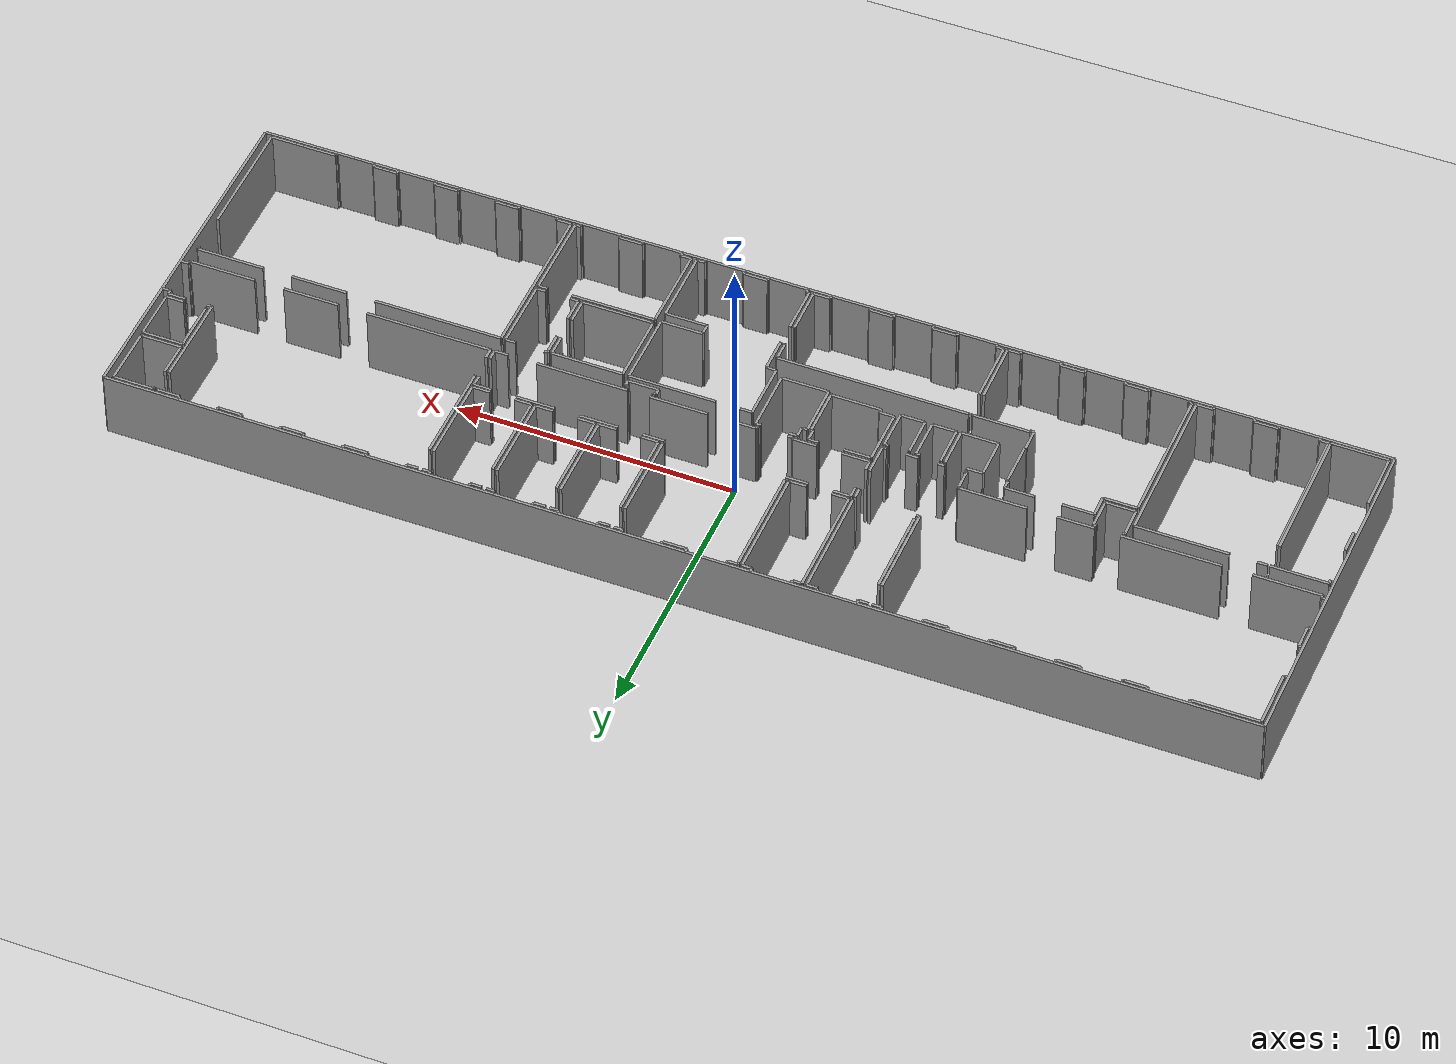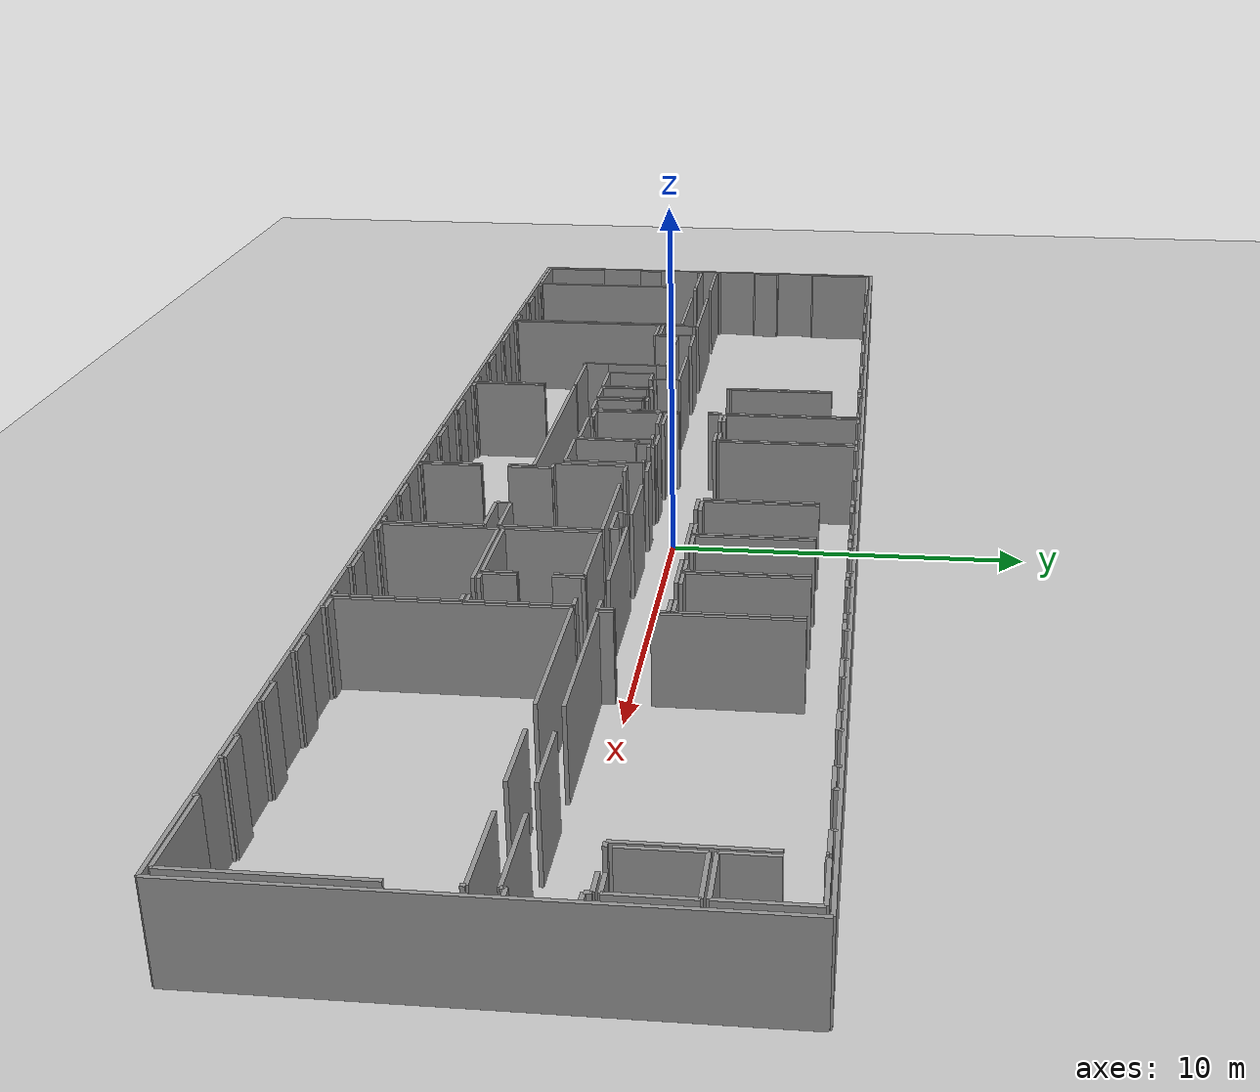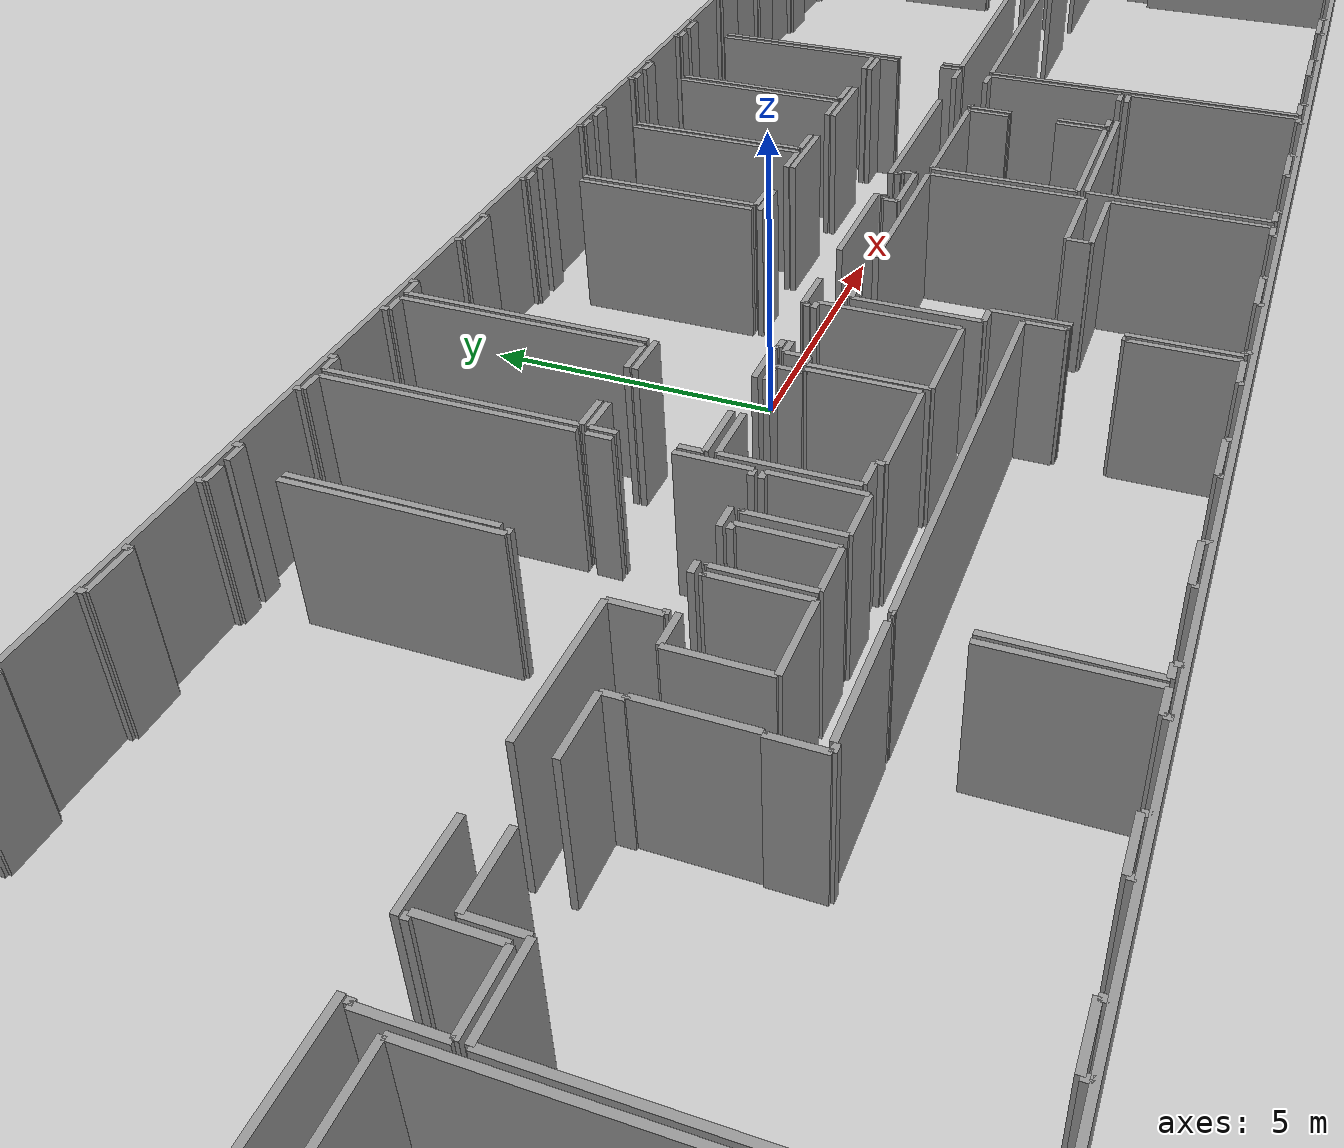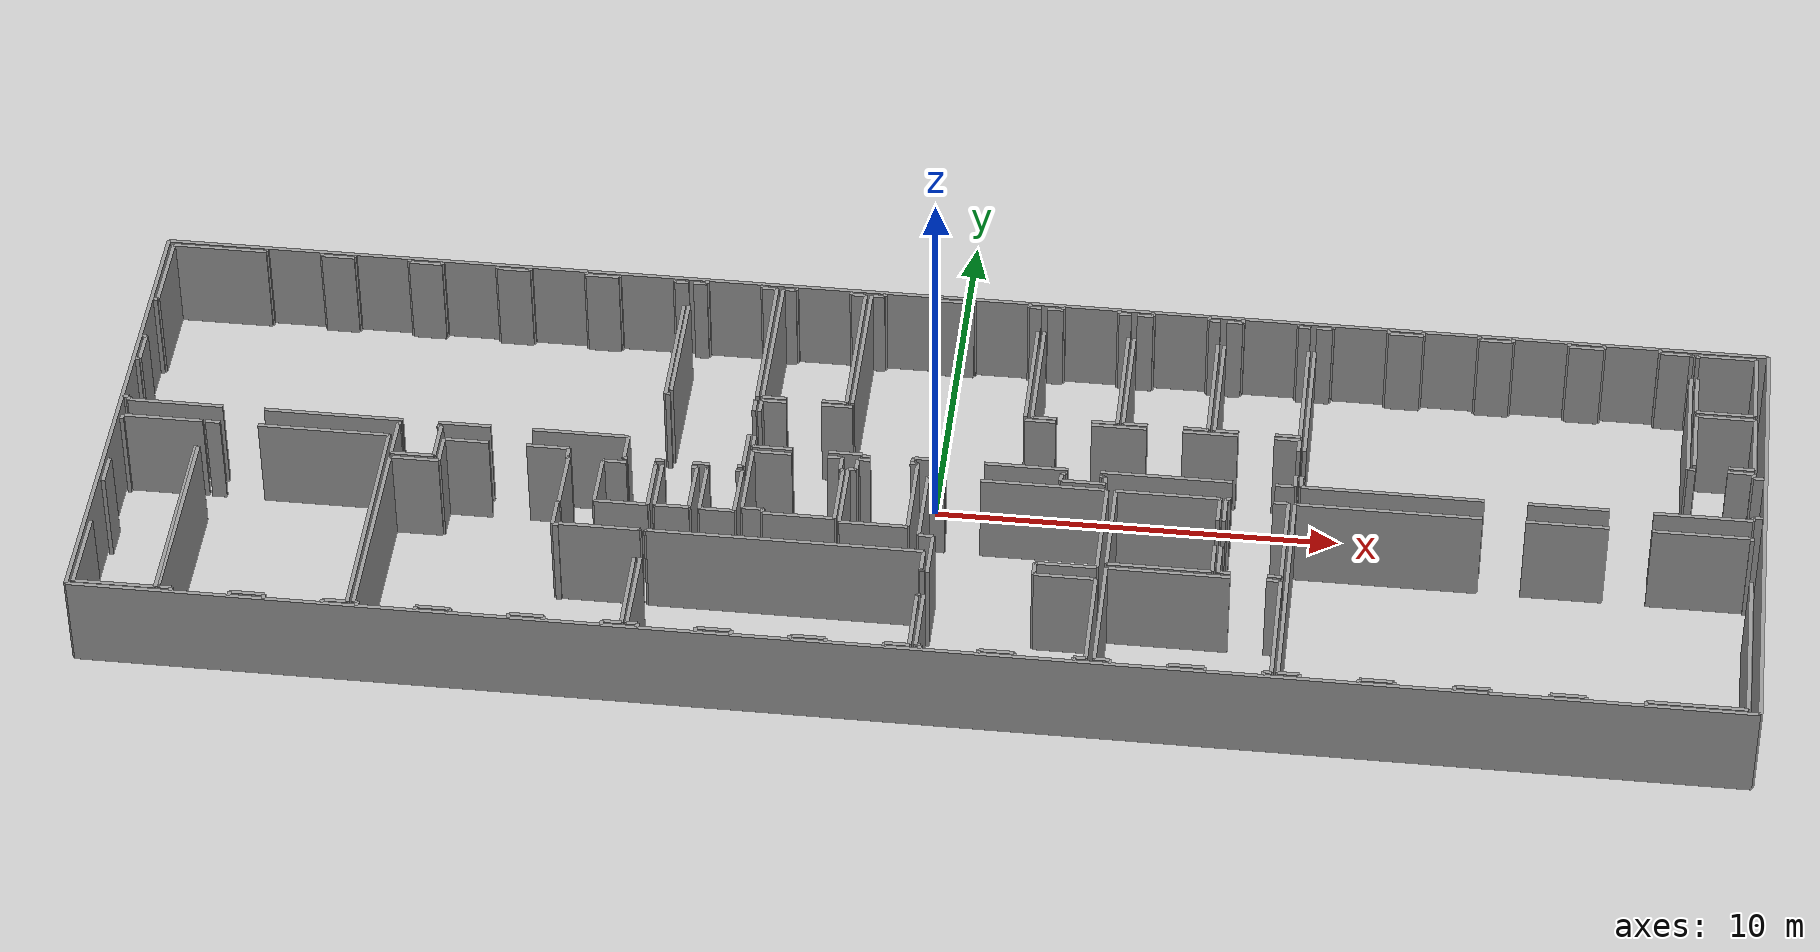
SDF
<sdf version="1.6">
  <world name="default">
    <light name="sun" type="directional">
      <cast_shadows>1</cast_shadows>
      <pose frame="">0 0 10 0 -0 0</pose>
      <diffuse>0.8 0.8 0.8 1</diffuse>
      <specular>0.1 0.1 0.1 1</specular>
      <attenuation>
        <range>1000</range>
        <constant>0.9</constant>
        <linear>0.01</linear>
        <quadratic>0.001</quadratic>
      </attenuation>
      <direction>-0.5 0.5 -1</direction>
    </light>
    <model name="ground_plane">
      <static>1</static>
      <link name="link">
        <collision name="collision">
          <geometry>
            <plane>
              <normal>0 0 1</normal>
              <size>100 100</size>
            </plane>
          </geometry>
          <surface>
            <friction>
              <ode>
                <mu>100</mu>
                <mu2>50</mu2>
              </ode>
              <torsional>
                <ode />
              </torsional>
            </friction>
            <contact>
              <ode />
            </contact>
            <bounce />
          </surface>
          <max_contacts>10</max_contacts>
        </collision>
        <visual name="visual">
          <cast_shadows>0</cast_shadows>
          <geometry>
            <plane>
              <normal>0 0 1</normal>
              <size>100 100</size>
            </plane>
          </geometry>
          <material>
            <script>
              <uri>file://media/materials/scripts/gazebo.material</uri>
              <name>Gazebo/Grey</name>
            </script>
          </material>
        </visual>
        <self_collide>0</self_collide>
        <kinematic>0</kinematic>
        <gravity>1</gravity>
      </link>
    </model>
    <gravity>0 0 -9.8</gravity>
    <magnetic_field>6e-06 2.3e-05 -4.2e-05</magnetic_field>
    <atmosphere type="adiabatic" />
    <physics default="0" name="default_physics" type="ode">
      <max_step_size>0.001</max_step_size>
      <real_time_factor>1</real_time_factor>
      <real_time_update_rate>1000</real_time_update_rate>
    </physics>
    <scene>
      <ambient>0.4 0.4 0.4 1</ambient>
      <background>0.7 0.7 0.7 1</background>
      <shadows>1</shadows>
    </scene>
    <spherical_coordinates>
      <surface_model>EARTH_WGS84</surface_model>
      <latitude_deg>0</latitude_deg>
      <longitude_deg>0</longitude_deg>
      <elevation>0</elevation>
      <heading_deg>0</heading_deg>
    </spherical_coordinates>
  <model name="0510025537_Layout1_PLAN3">
		<static>1</static>
		<link name="Wall_0">
			<collision name="Wall_0_Collision">
				<geometry>
					<box>
						<size>1.1547944335 0.1 2.5</size>
					</box>
				</geometry>
				<pose frame="">0.57739721675 0 1.25 0 0 0</pose>
			</collision>
			<visual name="Wall_0_Visual">
				<pose frame="">0.57739721675 0 1.25 0 0 0</pose>
				<geometry>
					<box>
						<size>1.1547944335 0.1 2.5</size>
					</box>
				</geometry>
				<material>
					<script>
						<uri>file://media/materials/scripts/gazebo.material</uri>
						<name>Gazebo/Grey</name>
					</script>
					<ambient>1 1 1 1</ambient>
				</material>
			</visual>
			<pose frame="">15.6459109106 -5.61763995679 0 0 0 -1.57079632679</pose>
		</link>
		<link name="Wall_1">
			<collision name="Wall_1_Collision">
				<geometry>
					<box>
						<size>0.140115651014 0.1 2.5</size>
					</box>
				</geometry>
				<pose frame="">0.0700578255068 0 1.25 0 0 0</pose>
			</collision>
			<visual name="Wall_1_Visual">
				<pose frame="">0.0700578255068 0 1.25 0 0 0</pose>
				<geometry>
					<box>
						<size>0.140115651014 0.1 2.5</size>
					</box>
				</geometry>
				<material>
					<script>
						<uri>file://media/materials/scripts/gazebo.material</uri>
						<name>Gazebo/Grey</name>
					</script>
					<ambient>1 1 1 1</ambient>
				</material>
			</visual>
			<pose frame="">15.6459109106 -6.77243439029 0 0 0 3.14159265359</pose>
		</link>
		<link name="Wall_2">
			<collision name="Wall_2_Collision">
				<geometry>
					<box>
						<size>0.414818580416 0.1 2.5</size>
					</box>
				</geometry>
				<pose frame="">0.207409290208 0 1.25 0 0 0</pose>
			</collision>
			<visual name="Wall_2_Visual">
				<pose frame="">0.207409290208 0 1.25 0 0 0</pose>
				<geometry>
					<box>
						<size>0.414818580416 0.1 2.5</size>
					</box>
				</geometry>
				<material>
					<script>
						<uri>file://media/materials/scripts/gazebo.material</uri>
						<name>Gazebo/Grey</name>
					</script>
					<ambient>1 1 1 1</ambient>
				</material>
			</visual>
			<pose frame="">14.8190061638 -6.77243439029 0 0 0 3.14159265359</pose>
		</link>
		<link name="Wall_3">
			<collision name="Wall_3_Collision">
				<geometry>
					<box>
						<size>0.239816991803 0.1 2.5</size>
					</box>
				</geometry>
				<pose frame="">0.119908495901 0 1.25 0 0 0</pose>
			</collision>
			<visual name="Wall_3_Visual">
				<pose frame="">0.119908495901 0 1.25 0 0 0</pose>
				<geometry>
					<box>
						<size>0.239816991803 0.1 2.5</size>
					</box>
				</geometry>
				<material>
					<script>
						<uri>file://media/materials/scripts/gazebo.material</uri>
						<name>Gazebo/Grey</name>
					</script>
					<ambient>1 1 1 1</ambient>
				</material>
			</visual>
			<pose frame="">13.711615937 -6.77243439029 0 0 0 3.14159265359</pose>
		</link>
		<link name="Wall_4">
			<collision name="Wall_4_Collision">
				<geometry>
					<box>
						<size>0.0835610345047 0.1 2.5</size>
					</box>
				</geometry>
				<pose frame="">0.0417805172523 0 1.25 0 0 0</pose>
			</collision>
			<visual name="Wall_4_Visual">
				<pose frame="">0.0417805172523 0 1.25 0 0 0</pose>
				<geometry>
					<box>
						<size>0.0835610345047 0.1 2.5</size>
					</box>
				</geometry>
				<material>
					<script>
						<uri>file://media/materials/scripts/gazebo.material</uri>
						<name>Gazebo/Grey</name>
					</script>
					<ambient>1 1 1 1</ambient>
				</material>
			</visual>
			<pose frame="">12.7811336341 -6.77243439029 0 0 0 3.14159265359</pose>
		</link>
		<link name="Wall_5">
			<collision name="Wall_5_Collision">
				<geometry>
					<box>
						<size>0.762089343585 0.1 2.5</size>
					</box>
				</geometry>
				<pose frame="">0.381044671793 0 1.25 0 0 0</pose>
			</collision>
			<visual name="Wall_5_Visual">
				<pose frame="">0.381044671793 0 1.25 0 0 0</pose>
				<geometry>
					<box>
						<size>0.762089343585 0.1 2.5</size>
					</box>
				</geometry>
				<material>
					<script>
						<uri>file://media/materials/scripts/gazebo.material</uri>
						<name>Gazebo/Grey</name>
					</script>
					<ambient>1 1 1 1</ambient>
				</material>
			</visual>
			<pose frame="">12.6975725996 -6.77243439029 0 0 0 1.57079632679</pose>
		</link>
		<link name="Wall_6">
			<collision name="Wall_6_Collision">
				<geometry>
					<box>
						<size>2.39295926797 0.1 2.5</size>
					</box>
				</geometry>
				<pose frame="">1.19647963398 0 1.25 0 0 0</pose>
			</collision>
			<visual name="Wall_6_Visual">
				<pose frame="">1.19647963398 0 1.25 0 0 0</pose>
				<geometry>
					<box>
						<size>2.39295926797 0.1 2.5</size>
					</box>
				</geometry>
				<material>
					<script>
						<uri>file://media/materials/scripts/gazebo.material</uri>
						<name>Gazebo/Grey</name>
					</script>
					<ambient>1 1 1 1</ambient>
				</material>
			</visual>
			<pose frame="">12.6975725996 -6.01034504671 0 0 0 3.14159265359</pose>
		</link>
		<link name="Wall_7">
			<collision name="Wall_7_Collision">
				<geometry>
					<box>
						<size>1.30406049438 0.1 2.5</size>
					</box>
				</geometry>
				<pose frame="">0.652030247188 0 1.25 0 0 0</pose>
			</collision>
			<visual name="Wall_7_Visual">
				<pose frame="">0.652030247188 0 1.25 0 0 0</pose>
				<geometry>
					<box>
						<size>1.30406049438 0.1 2.5</size>
					</box>
				</geometry>
				<material>
					<script>
						<uri>file://media/materials/scripts/gazebo.material</uri>
						<name>Gazebo/Grey</name>
					</script>
					<ambient>1 1 1 1</ambient>
				</material>
			</visual>
			<pose frame="">9.2715066404 -6.01034504671 0 0 0 3.14159265359</pose>
		</link>
		<link name="Wall_8">
			<collision name="Wall_8_Collision">
				<geometry>
					<box>
						<size>3.47868081591 0.1 2.5</size>
					</box>
				</geometry>
				<pose frame="">1.73934040796 0 1.25 0 0 0</pose>
			</collision>
			<visual name="Wall_8_Visual">
				<pose frame="">1.73934040796 0 1.25 0 0 0</pose>
				<geometry>
					<box>
						<size>3.47868081591 0.1 2.5</size>
					</box>
				</geometry>
				<material>
					<script>
						<uri>file://media/materials/scripts/gazebo.material</uri>
						<name>Gazebo/Grey</name>
					</script>
					<ambient>1 1 1 1</ambient>
				</material>
			</visual>
			<pose frame="">7.07617080765 -6.01034504671 0 0 0 3.14159265359</pose>
		</link>
		<link name="Wall_9">
			<collision name="Wall_9_Collision">
				<geometry>
					<box>
						<size>2.39026498062 0.1 2.5</size>
					</box>
				</geometry>
				<pose frame="">1.19513249031 0 1.25 0 0 0</pose>
			</collision>
			<visual name="Wall_9_Visual">
				<pose frame="">1.19513249031 0 1.25 0 0 0</pose>
				<geometry>
					<box>
						<size>2.39026498062 0.1 2.5</size>
					</box>
				</geometry>
				<material>
					<script>
						<uri>file://media/materials/scripts/gazebo.material</uri>
						<name>Gazebo/Grey</name>
					</script>
					<ambient>1 1 1 1</ambient>
				</material>
			</visual>
			<pose frame="">2.55739340408 -6.01034504671 0 0 0 3.14159265359</pose>
		</link>
		<link name="Wall_10">
			<collision name="Wall_10_Collision">
				<geometry>
					<box>
						<size>0.112410243375 0.1 2.5</size>
					</box>
				</geometry>
				<pose frame="">0.0562051216877 0 1.25 0 0 0</pose>
			</collision>
			<visual name="Wall_10_Visual">
				<pose frame="">0.0562051216877 0 1.25 0 0 0</pose>
				<geometry>
					<box>
						<size>0.112410243375 0.1 2.5</size>
					</box>
				</geometry>
				<material>
					<script>
						<uri>file://media/materials/scripts/gazebo.material</uri>
						<name>Gazebo/Grey</name>
					</script>
					<ambient>1 1 1 1</ambient>
				</material>
			</visual>
			<pose frame="">0.167128423461 -6.01034504671 0 0 0 1.57079632679</pose>
		</link>
		<link name="Wall_11">
			<collision name="Wall_11_Collision">
				<geometry>
					<box>
						<size>0.167128423461 0.1 2.5</size>
					</box>
				</geometry>
				<pose frame="">0.0835642117303 0 1.25 0 0 0</pose>
			</collision>
			<visual name="Wall_11_Visual">
				<pose frame="">0.0835642117303 0 1.25 0 0 0</pose>
				<geometry>
					<box>
						<size>0.167128423461 0.1 2.5</size>
					</box>
				</geometry>
				<material>
					<script>
						<uri>file://media/materials/scripts/gazebo.material</uri>
						<name>Gazebo/Grey</name>
					</script>
					<ambient>1 1 1 1</ambient>
				</material>
			</visual>
			<pose frame="">0.167128423461 -5.89793480333 0 0 0 3.14159265359</pose>
		</link>
		<link name="Wall_12">
			<collision name="Wall_12_Collision">
				<geometry>
					<box>
						<size>0.150594141196 0.1 2.5</size>
					</box>
				</geometry>
				<pose frame="">0.075297070598 0 1.25 0 0 0</pose>
			</collision>
			<visual name="Wall_12_Visual">
				<pose frame="">0.075297070598 0 1.25 0 0 0</pose>
				<geometry>
					<box>
						<size>0.150594141196 0.1 2.5</size>
					</box>
				</geometry>
				<material>
					<script>
						<uri>file://media/materials/scripts/gazebo.material</uri>
						<name>Gazebo/Grey</name>
					</script>
					<ambient>1 1 1 1</ambient>
				</material>
			</visual>
			<pose frame="">0.0 -4.49785854991 0 0 0 0.0</pose>
		</link>
		<link name="Wall_13">
			<collision name="Wall_13_Collision">
				<geometry>
					<box>
						<size>0.852322551948 0.1 2.5</size>
					</box>
				</geometry>
				<pose frame="">0.426161275974 0 1.25 0 0 0</pose>
			</collision>
			<visual name="Wall_13_Visual">
				<pose frame="">0.426161275974 0 1.25 0 0 0</pose>
				<geometry>
					<box>
						<size>0.852322551948 0.1 2.5</size>
					</box>
				</geometry>
				<material>
					<script>
						<uri>file://media/materials/scripts/gazebo.material</uri>
						<name>Gazebo/Grey</name>
					</script>
					<ambient>1 1 1 1</ambient>
				</material>
			</visual>
			<pose frame="">0.150594141196 -4.49785854991 0 0 0 1.57079632679</pose>
		</link>
		<link name="Wall_14">
			<collision name="Wall_14_Collision">
				<geometry>
					<box>
						<size>0.148382792146 0.1 2.5</size>
					</box>
				</geometry>
				<pose frame="">0.0741913960729 0 1.25 0 0 0</pose>
			</collision>
			<visual name="Wall_14_Visual">
				<pose frame="">0.0741913960729 0 1.25 0 0 0</pose>
				<geometry>
					<box>
						<size>0.148382792146 0.1 2.5</size>
					</box>
				</geometry>
				<material>
					<script>
						<uri>file://media/materials/scripts/gazebo.material</uri>
						<name>Gazebo/Grey</name>
					</script>
					<ambient>1 1 1 1</ambient>
				</material>
			</visual>
			<pose frame="">0.150594141196 -3.64553599797 0 0 0 3.14159265359</pose>
		</link>
		<link name="Wall_15">
			<collision name="Wall_15_Collision">
				<geometry>
					<box>
						<size>0.154807142403 0.1 2.5</size>
					</box>
				</geometry>
				<pose frame="">0.0774035712016 0 1.25 0 0 0</pose>
			</collision>
			<visual name="Wall_15_Visual">
				<pose frame="">0.0774035712016 0 1.25 0 0 0</pose>
				<geometry>
					<box>
						<size>0.154807142403 0.1 2.5</size>
					</box>
				</geometry>
				<material>
					<script>
						<uri>file://media/materials/scripts/gazebo.material</uri>
						<name>Gazebo/Grey</name>
					</script>
					<ambient>1 1 1 1</ambient>
				</material>
			</visual>
			<pose frame="">0.00221134905001 -2.23677320963 0 0 0 0.0</pose>
		</link>
		<link name="Wall_16">
			<collision name="Wall_16_Collision">
				<geometry>
					<box>
						<size>2.09745186503 0.1 2.5</size>
					</box>
				</geometry>
				<pose frame="">1.04872593252 0 1.25 0 0 0</pose>
			</collision>
			<visual name="Wall_16_Visual">
				<pose frame="">1.04872593252 0 1.25 0 0 0</pose>
				<geometry>
					<box>
						<size>2.09745186503 0.1 2.5</size>
					</box>
				</geometry>
				<material>
					<script>
						<uri>file://media/materials/scripts/gazebo.material</uri>
						<name>Gazebo/Grey</name>
					</script>
					<ambient>1 1 1 1</ambient>
				</material>
			</visual>
			<pose frame="">0.157018491453 -2.23677320963 0 0 0 1.57079632679</pose>
		</link>
		<link name="Wall_17">
			<collision name="Wall_17_Collision">
				<geometry>
					<box>
						<size>2.38982652348 0.1 2.5</size>
					</box>
				</geometry>
				<pose frame="">1.19491326174 0 1.25 0 0 0</pose>
			</collision>
			<visual name="Wall_17_Visual">
				<pose frame="">1.19491326174 0 1.25 0 0 0</pose>
				<geometry>
					<box>
						<size>2.38982652348 0.1 2.5</size>
					</box>
				</geometry>
				<material>
					<script>
						<uri>file://media/materials/scripts/gazebo.material</uri>
						<name>Gazebo/Grey</name>
					</script>
					<ambient>1 1 1 1</ambient>
				</material>
			</visual>
			<pose frame="">0.157018491453 -0.139321344602 0 0 0 0.0</pose>
		</link>
		<link name="Wall_18">
			<collision name="Wall_18_Collision">
				<geometry>
					<box>
						<size>0.130793670967 0.1 2.5</size>
					</box>
				</geometry>
				<pose frame="">0.0653968354833 0 1.25 0 0 0</pose>
			</collision>
			<visual name="Wall_18_Visual">
				<pose frame="">0.0653968354833 0 1.25 0 0 0</pose>
				<geometry>
					<box>
						<size>0.130793670967 0.1 2.5</size>
					</box>
				</geometry>
				<material>
					<script>
						<uri>file://media/materials/scripts/gazebo.material</uri>
						<name>Gazebo/Grey</name>
					</script>
					<ambient>1 1 1 1</ambient>
				</material>
			</visual>
			<pose frame="">2.54684501493 -0.139321344602 0 0 0 1.57079632679</pose>
		</link>
		<link name="Wall_19">
			<collision name="Wall_19_Collision">
				<geometry>
					<box>
						<size>0.127158924827 0.1 2.5</size>
					</box>
				</geometry>
				<pose frame="">0.0635794624134 0 1.25 0 0 0</pose>
			</collision>
			<visual name="Wall_19_Visual">
				<pose frame="">0.0635794624134 0 1.25 0 0 0</pose>
				<geometry>
					<box>
						<size>0.127158924827 0.1 2.5</size>
					</box>
				</geometry>
				<material>
					<script>
						<uri>file://media/materials/scripts/gazebo.material</uri>
						<name>Gazebo/Grey</name>
					</script>
					<ambient>1 1 1 1</ambient>
				</material>
			</visual>
			<pose frame="">3.9746902205 -0.00852767363538 0 0 0 -1.57079632679</pose>
		</link>
		<link name="Wall_20">
			<collision name="Wall_20_Collision">
				<geometry>
					<box>
						<size>0.839295926797 0.1 2.5</size>
					</box>
				</geometry>
				<pose frame="">0.419647963398 0 1.25 0 0 0</pose>
			</collision>
			<visual name="Wall_20_Visual">
				<pose frame="">0.419647963398 0 1.25 0 0 0</pose>
				<geometry>
					<box>
						<size>0.839295926797 0.1 2.5</size>
					</box>
				</geometry>
				<material>
					<script>
						<uri>file://media/materials/scripts/gazebo.material</uri>
						<name>Gazebo/Grey</name>
					</script>
					<ambient>1 1 1 1</ambient>
				</material>
			</visual>
			<pose frame="">3.9746902205 -0.135686598462 0 0 0 0.0</pose>
		</link>
		<link name="Wall_21">
			<collision name="Wall_21_Collision">
				<geometry>
					<box>
						<size>0.134422062655 0.1 2.5</size>
					</box>
				</geometry>
				<pose frame="">0.0672110313274 0 1.25 0 0 0</pose>
			</collision>
			<visual name="Wall_21_Visual">
				<pose frame="">0.0672110313274 0 1.25 0 0 0</pose>
				<geometry>
					<box>
						<size>0.134422062655 0.1 2.5</size>
					</box>
				</geometry>
				<material>
					<script>
						<uri>file://media/materials/scripts/gazebo.material</uri>
						<name>Gazebo/Grey</name>
					</script>
					<ambient>1 1 1 1</ambient>
				</material>
			</visual>
			<pose frame="">4.8139861473 -0.135686598462 0 0 0 1.57079632679</pose>
		</link>
		<link name="Wall_22">
			<collision name="Wall_22_Collision">
				<geometry>
					<box>
						<size>0.138056808795 0.1 2.5</size>
					</box>
				</geometry>
				<pose frame="">0.0690284043973 0 1.25 0 0 0</pose>
			</collision>
			<visual name="Wall_22_Visual">
				<pose frame="">0.0690284043973 0 1.25 0 0 0</pose>
				<geometry>
					<box>
						<size>0.138056808795 0.1 2.5</size>
					</box>
				</geometry>
				<material>
					<script>
						<uri>file://media/materials/scripts/gazebo.material</uri>
						<name>Gazebo/Grey</name>
					</script>
					<ambient>1 1 1 1</ambient>
				</material>
			</visual>
			<pose frame="">6.2272796594 -0.00126453580733 0 0 0 -1.57079632679</pose>
		</link>
		<link name="Wall_23">
			<collision name="Wall_23_Collision">
				<geometry>
					<box>
						<size>0.842854419521 0.1 2.5</size>
					</box>
				</geometry>
				<pose frame="">0.42142720976 0 1.25 0 0 0</pose>
			</collision>
			<visual name="Wall_23_Visual">
				<pose frame="">0.42142720976 0 1.25 0 0 0</pose>
				<geometry>
					<box>
						<size>0.842854419521 0.1 2.5</size>
					</box>
				</geometry>
				<material>
					<script>
						<uri>file://media/materials/scripts/gazebo.material</uri>
						<name>Gazebo/Grey</name>
					</script>
					<ambient>1 1 1 1</ambient>
				</material>
			</visual>
			<pose frame="">6.2272796594 -0.139321344602 0 0 0 0.0</pose>
		</link>
		<link name="Wall_24">
			<collision name="Wall_24_Collision">
				<geometry>
					<box>
						<size>0.127158924827 0.1 2.5</size>
					</box>
				</geometry>
				<pose frame="">0.0635794624134 0 1.25 0 0 0</pose>
			</collision>
			<visual name="Wall_24_Visual">
				<pose frame="">0.0635794624134 0 1.25 0 0 0</pose>
				<geometry>
					<box>
						<size>0.127158924827 0.1 2.5</size>
					</box>
				</geometry>
				<material>
					<script>
						<uri>file://media/materials/scripts/gazebo.material</uri>
						<name>Gazebo/Grey</name>
					</script>
					<ambient>1 1 1 1</ambient>
				</material>
			</visual>
			<pose frame="">7.07013407892 -0.139321344602 0 0 0 1.57079632679</pose>
		</link>
		<link name="Wall_25">
			<collision name="Wall_25_Collision">
				<geometry>
					<box>
						<size>0.12299675923 0.1 2.5</size>
					</box>
				</geometry>
				<pose frame="">0.0614983796149 0 1.25 0 0 0</pose>
			</collision>
			<visual name="Wall_25_Visual">
				<pose frame="">0.0614983796149 0 1.25 0 0 0</pose>
				<geometry>
					<box>
						<size>0.12299675923 0.1 2.5</size>
					</box>
				</geometry>
				<material>
					<script>
						<uri>file://media/materials/scripts/gazebo.material</uri>
						<name>Gazebo/Grey</name>
					</script>
					<ambient>1 1 1 1</ambient>
				</material>
			</visual>
			<pose frame="">8.48393594713 -0.0121624197751 0 0 0 -1.57079632679</pose>
		</link>
		<link name="Wall_26">
			<collision name="Wall_26_Collision">
				<geometry>
					<box>
						<size>0.848891148249 0.1 2.5</size>
					</box>
				</geometry>
				<pose frame="">0.424445574125 0 1.25 0 0 0</pose>
			</collision>
			<visual name="Wall_26_Visual">
				<pose frame="">0.424445574125 0 1.25 0 0 0</pose>
				<geometry>
					<box>
						<size>0.848891148249 0.1 2.5</size>
					</box>
				</geometry>
				<material>
					<script>
						<uri>file://media/materials/scripts/gazebo.material</uri>
						<name>Gazebo/Grey</name>
					</script>
					<ambient>1 1 1 1</ambient>
				</material>
			</visual>
			<pose frame="">8.48393594713 -0.135159179005 0 0 0 0.0</pose>
		</link>
		<link name="Wall_27">
			<collision name="Wall_27_Collision">
				<geometry>
					<box>
						<size>0.123625849908 0.1 2.5</size>
					</box>
				</geometry>
				<pose frame="">0.0618129249539 0 1.25 0 0 0</pose>
			</collision>
			<visual name="Wall_27_Visual">
				<pose frame="">0.0618129249539 0 1.25 0 0 0</pose>
				<geometry>
					<box>
						<size>0.123625849908 0.1 2.5</size>
					</box>
				</geometry>
				<material>
					<script>
						<uri>file://media/materials/scripts/gazebo.material</uri>
						<name>Gazebo/Grey</name>
					</script>
					<ambient>1 1 1 1</ambient>
				</material>
			</visual>
			<pose frame="">9.33282709538 -0.135159179005 0 0 0 1.57079632679</pose>
		</link>
		<link name="Wall_28">
			<collision name="Wall_28_Collision">
				<geometry>
					<box>
						<size>0.123625849908 0.1 2.5</size>
					</box>
				</geometry>
				<pose frame="">0.0618129249539 0 1.25 0 0 0</pose>
			</collision>
			<visual name="Wall_28_Visual">
				<pose frame="">0.0618129249539 0 1.25 0 0 0</pose>
				<geometry>
					<box>
						<size>0.123625849908 0.1 2.5</size>
					</box>
				</geometry>
				<material>
					<script>
						<uri>file://media/materials/scripts/gazebo.material</uri>
						<name>Gazebo/Grey</name>
					</script>
					<ambient>1 1 1 1</ambient>
				</material>
			</visual>
			<pose frame="">10.7586388765 -0.011533329097 0 0 0 -1.57079632679</pose>
		</link>
		<link name="Wall_29">
			<collision name="Wall_29_Collision">
				<geometry>
					<box>
						<size>0.840630361568 0.1 2.5</size>
					</box>
				</geometry>
				<pose frame="">0.420315180784 0 1.25 0 0 0</pose>
			</collision>
			<visual name="Wall_29_Visual">
				<pose frame="">0.420315180784 0 1.25 0 0 0</pose>
				<geometry>
					<box>
						<size>0.840630361568 0.1 2.5</size>
					</box>
				</geometry>
				<material>
					<script>
						<uri>file://media/materials/scripts/gazebo.material</uri>
						<name>Gazebo/Grey</name>
					</script>
					<ambient>1 1 1 1</ambient>
				</material>
			</visual>
			<pose frame="">10.7586388765 -0.135159179005 0 0 0 0.0</pose>
		</link>
		<link name="Wall_30">
			<collision name="Wall_30_Collision">
				<geometry>
					<box>
						<size>0.123625849908 0.1 2.5</size>
					</box>
				</geometry>
				<pose frame="">0.0618129249539 0 1.25 0 0 0</pose>
			</collision>
			<visual name="Wall_30_Visual">
				<pose frame="">0.0618129249539 0 1.25 0 0 0</pose>
				<geometry>
					<box>
						<size>0.123625849908 0.1 2.5</size>
					</box>
				</geometry>
				<material>
					<script>
						<uri>file://media/materials/scripts/gazebo.material</uri>
						<name>Gazebo/Grey</name>
					</script>
					<ambient>1 1 1 1</ambient>
				</material>
			</visual>
			<pose frame="">11.5992692381 -0.135159179005 0 0 0 1.57079632679</pose>
		</link>
		<link name="Wall_31">
			<collision name="Wall_31_Collision">
				<geometry>
					<box>
						<size>0.134993963271 0.1 2.5</size>
					</box>
				</geometry>
				<pose frame="">0.0674969816356 0 1.25 0 0 0</pose>
			</collision>
			<visual name="Wall_31_Visual">
				<pose frame="">0.0674969816356 0 1.25 0 0 0</pose>
				<geometry>
					<box>
						<size>0.134993963271 0.1 2.5</size>
					</box>
				</geometry>
				<material>
					<script>
						<uri>file://media/materials/scripts/gazebo.material</uri>
						<name>Gazebo/Grey</name>
					</script>
					<ambient>1 1 1 1</ambient>
				</material>
			</visual>
			<pose frame="">13.0320709157 -0.011533329097 0 0 0 -1.57079632679</pose>
		</link>
		<link name="Wall_32">
			<collision name="Wall_32_Collision">
				<geometry>
					<box>
						<size>0.355531549851 0.1 2.5</size>
					</box>
				</geometry>
				<pose frame="">0.177765774925 0 1.25 0 0 0</pose>
			</collision>
			<visual name="Wall_32_Visual">
				<pose frame="">0.177765774925 0 1.25 0 0 0</pose>
				<geometry>
					<box>
						<size>0.355531549851 0.1 2.5</size>
					</box>
				</geometry>
				<material>
					<script>
						<uri>file://media/materials/scripts/gazebo.material</uri>
						<name>Gazebo/Grey</name>
					</script>
					<ambient>1 1 1 1</ambient>
				</material>
			</visual>
			<pose frame="">13.0320709157 -0.146527292368 0 0 0 0.0</pose>
		</link>
		<link name="Wall_33">
			<collision name="Wall_33_Collision">
				<geometry>
					<box>
						<size>3.32291415136 0.1 2.5</size>
					</box>
				</geometry>
				<pose frame="">1.66145707568 0 1.25 0 0 0</pose>
			</collision>
			<visual name="Wall_33_Visual">
				<pose frame="">1.66145707568 0 1.25 0 0 0</pose>
				<geometry>
					<box>
						<size>3.32291415136 0.1 2.5</size>
					</box>
				</geometry>
				<material>
					<script>
						<uri>file://media/materials/scripts/gazebo.material</uri>
						<name>Gazebo/Grey</name>
					</script>
					<ambient>1 1 1 1</ambient>
				</material>
			</visual>
			<pose frame="">13.3876024655 -1.01621020525 0 0 0 -1.57079632679</pose>
		</link>
		<link name="Wall_34">
			<collision name="Wall_34_Collision">
				<geometry>
					<box>
						<size>0.116350003177 0.1 2.5</size>
					</box>
				</geometry>
				<pose frame="">0.0581750015886 0 1.25 0 0 0</pose>
			</collision>
			<visual name="Wall_34_Visual">
				<pose frame="">0.0581750015886 0 1.25 0 0 0</pose>
				<geometry>
					<box>
						<size>0.116350003177 0.1 2.5</size>
					</box>
				</geometry>
				<material>
					<script>
						<uri>file://media/materials/scripts/gazebo.material</uri>
						<name>Gazebo/Grey</name>
					</script>
					<ambient>1 1 1 1</ambient>
				</material>
			</visual>
			<pose frame="">13.3876024655 -4.33912435661 0 0 0 0.0</pose>
		</link>
		<link name="Wall_35">
			<collision name="Wall_35_Collision">
				<geometry>
					<box>
						<size>0.400839109927 0.1 2.5</size>
					</box>
				</geometry>
				<pose frame="">0.200419554964 0 1.25 0 0 0</pose>
			</collision>
			<visual name="Wall_35_Visual">
				<pose frame="">0.200419554964 0 1.25 0 0 0</pose>
				<geometry>
					<box>
						<size>0.400839109927 0.1 2.5</size>
					</box>
				</geometry>
				<material>
					<script>
						<uri>file://media/materials/scripts/gazebo.material</uri>
						<name>Gazebo/Grey</name>
					</script>
					<ambient>1 1 1 1</ambient>
				</material>
			</visual>
			<pose frame="">15.6464192667 -4.33912435661 0 0 0 -1.57206455693</pose>
		</link>
		<link name="Wall_36">
			<collision name="Wall_36_Collision">
				<geometry>
					<box>
						<size>3.1744678147 0.1 2.5</size>
					</box>
				</geometry>
				<pose frame="">1.58723390735 0 1.25 0 0 0</pose>
			</collision>
			<visual name="Wall_36_Visual">
				<pose frame="">1.58723390735 0 1.25 0 0 0</pose>
				<geometry>
					<box>
						<size>3.1744678147 0.1 2.5</size>
					</box>
				</geometry>
				<material>
					<script>
						<uri>file://media/materials/scripts/gazebo.material</uri>
						<name>Gazebo/Grey</name>
					</script>
					<ambient>1 1 1 1</ambient>
				</material>
			</visual>
			<pose frame="">13.5077651395 -4.20123276355 0 0 0 1.57079632679</pose>
		</link>
		<link name="Wall_37">
			<collision name="Wall_37_Collision">
				<geometry>
					<box>
						<size>0.345936328398 0.1 2.5</size>
					</box>
				</geometry>
				<pose frame="">0.172968164199 0 1.25 0 0 0</pose>
			</collision>
			<visual name="Wall_37_Visual">
				<pose frame="">0.172968164199 0 1.25 0 0 0</pose>
				<geometry>
					<box>
						<size>0.345936328398 0.1 2.5</size>
					</box>
				</geometry>
				<material>
					<script>
						<uri>file://media/materials/scripts/gazebo.material</uri>
						<name>Gazebo/Grey</name>
					</script>
					<ambient>1 1 1 1</ambient>
				</material>
			</visual>
			<pose frame="">13.5077651395 -0.141716972739 0 0 0 0.0</pose>
		</link>
		<link name="Wall_38">
			<collision name="Wall_38_Collision">
				<geometry>
					<box>
						<size>0.13842536697 0.1 2.5</size>
					</box>
				</geometry>
				<pose frame="">0.0692126834848 0 1.25 0 0 0</pose>
			</collision>
			<visual name="Wall_38_Visual">
				<pose frame="">0.0692126834848 0 1.25 0 0 0</pose>
				<geometry>
					<box>
						<size>0.13842536697 0.1 2.5</size>
					</box>
				</geometry>
				<material>
					<script>
						<uri>file://media/materials/scripts/gazebo.material</uri>
						<name>Gazebo/Grey</name>
					</script>
					<ambient>1 1 1 1</ambient>
				</material>
			</visual>
			<pose frame="">13.8537014679 -0.141716972739 0 0 0 1.57079632679</pose>
		</link>
		<link name="Wall_39">
			<collision name="Wall_39_Collision">
				<geometry>
					<box>
						<size>0.140109296562 0.1 2.5</size>
					</box>
				</geometry>
				<pose frame="">0.0700546482811 0 1.25 0 0 0</pose>
			</collision>
			<visual name="Wall_39_Visual">
				<pose frame="">0.0700546482811 0 1.25 0 0 0</pose>
				<geometry>
					<box>
						<size>0.140109296562 0.1 2.5</size>
					</box>
				</geometry>
				<material>
					<script>
						<uri>file://media/materials/scripts/gazebo.material</uri>
						<name>Gazebo/Grey</name>
					</script>
					<ambient>1 1 1 1</ambient>
				</material>
			</visual>
			<pose frame="">15.2668043464 -0.00329160576984 0 0 0 -1.57079632679</pose>
		</link>
		<link name="Wall_40">
			<collision name="Wall_40_Collision">
				<geometry>
					<box>
						<size>0.370845777467 0.1 2.5</size>
					</box>
				</geometry>
				<pose frame="">0.185422888734 0 1.25 0 0 0</pose>
			</collision>
			<visual name="Wall_40_Visual">
				<pose frame="">0.185422888734 0 1.25 0 0 0</pose>
				<geometry>
					<box>
						<size>0.370845777467 0.1 2.5</size>
					</box>
				</geometry>
				<material>
					<script>
						<uri>file://media/materials/scripts/gazebo.material</uri>
						<name>Gazebo/Grey</name>
					</script>
					<ambient>1 1 1 1</ambient>
				</material>
			</visual>
			<pose frame="">15.2668043464 -0.143400902332 0 0 0 0.0</pose>
		</link>
		<link name="Wall_41">
			<collision name="Wall_41_Collision">
				<geometry>
					<box>
						<size>4.05787059041 0.1 2.5</size>
					</box>
				</geometry>
				<pose frame="">2.0289352952 0 1.25 0 0 0</pose>
			</collision>
			<visual name="Wall_41_Visual">
				<pose frame="">2.0289352952 0 1.25 0 0 0</pose>
				<geometry>
					<box>
						<size>4.05787059041 0.1 2.5</size>
					</box>
				</geometry>
				<material>
					<script>
						<uri>file://media/materials/scripts/gazebo.material</uri>
						<name>Gazebo/Grey</name>
					</script>
					<ambient>1 1 1 1</ambient>
				</material>
			</visual>
			<pose frame="">15.6376501239 -0.143400902332 0 0 0 -1.56642729256</pose>
		</link>
		<link name="Wall_42">
			<collision name="Wall_42_Collision">
				<geometry>
					<box>
						<size>1.06545084832 0.1 2.5</size>
					</box>
				</geometry>
				<pose frame="">0.53272542416 0 1.25 0 0 0</pose>
			</collision>
			<visual name="Wall_42_Visual">
				<pose frame="">0.53272542416 0 1.25 0 0 0</pose>
				<geometry>
					<box>
						<size>1.06545084832 0.1 2.5</size>
					</box>
				</geometry>
				<material>
					<script>
						<uri>file://media/materials/scripts/gazebo.material</uri>
						<name>Gazebo/Grey</name>
					</script>
					<ambient>1 1 1 1</ambient>
				</material>
			</visual>
			<pose frame="">8.04732159878 -7.21368748809 0 0 0 3.14159265359</pose>
		</link>
		<link name="Wall_43">
			<collision name="Wall_43_Collision">
				<geometry>
					<box>
						<size>1.08413293512 0.1 2.5</size>
					</box>
				</geometry>
				<pose frame="">0.542066467561 0 1.25 0 0 0</pose>
			</collision>
			<visual name="Wall_43_Visual">
				<pose frame="">0.542066467561 0 1.25 0 0 0</pose>
				<geometry>
					<box>
						<size>1.08413293512 0.1 2.5</size>
					</box>
				</geometry>
				<material>
					<script>
						<uri>file://media/materials/scripts/gazebo.material</uri>
						<name>Gazebo/Grey</name>
					</script>
					<ambient>1 1 1 1</ambient>
				</material>
			</visual>
			<pose frame="">6.98187075046 -7.21368748809 0 0 0 1.57079632679</pose>
		</link>
		<link name="Wall_44">
			<collision name="Wall_44_Collision">
				<geometry>
					<box>
						<size>0.0789858295736 0.1 2.5</size>
					</box>
				</geometry>
				<pose frame="">0.0394929147868 0 1.25 0 0 0</pose>
			</collision>
			<visual name="Wall_44_Visual">
				<pose frame="">0.0394929147868 0 1.25 0 0 0</pose>
				<geometry>
					<box>
						<size>0.0789858295736 0.1 2.5</size>
					</box>
				</geometry>
				<material>
					<script>
						<uri>file://media/materials/scripts/gazebo.material</uri>
						<name>Gazebo/Grey</name>
					</script>
					<ambient>1 1 1 1</ambient>
				</material>
			</visual>
			<pose frame="">6.98187075046 -6.12955455296 0 0 0 0.0</pose>
		</link>
		<link name="Wall_45">
			<collision name="Wall_45_Collision">
				<geometry>
					<box>
						<size>0.1085975726 0.1 2.5</size>
					</box>
				</geometry>
				<pose frame="">0.0542987862998 0 1.25 0 0 0</pose>
			</collision>
			<visual name="Wall_45_Visual">
				<pose frame="">0.0542987862998 0 1.25 0 0 0</pose>
				<geometry>
					<box>
						<size>0.1085975726 0.1 2.5</size>
					</box>
				</geometry>
				<material>
					<script>
						<uri>file://media/materials/scripts/gazebo.material</uri>
						<name>Gazebo/Grey</name>
					</script>
					<ambient>1 1 1 1</ambient>
				</material>
			</visual>
			<pose frame="">7.94704835737 -6.12955455296 0 0 0 0.0</pose>
		</link>
		<link name="Wall_46">
			<collision name="Wall_46_Collision">
				<geometry>
					<box>
						<size>1.08416489313 0.1 2.5</size>
					</box>
				</geometry>
				<pose frame="">0.542082446567 0 1.25 0 0 0</pose>
			</collision>
			<visual name="Wall_46_Visual">
				<pose frame="">0.542082446567 0 1.25 0 0 0</pose>
				<geometry>
					<box>
						<size>1.08416489313 0.1 2.5</size>
					</box>
				</geometry>
				<material>
					<script>
						<uri>file://media/materials/scripts/gazebo.material</uri>
						<name>Gazebo/Grey</name>
					</script>
					<ambient>1 1 1 1</ambient>
				</material>
			</visual>
			<pose frame="">8.05564592997 -6.12955455296 0 0 0 -1.5784745066</pose>
		</link>
		<link name="Wall_47">
			<collision name="Wall_47_Collision">
				<geometry>
					<box>
						<size>2.01134905001 0.1 2.5</size>
					</box>
				</geometry>
				<pose frame="">1.005674525 0 1.25 0 0 0</pose>
			</collision>
			<visual name="Wall_47_Visual">
				<pose frame="">1.005674525 0 1.25 0 0 0</pose>
				<geometry>
					<box>
						<size>2.01134905001 0.1 2.5</size>
					</box>
				</geometry>
				<material>
					<script>
						<uri>file://media/materials/scripts/gazebo.material</uri>
						<name>Gazebo/Grey</name>
					</script>
					<ambient>1 1 1 1</ambient>
				</material>
			</visual>
			<pose frame="">2.16392578001 -12.5265171252 0 0 0 3.14159265359</pose>
		</link>
		<link name="Wall_48">
			<collision name="Wall_48_Collision">
				<geometry>
					<box>
						<size>2.10529325793 0.1 2.5</size>
					</box>
				</geometry>
				<pose frame="">1.05264662896 0 1.25 0 0 0</pose>
			</collision>
			<visual name="Wall_48_Visual">
				<pose frame="">1.05264662896 0 1.25 0 0 0</pose>
				<geometry>
					<box>
						<size>2.10529325793 0.1 2.5</size>
					</box>
				</geometry>
				<material>
					<script>
						<uri>file://media/materials/scripts/gazebo.material</uri>
						<name>Gazebo/Grey</name>
					</script>
					<ambient>1 1 1 1</ambient>
				</material>
			</visual>
			<pose frame="">0.152576729999 -12.5265171252 0 0 0 1.57079632679</pose>
		</link>
		<link name="Wall_49">
			<collision name="Wall_49_Collision">
				<geometry>
					<box>
						<size>0.820232572917 0.1 2.5</size>
					</box>
				</geometry>
				<pose frame="">0.410116286459 0 1.25 0 0 0</pose>
			</collision>
			<visual name="Wall_49_Visual">
				<pose frame="">0.410116286459 0 1.25 0 0 0</pose>
				<geometry>
					<box>
						<size>0.820232572917 0.1 2.5</size>
					</box>
				</geometry>
				<material>
					<script>
						<uri>file://media/materials/scripts/gazebo.material</uri>
						<name>Gazebo/Grey</name>
					</script>
					<ambient>1 1 1 1</ambient>
				</material>
			</visual>
			<pose frame="">0.152576729999 -8.99337866175 0 0 0 1.57079632679</pose>
		</link>
		<link name="Wall_50">
			<collision name="Wall_50_Collision">
				<geometry>
					<box>
						<size>0.150536951134 0.1 2.5</size>
					</box>
				</geometry>
				<pose frame="">0.0752684755671 0 1.25 0 0 0</pose>
			</collision>
			<visual name="Wall_50_Visual">
				<pose frame="">0.0752684755671 0 1.25 0 0 0</pose>
				<geometry>
					<box>
						<size>0.150536951134 0.1 2.5</size>
					</box>
				</geometry>
				<material>
					<script>
						<uri>file://media/materials/scripts/gazebo.material</uri>
						<name>Gazebo/Grey</name>
					</script>
					<ambient>1 1 1 1</ambient>
				</material>
			</visual>
			<pose frame="">0.152576729999 -6.73742136367 0 0 0 1.57079632679</pose>
		</link>
		<link name="Wall_51">
			<collision name="Wall_51_Collision">
				<geometry>
					<box>
						<size>2.0157336214 0.1 2.5</size>
					</box>
				</geometry>
				<pose frame="">1.0078668107 0 1.25 0 0 0</pose>
			</collision>
			<visual name="Wall_51_Visual">
				<pose frame="">1.0078668107 0 1.25 0 0 0</pose>
				<geometry>
					<box>
						<size>2.0157336214 0.1 2.5</size>
					</box>
				</geometry>
				<material>
					<script>
						<uri>file://media/materials/scripts/gazebo.material</uri>
						<name>Gazebo/Grey</name>
					</script>
					<ambient>1 1 1 1</ambient>
				</material>
			</visual>
			<pose frame="">0.152576729999 -6.58688441253 0 0 0 0.0</pose>
		</link>
		<link name="Wall_52">
			<collision name="Wall_52_Collision">
				<geometry>
					<box>
						<size>5.01989134738 0.1 2.5</size>
					</box>
				</geometry>
				<pose frame="">2.50994567369 0 1.25 0 0 0</pose>
			</collision>
			<visual name="Wall_52_Visual">
				<pose frame="">2.50994567369 0 1.25 0 0 0</pose>
				<geometry>
					<box>
						<size>5.01989134738 0.1 2.5</size>
					</box>
				</geometry>
				<material>
					<script>
						<uri>file://media/materials/scripts/gazebo.material</uri>
						<name>Gazebo/Grey</name>
					</script>
					<ambient>1 1 1 1</ambient>
				</material>
			</visual>
			<pose frame="">2.1683103514 -7.5066276927 0 0 0 -1.57166976641</pose>
		</link>
		<link name="Wall_53">
			<collision name="Wall_53_Collision">
				<geometry>
					<box>
						<size>0.600622736227 0.1 2.5</size>
					</box>
				</geometry>
				<pose frame="">0.300311368113 0 1.25 0 0 0</pose>
			</collision>
			<visual name="Wall_53_Visual">
				<pose frame="">0.300311368113 0 1.25 0 0 0</pose>
				<geometry>
					<box>
						<size>0.600622736227 0.1 2.5</size>
					</box>
				</geometry>
				<material>
					<script>
						<uri>file://media/materials/scripts/gazebo.material</uri>
						<name>Gazebo/Grey</name>
					</script>
					<ambient>1 1 1 1</ambient>
				</material>
			</visual>
			<pose frame="">6.83374849082 -12.5190824172 0 0 0 3.14159265359</pose>
		</link>
		<link name="Wall_54">
			<collision name="Wall_54_Collision">
				<geometry>
					<box>
						<size>0.111711253733 0.1 2.5</size>
					</box>
				</geometry>
				<pose frame="">0.0558556268666 0 1.25 0 0 0</pose>
			</collision>
			<visual name="Wall_54_Visual">
				<pose frame="">0.0558556268666 0 1.25 0 0 0</pose>
				<geometry>
					<box>
						<size>0.111711253733 0.1 2.5</size>
					</box>
				</geometry>
				<material>
					<script>
						<uri>file://media/materials/scripts/gazebo.material</uri>
						<name>Gazebo/Grey</name>
					</script>
					<ambient>1 1 1 1</ambient>
				</material>
			</visual>
			<pose frame="">6.23312575459 -12.5190824172 0 0 0 -1.57079632679</pose>
		</link>
		<link name="Wall_55">
			<collision name="Wall_55_Collision">
				<geometry>
					<box>
						<size>0.135794624134 0.1 2.5</size>
					</box>
				</geometry>
				<pose frame="">0.0678973120671 0 1.25 0 0 0</pose>
			</collision>
			<visual name="Wall_55_Visual">
				<pose frame="">0.0678973120671 0 1.25 0 0 0</pose>
				<geometry>
					<box>
						<size>0.135794624134 0.1 2.5</size>
					</box>
				</geometry>
				<material>
					<script>
						<uri>file://media/materials/scripts/gazebo.material</uri>
						<name>Gazebo/Grey</name>
					</script>
					<ambient>1 1 1 1</ambient>
				</material>
			</visual>
			<pose frame="">4.81379551376 -12.630793671 0 0 0 1.57079632679</pose>
		</link>
		<link name="Wall_56">
			<collision name="Wall_56_Collision">
				<geometry>
					<box>
						<size>0.83719895787 0.1 2.5</size>
					</box>
				</geometry>
				<pose frame="">0.418599478935 0 1.25 0 0 0</pose>
			</collision>
			<visual name="Wall_56_Visual">
				<pose frame="">0.418599478935 0 1.25 0 0 0</pose>
				<geometry>
					<box>
						<size>0.83719895787 0.1 2.5</size>
					</box>
				</geometry>
				<material>
					<script>
						<uri>file://media/materials/scripts/gazebo.material</uri>
						<name>Gazebo/Grey</name>
					</script>
					<ambient>1 1 1 1</ambient>
				</material>
			</visual>
			<pose frame="">4.81379551376 -12.4949990468 0 0 0 3.14159265359</pose>
		</link>
		<link name="Wall_57">
			<collision name="Wall_57_Collision">
				<geometry>
					<box>
						<size>0.132680943001 0.1 2.5</size>
					</box>
				</geometry>
				<pose frame="">0.0663404715003 0 1.25 0 0 0</pose>
			</collision>
			<visual name="Wall_57_Visual">
				<pose frame="">0.0663404715003 0 1.25 0 0 0</pose>
				<geometry>
					<box>
						<size>0.132680943001 0.1 2.5</size>
					</box>
				</geometry>
				<material>
					<script>
						<uri>file://media/materials/scripts/gazebo.material</uri>
						<name>Gazebo/Grey</name>
					</script>
					<ambient>1 1 1 1</ambient>
				</material>
			</visual>
			<pose frame="">3.97659655589 -12.4949990468 0 0 0 -1.57079632679</pose>
		</link>
		<link name="Wall_58">
			<collision name="Wall_58_Collision">
				<geometry>
					<box>
						<size>0.12009912944 0.1 2.5</size>
					</box>
				</geometry>
				<pose frame="">0.0600495647201 0 1.25 0 0 0</pose>
			</collision>
			<visual name="Wall_58_Visual">
				<pose frame="">0.0600495647201 0 1.25 0 0 0</pose>
				<geometry>
					<box>
						<size>0.12009912944 0.1 2.5</size>
					</box>
				</geometry>
				<material>
					<script>
						<uri>file://media/materials/scripts/gazebo.material</uri>
						<name>Gazebo/Grey</name>
					</script>
					<ambient>1 1 1 1</ambient>
				</material>
			</visual>
			<pose frame="">2.5486242613 -12.6276799898 0 0 0 1.57079632679</pose>
		</link>
		<link name="Wall_59">
			<collision name="Wall_59_Collision">
				<geometry>
					<box>
						<size>0.315943318294 0.1 2.5</size>
					</box>
				</geometry>
				<pose frame="">0.157971659147 0 1.25 0 0 0</pose>
			</collision>
			<visual name="Wall_59_Visual">
				<pose frame="">0.157971659147 0 1.25 0 0 0</pose>
				<geometry>
					<box>
						<size>0.315943318294 0.1 2.5</size>
					</box>
				</geometry>
				<material>
					<script>
						<uri>file://media/materials/scripts/gazebo.material</uri>
						<name>Gazebo/Grey</name>
					</script>
					<ambient>1 1 1 1</ambient>
				</material>
			</visual>
			<pose frame="">2.5486242613 -12.5075808604 0 0 0 3.14159265359</pose>
		</link>
		<link name="Wall_60">
			<collision name="Wall_60_Collision">
				<geometry>
					<box>
						<size>4.99345491517 0.1 2.5</size>
					</box>
				</geometry>
				<pose frame="">2.49672745758 0 1.25 0 0 0</pose>
			</collision>
			<visual name="Wall_60_Visual">
				<pose frame="">2.49672745758 0 1.25 0 0 0</pose>
				<geometry>
					<box>
						<size>4.99345491517 0.1 2.5</size>
					</box>
				</geometry>
				<material>
					<script>
						<uri>file://media/materials/scripts/gazebo.material</uri>
						<name>Gazebo/Grey</name>
					</script>
					<ambient>1 1 1 1</ambient>
				</material>
			</visual>
			<pose frame="">2.232680943 -12.5075808604 0 0 0 1.57079632679</pose>
		</link>
		<link name="Wall_61">
			<collision name="Wall_61_Collision">
				<geometry>
					<box>
						<size>0.366461206075 0.1 2.5</size>
					</box>
				</geometry>
				<pose frame="">0.183230603037 0 1.25 0 0 0</pose>
			</collision>
			<visual name="Wall_61_Visual">
				<pose frame="">0.183230603037 0 1.25 0 0 0</pose>
				<geometry>
					<box>
						<size>0.366461206075 0.1 2.5</size>
					</box>
				</geometry>
				<material>
					<script>
						<uri>file://media/materials/scripts/gazebo.material</uri>
						<name>Gazebo/Grey</name>
					</script>
					<ambient>1 1 1 1</ambient>
				</material>
			</visual>
			<pose frame="">2.232680943 -6.59025227172 0 0 0 0.0</pose>
		</link>
		<link name="Wall_62">
			<collision name="Wall_62_Collision">
				<geometry>
					<box>
						<size>3.27114443668 0.1 2.5</size>
					</box>
				</geometry>
				<pose frame="">1.63557221834 0 1.25 0 0 0</pose>
			</collision>
			<visual name="Wall_62_Visual">
				<pose frame="">1.63557221834 0 1.25 0 0 0</pose>
				<geometry>
					<box>
						<size>3.27114443668 0.1 2.5</size>
					</box>
				</geometry>
				<material>
					<script>
						<uri>file://media/materials/scripts/gazebo.material</uri>
						<name>Gazebo/Grey</name>
					</script>
					<ambient>1 1 1 1</ambient>
				</material>
			</visual>
			<pose frame="">3.55084831925 -6.59025227172 0 0 0 0.0</pose>
		</link>
		<link name="Wall_63">
			<collision name="Wall_63_Collision">
				<geometry>
					<box>
						<size>5.92884180019 0.1 2.5</size>
					</box>
				</geometry>
				<pose frame="">2.9644209001 0 1.25 0 0 0</pose>
			</collision>
			<visual name="Wall_63_Visual">
				<pose frame="">2.9644209001 0 1.25 0 0 0</pose>
				<geometry>
					<box>
						<size>5.92884180019 0.1 2.5</size>
					</box>
				</geometry>
				<material>
					<script>
						<uri>file://media/materials/scripts/gazebo.material</uri>
						<name>Gazebo/Grey</name>
					</script>
					<ambient>1 1 1 1</ambient>
				</material>
			</visual>
			<pose frame="">6.82199275593 -6.59025227172 0 0 0 -1.56881352088</pose>
		</link>
		<link name="Wall_64">
			<collision name="Wall_64_Collision">
				<geometry>
					<box>
						<size>0.457774671157 0.1 2.5</size>
					</box>
				</geometry>
				<pose frame="">0.228887335579 0 1.25 0 0 0</pose>
			</collision>
			<visual name="Wall_64_Visual">
				<pose frame="">0.228887335579 0 1.25 0 0 0</pose>
				<geometry>
					<box>
						<size>0.457774671157 0.1 2.5</size>
					</box>
				</geometry>
				<material>
					<script>
						<uri>file://media/materials/scripts/gazebo.material</uri>
						<name>Gazebo/Grey</name>
					</script>
					<ambient>1 1 1 1</ambient>
				</material>
			</visual>
			<pose frame="">13.4717989452 -12.5103132744 0 0 0 3.14159265359</pose>
		</link>
		<link name="Wall_65">
			<collision name="Wall_65_Collision">
				<geometry>
					<box>
						<size>0.119844951388 0.1 2.5</size>
					</box>
				</geometry>
				<pose frame="">0.0599224756942 0 1.25 0 0 0</pose>
			</collision>
			<visual name="Wall_65_Visual">
				<pose frame="">0.0599224756942 0 1.25 0 0 0</pose>
				<geometry>
					<box>
						<size>0.119844951388 0.1 2.5</size>
					</box>
				</geometry>
				<material>
					<script>
						<uri>file://media/materials/scripts/gazebo.material</uri>
						<name>Gazebo/Grey</name>
					</script>
					<ambient>1 1 1 1</ambient>
				</material>
			</visual>
			<pose frame="">13.014024274 -12.5103132744 0 0 0 -1.57079632679</pose>
		</link>
		<link name="Wall_66">
			<collision name="Wall_66_Collision">
				<geometry>
					<box>
						<size>0.119400139798 0.1 2.5</size>
					</box>
				</geometry>
				<pose frame="">0.059700069899 0 1.25 0 0 0</pose>
			</collision>
			<visual name="Wall_66_Visual">
				<pose frame="">0.059700069899 0 1.25 0 0 0</pose>
				<geometry>
					<box>
						<size>0.119400139798 0.1 2.5</size>
					</box>
				</geometry>
				<material>
					<script>
						<uri>file://media/materials/scripts/gazebo.material</uri>
						<name>Gazebo/Grey</name>
					</script>
					<ambient>1 1 1 1</ambient>
				</material>
			</visual>
			<pose frame="">11.5967910021 -12.6301582258 0 0 0 1.57079632679</pose>
		</link>
		<link name="Wall_67">
			<collision name="Wall_67_Collision">
				<geometry>
					<box>
						<size>0.840376183517 0.1 2.5</size>
					</box>
				</geometry>
				<pose frame="">0.420188091758 0 1.25 0 0 0</pose>
			</collision>
			<visual name="Wall_67_Visual">
				<pose frame="">0.420188091758 0 1.25 0 0 0</pose>
				<geometry>
					<box>
						<size>0.840376183517 0.1 2.5</size>
					</box>
				</geometry>
				<material>
					<script>
						<uri>file://media/materials/scripts/gazebo.material</uri>
						<name>Gazebo/Grey</name>
					</script>
					<ambient>1 1 1 1</ambient>
				</material>
			</visual>
			<pose frame="">11.5967910021 -12.510758086 0 0 0 3.14159265359</pose>
		</link>
		<link name="Wall_68">
			<collision name="Wall_68_Collision">
				<geometry>
					<box>
						<size>0.120035584927 0.1 2.5</size>
					</box>
				</geometry>
				<pose frame="">0.0600177924636 0 1.25 0 0 0</pose>
			</collision>
			<visual name="Wall_68_Visual">
				<pose frame="">0.0600177924636 0 1.25 0 0 0</pose>
				<geometry>
					<box>
						<size>0.120035584927 0.1 2.5</size>
					</box>
				</geometry>
				<material>
					<script>
						<uri>file://media/materials/scripts/gazebo.material</uri>
						<name>Gazebo/Grey</name>
					</script>
					<ambient>1 1 1 1</ambient>
				</material>
			</visual>
			<pose frame="">10.7564148186 -12.510758086 0 0 0 -1.57079632679</pose>
		</link>
		<link name="Wall_69">
			<collision name="Wall_69_Collision">
				<geometry>
					<box>
						<size>0.126326491707 0.1 2.5</size>
					</box>
				</geometry>
				<pose frame="">0.0631632458537 0 1.25 0 0 0</pose>
			</collision>
			<visual name="Wall_69_Visual">
				<pose frame="">0.0631632458537 0 1.25 0 0 0</pose>
				<geometry>
					<box>
						<size>0.126326491707 0.1 2.5</size>
					</box>
				</geometry>
				<material>
					<script>
						<uri>file://media/materials/scripts/gazebo.material</uri>
						<name>Gazebo/Grey</name>
					</script>
					<ambient>1 1 1 1</ambient>
				</material>
			</visual>
			<pose frame="">9.32844252399 -12.630793671 0 0 0 1.57079632679</pose>
		</link>
		<link name="Wall_70">
			<collision name="Wall_70_Collision">
				<geometry>
					<box>
						<size>0.834085276736 0.1 2.5</size>
					</box>
				</geometry>
				<pose frame="">0.417042638368 0 1.25 0 0 0</pose>
			</collision>
			<visual name="Wall_70_Visual">
				<pose frame="">0.417042638368 0 1.25 0 0 0</pose>
				<geometry>
					<box>
						<size>0.834085276736 0.1 2.5</size>
					</box>
				</geometry>
				<material>
					<script>
						<uri>file://media/materials/scripts/gazebo.material</uri>
						<name>Gazebo/Grey</name>
					</script>
					<ambient>1 1 1 1</ambient>
				</material>
			</visual>
			<pose frame="">9.32844252399 -12.5044671793 0 0 0 3.14159265359</pose>
		</link>
		<link name="Wall_71">
			<collision name="Wall_71_Collision">
				<geometry>
					<box>
						<size>0.129503717354 0.1 2.5</size>
					</box>
				</geometry>
				<pose frame="">0.064751858677 0 1.25 0 0 0</pose>
			</collision>
			<visual name="Wall_71_Visual">
				<pose frame="">0.064751858677 0 1.25 0 0 0</pose>
				<geometry>
					<box>
						<size>0.129503717354 0.1 2.5</size>
					</box>
				</geometry>
				<material>
					<script>
						<uri>file://media/materials/scripts/gazebo.material</uri>
						<name>Gazebo/Grey</name>
					</script>
					<ambient>1 1 1 1</ambient>
				</material>
			</visual>
			<pose frame="">8.49435724725 -12.5044671793 0 0 0 -1.57079632679</pose>
		</link>
		<link name="Wall_72">
			<collision name="Wall_72_Collision">
				<geometry>
					<box>
						<size>0.128169282582 0.1 2.5</size>
					</box>
				</geometry>
				<pose frame="">0.0640846412912 0 1.25 0 0 0</pose>
			</collision>
			<visual name="Wall_72_Visual">
				<pose frame="">0.0640846412912 0 1.25 0 0 0</pose>
				<geometry>
					<box>
						<size>0.128169282582 0.1 2.5</size>
					</box>
				</geometry>
				<material>
					<script>
						<uri>file://media/materials/scripts/gazebo.material</uri>
						<name>Gazebo/Grey</name>
					</script>
					<ambient>1 1 1 1</ambient>
				</material>
			</visual>
			<pose frame="">7.08284298151 -12.6339708966 0 0 0 1.57079632679</pose>
		</link>
		<link name="Wall_73">
			<collision name="Wall_73_Collision">
				<geometry>
					<box>
						<size>0.0988752621211 0.1 2.5</size>
					</box>
				</geometry>
				<pose frame="">0.0494376310606 0 1.25 0 0 0</pose>
			</collision>
			<visual name="Wall_73_Visual">
				<pose frame="">0.0494376310606 0 1.25 0 0 0</pose>
				<geometry>
					<box>
						<size>0.0988752621211 0.1 2.5</size>
					</box>
				</geometry>
				<material>
					<script>
						<uri>file://media/materials/scripts/gazebo.material</uri>
						<name>Gazebo/Grey</name>
					</script>
					<ambient>1 1 1 1</ambient>
				</material>
			</visual>
			<pose frame="">7.08284298151 -12.505801614 0 0 0 3.14159265359</pose>
		</link>
		<link name="Wall_74">
			<collision name="Wall_74_Collision">
				<geometry>
					<box>
						<size>5.13833640465 0.1 2.5</size>
					</box>
				</geometry>
				<pose frame="">2.56916820233 0 1.25 0 0 0</pose>
			</collision>
			<visual name="Wall_74_Visual">
				<pose frame="">2.56916820233 0 1.25 0 0 0</pose>
				<geometry>
					<box>
						<size>5.13833640465 0.1 2.5</size>
					</box>
				</geometry>
				<material>
					<script>
						<uri>file://media/materials/scripts/gazebo.material</uri>
						<name>Gazebo/Grey</name>
					</script>
					<ambient>1 1 1 1</ambient>
				</material>
			</visual>
			<pose frame="">6.98396771939 -12.505801614 0 0 0 1.57079632679</pose>
		</link>
		<link name="Wall_75">
			<collision name="Wall_75_Collision">
				<geometry>
					<box>
						<size>1.20709156764 0.1 2.5</size>
					</box>
				</geometry>
				<pose frame="">0.603545783822 0 1.25 0 0 0</pose>
			</collision>
			<visual name="Wall_75_Visual">
				<pose frame="">0.603545783822 0 1.25 0 0 0</pose>
				<geometry>
					<box>
						<size>1.20709156764 0.1 2.5</size>
					</box>
				</geometry>
				<material>
					<script>
						<uri>file://media/materials/scripts/gazebo.material</uri>
						<name>Gazebo/Grey</name>
					</script>
					<ambient>1 1 1 1</ambient>
				</material>
			</visual>
			<pose frame="">6.98396771939 -7.36746520938 0 0 0 0.0</pose>
		</link>
		<link name="Wall_76">
			<collision name="Wall_76_Collision">
				<geometry>
					<box>
						<size>0.780326618796 0.1 2.5</size>
					</box>
				</geometry>
				<pose frame="">0.390163309398 0 1.25 0 0 0</pose>
			</collision>
			<visual name="Wall_76_Visual">
				<pose frame="">0.390163309398 0 1.25 0 0 0</pose>
				<geometry>
					<box>
						<size>0.780326618796 0.1 2.5</size>
					</box>
				</geometry>
				<material>
					<script>
						<uri>file://media/materials/scripts/gazebo.material</uri>
						<name>Gazebo/Grey</name>
					</script>
					<ambient>1 1 1 1</ambient>
				</material>
			</visual>
			<pose frame="">8.19105928703 -7.36746520938 0 0 0 1.57079632679</pose>
		</link>
		<link name="Wall_77">
			<collision name="Wall_77_Collision">
				<geometry>
					<box>
						<size>1.12156065324 0.1 2.5</size>
					</box>
				</geometry>
				<pose frame="">0.560780326619 0 1.25 0 0 0</pose>
			</collision>
			<visual name="Wall_77_Visual">
				<pose frame="">0.560780326619 0 1.25 0 0 0</pose>
				<geometry>
					<box>
						<size>1.12156065324 0.1 2.5</size>
					</box>
				</geometry>
				<material>
					<script>
						<uri>file://media/materials/scripts/gazebo.material</uri>
						<name>Gazebo/Grey</name>
					</script>
					<ambient>1 1 1 1</ambient>
				</material>
			</visual>
			<pose frame="">8.19105928703 -6.58713859058 0 0 0 0.0</pose>
		</link>
		<link name="Wall_78">
			<collision name="Wall_78_Collision">
				<geometry>
					<box>
						<size>1.05363156891 0.1 2.5</size>
					</box>
				</geometry>
				<pose frame="">0.526815784457 0 1.25 0 0 0</pose>
			</collision>
			<visual name="Wall_78_Visual">
				<pose frame="">0.526815784457 0 1.25 0 0 0</pose>
				<geometry>
					<box>
						<size>1.05363156891 0.1 2.5</size>
					</box>
				</geometry>
				<material>
					<script>
						<uri>file://media/materials/scripts/gazebo.material</uri>
						<name>Gazebo/Grey</name>
					</script>
					<ambient>1 1 1 1</ambient>
				</material>
			</visual>
			<pose frame="">10.2528245536 -6.58713859058 0 0 0 0.0</pose>
		</link>
		<link name="Wall_79">
			<collision name="Wall_79_Collision">
				<geometry>
					<box>
						<size>0.321535235432 0.1 2.5</size>
					</box>
				</geometry>
				<pose frame="">0.160767617716 0 1.25 0 0 0</pose>
			</collision>
			<visual name="Wall_79_Visual">
				<pose frame="">0.160767617716 0 1.25 0 0 0</pose>
				<geometry>
					<box>
						<size>0.321535235432 0.1 2.5</size>
					</box>
				</geometry>
				<material>
					<script>
						<uri>file://media/materials/scripts/gazebo.material</uri>
						<name>Gazebo/Grey</name>
					</script>
					<ambient>1 1 1 1</ambient>
				</material>
			</visual>
			<pose frame="">11.3064561225 -6.58713859058 0 0 0 -1.57079632679</pose>
		</link>
		<link name="Wall_80">
			<collision name="Wall_80_Collision">
				<geometry>
					<box>
						<size>0.0374277181165 0.1 2.5</size>
					</box>
				</geometry>
				<pose frame="">0.0187138590583 0 1.25 0 0 0</pose>
			</collision>
			<visual name="Wall_80_Visual">
				<pose frame="">0.0187138590583 0 1.25 0 0 0</pose>
				<geometry>
					<box>
						<size>0.0374277181165 0.1 2.5</size>
					</box>
				</geometry>
				<material>
					<script>
						<uri>file://media/materials/scripts/gazebo.material</uri>
						<name>Gazebo/Grey</name>
					</script>
					<ambient>1 1 1 1</ambient>
				</material>
			</visual>
			<pose frame="">11.3064561225 -6.90867382602 0 0 0 0.0</pose>
		</link>
		<link name="Wall_81">
			<collision name="Wall_81_Collision">
				<geometry>
					<box>
						<size>1.59858931181 0.1 2.5</size>
					</box>
				</geometry>
				<pose frame="">0.799294655906 0 1.25 0 0 0</pose>
			</collision>
			<visual name="Wall_81_Visual">
				<pose frame="">0.799294655906 0 1.25 0 0 0</pose>
				<geometry>
					<box>
						<size>1.59858931181 0.1 2.5</size>
					</box>
				</geometry>
				<material>
					<script>
						<uri>file://media/materials/scripts/gazebo.material</uri>
						<name>Gazebo/Grey</name>
					</script>
					<ambient>1 1 1 1</ambient>
				</material>
			</visual>
			<pose frame="">11.3438838406 -6.90867382602 0 0 0 -1.57079632679</pose>
		</link>
		<link name="Wall_82">
			<collision name="Wall_82_Collision">
				<geometry>
					<box>
						<size>0.0313274448751 0.1 2.5</size>
					</box>
				</geometry>
				<pose frame="">0.0156637224376 0 1.25 0 0 0</pose>
			</collision>
			<visual name="Wall_82_Visual">
				<pose frame="">0.0156637224376 0 1.25 0 0 0</pose>
				<geometry>
					<box>
						<size>0.0313274448751 0.1 2.5</size>
					</box>
				</geometry>
				<material>
					<script>
						<uri>file://media/materials/scripts/gazebo.material</uri>
						<name>Gazebo/Grey</name>
					</script>
					<ambient>1 1 1 1</ambient>
				</material>
			</visual>
			<pose frame="">11.3438838406 -8.50726313783 0 0 0 3.14159265359</pose>
		</link>
		<link name="Wall_83">
			<collision name="Wall_83_Collision">
				<geometry>
					<box>
						<size>0.798055537904 0.1 2.5</size>
					</box>
				</geometry>
				<pose frame="">0.399027768952 0 1.25 0 0 0</pose>
			</collision>
			<visual name="Wall_83_Visual">
				<pose frame="">0.399027768952 0 1.25 0 0 0</pose>
				<geometry>
					<box>
						<size>0.798055537904 0.1 2.5</size>
					</box>
				</geometry>
				<material>
					<script>
						<uri>file://media/materials/scripts/gazebo.material</uri>
						<name>Gazebo/Grey</name>
					</script>
					<ambient>1 1 1 1</ambient>
				</material>
			</visual>
			<pose frame="">11.3125563958 -8.50726313783 0 0 0 -1.57079632679</pose>
		</link>
		<link name="Wall_84">
			<collision name="Wall_84_Collision">
				<geometry>
					<box>
						<size>0.14284806507 0.1 2.5</size>
					</box>
				</geometry>
				<pose frame="">0.0714240325348 0 1.25 0 0 0</pose>
			</collision>
			<visual name="Wall_84_Visual">
				<pose frame="">0.0714240325348 0 1.25 0 0 0</pose>
				<geometry>
					<box>
						<size>0.14284806507 0.1 2.5</size>
					</box>
				</geometry>
				<material>
					<script>
						<uri>file://media/materials/scripts/gazebo.material</uri>
						<name>Gazebo/Grey</name>
					</script>
					<ambient>1 1 1 1</ambient>
				</material>
			</visual>
			<pose frame="">11.3125563958 -9.30531867573 0 0 0 0.0</pose>
		</link>
		<link name="Wall_85">
			<collision name="Wall_85_Collision">
				<geometry>
					<box>
						<size>0.0394611425303 0.1 2.5</size>
					</box>
				</geometry>
				<pose frame="">0.0197305712652 0 1.25 0 0 0</pose>
			</collision>
			<visual name="Wall_85_Visual">
				<pose frame="">0.0197305712652 0 1.25 0 0 0</pose>
				<geometry>
					<box>
						<size>0.0394611425303 0.1 2.5</size>
					</box>
				</geometry>
				<material>
					<script>
						<uri>file://media/materials/scripts/gazebo.material</uri>
						<name>Gazebo/Grey</name>
					</script>
					<ambient>1 1 1 1</ambient>
				</material>
			</visual>
			<pose frame="">11.4554044608 -9.30531867573 0 0 0 1.57079632679</pose>
		</link>
		<link name="Wall_86">
			<collision name="Wall_86_Collision">
				<geometry>
					<box>
						<size>1.99631441825 0.1 2.5</size>
					</box>
				</geometry>
				<pose frame="">0.998157209125 0 1.25 0 0 0</pose>
			</collision>
			<visual name="Wall_86_Visual">
				<pose frame="">0.998157209125 0 1.25 0 0 0</pose>
				<geometry>
					<box>
						<size>1.99631441825 0.1 2.5</size>
					</box>
				</geometry>
				<material>
					<script>
						<uri>file://media/materials/scripts/gazebo.material</uri>
						<name>Gazebo/Grey</name>
					</script>
					<ambient>1 1 1 1</ambient>
				</material>
			</visual>
			<pose frame="">11.4554044608 -9.2658575332 0 0 0 0.0</pose>
		</link>
		<link name="Wall_87">
			<collision name="Wall_87_Collision">
				<geometry>
					<box>
						<size>0.0371735400648 0.1 2.5</size>
					</box>
				</geometry>
				<pose frame="">0.0185867700324 0 1.25 0 0 0</pose>
			</collision>
			<visual name="Wall_87_Visual">
				<pose frame="">0.0185867700324 0 1.25 0 0 0</pose>
				<geometry>
					<box>
						<size>0.0371735400648 0.1 2.5</size>
					</box>
				</geometry>
				<material>
					<script>
						<uri>file://media/materials/scripts/gazebo.material</uri>
						<name>Gazebo/Grey</name>
					</script>
					<ambient>1 1 1 1</ambient>
				</material>
			</visual>
			<pose frame="">13.4517188791 -9.2658575332 0 0 0 -1.57079632679</pose>
		</link>
		<link name="Wall_88">
			<collision name="Wall_88_Collision">
				<geometry>
					<box>
						<size>2.26405295432 0.1 2.5</size>
					</box>
				</geometry>
				<pose frame="">1.13202647716 0 1.25 0 0 0</pose>
			</collision>
			<visual name="Wall_88_Visual">
				<pose frame="">1.13202647716 0 1.25 0 0 0</pose>
				<geometry>
					<box>
						<size>2.26405295432 0.1 2.5</size>
					</box>
				</geometry>
				<material>
					<script>
						<uri>file://media/materials/scripts/gazebo.material</uri>
						<name>Gazebo/Grey</name>
					</script>
					<ambient>1 1 1 1</ambient>
				</material>
			</visual>
			<pose frame="">13.4517188791 -10.2463493677 0 0 0 -1.56192713082</pose>
		</link>
		<link name="Wall_89">
			<collision name="Wall_89_Collision">
				<geometry>
					<box>
						<size>1.31912054394 0.1 2.5</size>
					</box>
				</geometry>
				<pose frame="">0.659560271971 0 1.25 0 0 0</pose>
			</collision>
			<visual name="Wall_89_Visual">
				<pose frame="">0.659560271971 0 1.25 0 0 0</pose>
				<geometry>
					<box>
						<size>1.31912054394 0.1 2.5</size>
					</box>
				</geometry>
				<material>
					<script>
						<uri>file://media/materials/scripts/gazebo.material</uri>
						<name>Gazebo/Grey</name>
					</script>
					<ambient>1 1 1 1</ambient>
				</material>
			</visual>
			<pose frame="">13.5145008579 -8.36581305204 0 0 0 3.14159265359</pose>
		</link>
		<link name="Wall_90">
			<collision name="Wall_90_Collision">
				<geometry>
					<box>
						<size>1.43953739595 0.1 2.5</size>
					</box>
				</geometry>
				<pose frame="">0.719768697973 0 1.25 0 0 0</pose>
			</collision>
			<visual name="Wall_90_Visual">
				<pose frame="">0.719768697973 0 1.25 0 0 0</pose>
				<geometry>
					<box>
						<size>1.43953739595 0.1 2.5</size>
					</box>
				</geometry>
				<material>
					<script>
						<uri>file://media/materials/scripts/gazebo.material</uri>
						<name>Gazebo/Grey</name>
					</script>
					<ambient>1 1 1 1</ambient>
				</material>
			</visual>
			<pose frame="">12.1953803139 -8.36581305204 0 0 0 1.57079632679</pose>
		</link>
		<link name="Wall_91">
			<collision name="Wall_91_Collision">
				<geometry>
					<box>
						<size>0.579653046959 0.1 2.5</size>
					</box>
				</geometry>
				<pose frame="">0.28982652348 0 1.25 0 0 0</pose>
			</collision>
			<visual name="Wall_91_Visual">
				<pose frame="">0.28982652348 0 1.25 0 0 0</pose>
				<geometry>
					<box>
						<size>0.579653046959 0.1 2.5</size>
					</box>
				</geometry>
				<material>
					<script>
						<uri>file://media/materials/scripts/gazebo.material</uri>
						<name>Gazebo/Grey</name>
					</script>
					<ambient>1 1 1 1</ambient>
				</material>
			</visual>
			<pose frame="">12.1953803139 -6.9262756561 0 0 0 0.0</pose>
		</link>
		<link name="Wall_92">
			<collision name="Wall_92_Collision">
				<geometry>
					<box>
						<size>0.0480396517761 0.1 2.5</size>
					</box>
				</geometry>
				<pose frame="">0.024019825888 0 1.25 0 0 0</pose>
			</collision>
			<visual name="Wall_92_Visual">
				<pose frame="">0.024019825888 0 1.25 0 0 0</pose>
				<geometry>
					<box>
						<size>0.0480396517761 0.1 2.5</size>
					</box>
				</geometry>
				<material>
					<script>
						<uri>file://media/materials/scripts/gazebo.material</uri>
						<name>Gazebo/Grey</name>
					</script>
					<ambient>1 1 1 1</ambient>
				</material>
			</visual>
			<pose frame="">13.4644913262 -6.9262756561 0 0 0 0.0</pose>
		</link>
		<link name="Wall_93">
			<collision name="Wall_93_Collision">
				<geometry>
					<box>
						<size>1.43953874375 0.1 2.5</size>
					</box>
				</geometry>
				<pose frame="">0.719769371874 0 1.25 0 0 0</pose>
			</collision>
			<visual name="Wall_93_Visual">
				<pose frame="">0.719769371874 0 1.25 0 0 0</pose>
				<geometry>
					<box>
						<size>1.43953874375 0.1 2.5</size>
					</box>
				</geometry>
				<material>
					<script>
						<uri>file://media/materials/scripts/gazebo.material</uri>
						<name>Gazebo/Grey</name>
					</script>
					<ambient>1 1 1 1</ambient>
				</material>
			</visual>
			<pose frame="">13.512530978 -6.9262756561 0 0 0 -1.56942791589</pose>
		</link>
		<link name="Wall_94">
			<collision name="Wall_94_Collision">
				<geometry>
					<box>
						<size>0.851623562305 0.1 2.5</size>
					</box>
				</geometry>
				<pose frame="">0.425811781153 0 1.25 0 0 0</pose>
			</collision>
			<visual name="Wall_94_Visual">
				<pose frame="">0.425811781153 0 1.25 0 0 0</pose>
				<geometry>
					<box>
						<size>0.851623562305 0.1 2.5</size>
					</box>
				</geometry>
				<material>
					<script>
						<uri>file://media/materials/scripts/gazebo.material</uri>
						<name>Gazebo/Grey</name>
					</script>
					<ambient>1 1 1 1</ambient>
				</material>
			</visual>
			<pose frame="">14.525049247 -8.35481985131 0 0 0 3.14159265359</pose>
		</link>
		<link name="Wall_95">
			<collision name="Wall_95_Collision">
				<geometry>
					<box>
						<size>1.43680498189 0.1 2.5</size>
					</box>
				</geometry>
				<pose frame="">0.718402490945 0 1.25 0 0 0</pose>
			</collision>
			<visual name="Wall_95_Visual">
				<pose frame="">0.718402490945 0 1.25 0 0 0</pose>
				<geometry>
					<box>
						<size>1.43680498189 0.1 2.5</size>
					</box>
				</geometry>
				<material>
					<script>
						<uri>file://media/materials/scripts/gazebo.material</uri>
						<name>Gazebo/Grey</name>
					</script>
					<ambient>1 1 1 1</ambient>
				</material>
			</visual>
			<pose frame="">13.6734256847 -8.35481985131 0 0 0 1.57079632679</pose>
		</link>
		<link name="Wall_96">
			<collision name="Wall_96_Collision">
				<geometry>
					<box>
						<size>0.0357120162674 0.1 2.5</size>
					</box>
				</geometry>
				<pose frame="">0.0178560081337 0 1.25 0 0 0</pose>
			</collision>
			<visual name="Wall_96_Visual">
				<pose frame="">0.0178560081337 0 1.25 0 0 0</pose>
				<geometry>
					<box>
						<size>0.0357120162674 0.1 2.5</size>
					</box>
				</geometry>
				<material>
					<script>
						<uri>file://media/materials/scripts/gazebo.material</uri>
						<name>Gazebo/Grey</name>
					</script>
					<ambient>1 1 1 1</ambient>
				</material>
			</visual>
			<pose frame="">13.6734256847 -6.91801486942 0 0 0 0.0</pose>
		</link>
		<link name="Wall_97">
			<collision name="Wall_97_Collision">
				<geometry>
					<box>
						<size>0.135731079621 0.1 2.5</size>
					</box>
				</geometry>
				<pose frame="">0.0678655398106 0 1.25 0 0 0</pose>
			</collision>
			<visual name="Wall_97_Visual">
				<pose frame="">0.0678655398106 0 1.25 0 0 0</pose>
				<geometry>
					<box>
						<size>0.135731079621 0.1 2.5</size>
					</box>
				</geometry>
				<material>
					<script>
						<uri>file://media/materials/scripts/gazebo.material</uri>
						<name>Gazebo/Grey</name>
					</script>
					<ambient>1 1 1 1</ambient>
				</material>
			</visual>
			<pose frame="">14.3944652729 -6.91801486942 0 0 0 0.0</pose>
		</link>
		<link name="Wall_98">
			<collision name="Wall_98_Collision">
				<geometry>
					<box>
						<size>1.43681420117 0.1 2.5</size>
					</box>
				</geometry>
				<pose frame="">0.718407100584 0 1.25 0 0 0</pose>
			</collision>
			<visual name="Wall_98_Visual">
				<pose frame="">0.718407100584 0 1.25 0 0 0</pose>
				<geometry>
					<box>
						<size>1.43681420117 0.1 2.5</size>
					</box>
				</geometry>
				<material>
					<script>
						<uri>file://media/materials/scripts/gazebo.material</uri>
						<name>Gazebo/Grey</name>
					</script>
					<ambient>1 1 1 1</ambient>
				</material>
			</visual>
			<pose frame="">14.5301963525 -6.91801486942 0 0 0 -1.57437863866</pose>
		</link>
		<link name="Wall_99">
			<collision name="Wall_99_Collision">
				<geometry>
					<box>
						<size>0.862489674017 0.1 2.5</size>
					</box>
				</geometry>
				<pose frame="">0.431244837008 0 1.25 0 0 0</pose>
			</collision>
			<visual name="Wall_99_Visual">
				<pose frame="">0.431244837008 0 1.25 0 0 0</pose>
				<geometry>
					<box>
						<size>0.862489674017 0.1 2.5</size>
					</box>
				</geometry>
				<material>
					<script>
						<uri>file://media/materials/scripts/gazebo.material</uri>
						<name>Gazebo/Grey</name>
					</script>
					<ambient>1 1 1 1</ambient>
				</material>
			</visual>
			<pose frame="">15.6407002605 -8.3626358264 0 0 0 3.14159265359</pose>
		</link>
		<link name="Wall_100">
			<collision name="Wall_100_Collision">
				<geometry>
					<box>
						<size>1.43890195082 0.1 2.5</size>
					</box>
				</geometry>
				<pose frame="">0.719450975408 0 1.25 0 0 0</pose>
			</collision>
			<visual name="Wall_100_Visual">
				<pose frame="">0.719450975408 0 1.25 0 0 0</pose>
				<geometry>
					<box>
						<size>1.43890195082 0.1 2.5</size>
					</box>
				</geometry>
				<material>
					<script>
						<uri>file://media/materials/scripts/gazebo.material</uri>
						<name>Gazebo/Grey</name>
					</script>
					<ambient>1 1 1 1</ambient>
				</material>
			</visual>
			<pose frame="">14.7782105865 -8.3626358264 0 0 0 1.57079632679</pose>
		</link>
		<link name="Wall_101">
			<collision name="Wall_101_Collision">
				<geometry>
					<box>
						<size>0.0303742771812 0.1 2.5</size>
					</box>
				</geometry>
				<pose frame="">0.0151871385906 0 1.25 0 0 0</pose>
			</collision>
			<visual name="Wall_101_Visual">
				<pose frame="">0.0151871385906 0 1.25 0 0 0</pose>
				<geometry>
					<box>
						<size>0.0303742771812 0.1 2.5</size>
					</box>
				</geometry>
				<material>
					<script>
						<uri>file://media/materials/scripts/gazebo.material</uri>
						<name>Gazebo/Grey</name>
					</script>
					<ambient>1 1 1 1</ambient>
				</material>
			</visual>
			<pose frame="">14.7782105865 -6.92373387558 0 0 0 0.0</pose>
		</link>
		<link name="Wall_102">
			<collision name="Wall_102_Collision">
				<geometry>
					<box>
						<size>0.158861282328 0.1 2.5</size>
					</box>
				</geometry>
				<pose frame="">0.0794306411641 0 1.25 0 0 0</pose>
			</collision>
			<visual name="Wall_102_Visual">
				<pose frame="">0.0794306411641 0 1.25 0 0 0</pose>
				<geometry>
					<box>
						<size>0.158861282328 0.1 2.5</size>
					</box>
				</geometry>
				<material>
					<script>
						<uri>file://media/materials/scripts/gazebo.material</uri>
						<name>Gazebo/Grey</name>
					</script>
					<ambient>1 1 1 1</ambient>
				</material>
			</visual>
			<pose frame="">15.4902903984 -6.92373387558 0 0 0 0.0</pose>
		</link>
		<link name="Wall_103">
			<collision name="Wall_103_Collision">
				<geometry>
					<box>
						<size>1.4389267704 0.1 2.5</size>
					</box>
				</geometry>
				<pose frame="">0.719463385199 0 1.25 0 0 0</pose>
			</collision>
			<visual name="Wall_103_Visual">
				<pose frame="">0.719463385199 0 1.25 0 0 0</pose>
				<geometry>
					<box>
						<size>1.4389267704 0.1 2.5</size>
					</box>
				</geometry>
				<material>
					<script>
						<uri>file://media/materials/scripts/gazebo.material</uri>
						<name>Gazebo/Grey</name>
					</script>
					<ambient>1 1 1 1</ambient>
				</material>
			</visual>
			<pose frame="">15.6491516808 -6.92373387558 0 0 0 -1.57666977983</pose>
		</link>
		<link name="Wall_104">
			<collision name="Wall_104_Collision">
				<geometry>
					<box>
						<size>0.597953866684 0.1 2.5</size>
					</box>
				</geometry>
				<pose frame="">0.298976933342 0 1.25 0 0 0</pose>
			</collision>
			<visual name="Wall_104_Visual">
				<pose frame="">0.298976933342 0 1.25 0 0 0</pose>
				<geometry>
					<box>
						<size>0.597953866684 0.1 2.5</size>
					</box>
				</geometry>
				<material>
					<script>
						<uri>file://media/materials/scripts/gazebo.material</uri>
						<name>Gazebo/Grey</name>
					</script>
					<ambient>1 1 1 1</ambient>
				</material>
			</visual>
			<pose frame="">20.3984050327 -12.51546038 0 0 0 3.14159265359</pose>
		</link>
		<link name="Wall_105">
			<collision name="Wall_105_Collision">
				<geometry>
					<box>
						<size>0.113109233018 0.1 2.5</size>
					</box>
				</geometry>
				<pose frame="">0.0565546165089 0 1.25 0 0 0</pose>
			</collision>
			<visual name="Wall_105_Visual">
				<pose frame="">0.0565546165089 0 1.25 0 0 0</pose>
				<geometry>
					<box>
						<size>0.113109233018 0.1 2.5</size>
					</box>
				</geometry>
				<material>
					<script>
						<uri>file://media/materials/scripts/gazebo.material</uri>
						<name>Gazebo/Grey</name>
					</script>
					<ambient>1 1 1 1</ambient>
				</material>
			</visual>
			<pose frame="">19.800451166 -12.51546038 0 0 0 -1.57079632679</pose>
		</link>
		<link name="Wall_106">
			<collision name="Wall_106_Collision">
				<geometry>
					<box>
						<size>0.117811526975 0.1 2.5</size>
					</box>
				</geometry>
				<pose frame="">0.0589057634873 0 1.25 0 0 0</pose>
			</collision>
			<visual name="Wall_106_Visual">
				<pose frame="">0.0589057634873 0 1.25 0 0 0</pose>
				<geometry>
					<box>
						<size>0.117811526975 0.1 2.5</size>
					</box>
				</geometry>
				<material>
					<script>
						<uri>file://media/materials/scripts/gazebo.material</uri>
						<name>Gazebo/Grey</name>
					</script>
					<ambient>1 1 1 1</ambient>
				</material>
			</visual>
			<pose frame="">18.3892546229 -12.628569613 0 0 0 1.57079632679</pose>
		</link>
		<link name="Wall_107">
			<collision name="Wall_107_Collision">
				<geometry>
					<box>
						<size>0.85302154159 0.1 2.5</size>
					</box>
				</geometry>
				<pose frame="">0.426510770795 0 1.25 0 0 0</pose>
			</collision>
			<visual name="Wall_107_Visual">
				<pose frame="">0.426510770795 0 1.25 0 0 0</pose>
				<geometry>
					<box>
						<size>0.85302154159 0.1 2.5</size>
					</box>
				</geometry>
				<material>
					<script>
						<uri>file://media/materials/scripts/gazebo.material</uri>
						<name>Gazebo/Grey</name>
					</script>
					<ambient>1 1 1 1</ambient>
				</material>
			</visual>
			<pose frame="">18.3892546229 -12.510758086 0 0 0 3.14159265359</pose>
		</link>
		<link name="Wall_108">
			<collision name="Wall_108_Collision">
				<geometry>
					<box>
						<size>0.129567261867 0.1 2.5</size>
					</box>
				</geometry>
				<pose frame="">0.0647836309335 0 1.25 0 0 0</pose>
			</collision>
			<visual name="Wall_108_Visual">
				<pose frame="">0.0647836309335 0 1.25 0 0 0</pose>
				<geometry>
					<box>
						<size>0.129567261867 0.1 2.5</size>
					</box>
				</geometry>
				<material>
					<script>
						<uri>file://media/materials/scripts/gazebo.material</uri>
						<name>Gazebo/Grey</name>
					</script>
					<ambient>1 1 1 1</ambient>
				</material>
			</visual>
			<pose frame="">17.5362330813 -12.510758086 0 0 0 -1.57079632679</pose>
		</link>
		<link name="Wall_109">
			<collision name="Wall_109_Collision">
				<geometry>
					<box>
						<size>0.140941729682 0.1 2.5</size>
					</box>
				</geometry>
				<pose frame="">0.0704708648408 0 1.25 0 0 0</pose>
			</collision>
			<visual name="Wall_109_Visual">
				<pose frame="">0.0704708648408 0 1.25 0 0 0</pose>
				<geometry>
					<box>
						<size>0.140941729682 0.1 2.5</size>
					</box>
				</geometry>
				<material>
					<script>
						<uri>file://media/materials/scripts/gazebo.material</uri>
						<name>Gazebo/Grey</name>
					</script>
					<ambient>1 1 1 1</ambient>
				</material>
			</visual>
			<pose frame="">16.1248459046 -12.6403253479 0 0 0 1.57079632679</pose>
		</link>
		<link name="Wall_110">
			<collision name="Wall_110_Collision">
				<geometry>
					<box>
						<size>0.85518205503 0.1 2.5</size>
					</box>
				</geometry>
				<pose frame="">0.427591027515 0 1.25 0 0 0</pose>
			</collision>
			<visual name="Wall_110_Visual">
				<pose frame="">0.427591027515 0 1.25 0 0 0</pose>
				<geometry>
					<box>
						<size>0.85518205503 0.1 2.5</size>
					</box>
				</geometry>
				<material>
					<script>
						<uri>file://media/materials/scripts/gazebo.material</uri>
						<name>Gazebo/Grey</name>
					</script>
					<ambient>1 1 1 1</ambient>
				</material>
			</visual>
			<pose frame="">16.1248459046 -12.4993836182 0 0 0 3.14159265359</pose>
		</link>
		<link name="Wall_111">
			<collision name="Wall_111_Collision">
				<geometry>
					<box>
						<size>0.128995361251 0.1 2.5</size>
					</box>
				</geometry>
				<pose frame="">0.0644976806253 0 1.25 0 0 0</pose>
			</collision>
			<visual name="Wall_111_Visual">
				<pose frame="">0.0644976806253 0 1.25 0 0 0</pose>
				<geometry>
					<box>
						<size>0.128995361251 0.1 2.5</size>
					</box>
				</geometry>
				<material>
					<script>
						<uri>file://media/materials/scripts/gazebo.material</uri>
						<name>Gazebo/Grey</name>
					</script>
					<ambient>1 1 1 1</ambient>
				</material>
			</visual>
			<pose frame="">15.2696638495 -12.4993836182 0 0 0 -1.57079632679</pose>
		</link>
		<link name="Wall_112">
			<collision name="Wall_112_Collision">
				<geometry>
					<box>
						<size>0.1233398996 0.1 2.5</size>
					</box>
				</geometry>
				<pose frame="">0.0616699497998 0 1.25 0 0 0</pose>
			</collision>
			<visual name="Wall_112_Visual">
				<pose frame="">0.0616699497998 0 1.25 0 0 0</pose>
				<geometry>
					<box>
						<size>0.1233398996 0.1 2.5</size>
					</box>
				</geometry>
				<material>
					<script>
						<uri>file://media/materials/scripts/gazebo.material</uri>
						<name>Gazebo/Grey</name>
					</script>
					<ambient>1 1 1 1</ambient>
				</material>
			</visual>
			<pose frame="">13.8649488467 -12.6283789795 0 0 0 1.57079632679</pose>
		</link>
		<link name="Wall_113">
			<collision name="Wall_113_Collision">
				<geometry>
					<box>
						<size>0.260087691428 0.1 2.5</size>
					</box>
				</geometry>
				<pose frame="">0.130043845714 0 1.25 0 0 0</pose>
			</collision>
			<visual name="Wall_113_Visual">
				<pose frame="">0.130043845714 0 1.25 0 0 0</pose>
				<geometry>
					<box>
						<size>0.260087691428 0.1 2.5</size>
					</box>
				</geometry>
				<material>
					<script>
						<uri>file://media/materials/scripts/gazebo.material</uri>
						<name>Gazebo/Grey</name>
					</script>
					<ambient>1 1 1 1</ambient>
				</material>
			</visual>
			<pose frame="">13.8649488467 -12.5050390799 0 0 0 3.14159265359</pose>
		</link>
		<link name="Wall_114">
			<collision name="Wall_114_Collision">
				<geometry>
					<box>
						<size>2.25595729809 0.1 2.5</size>
					</box>
				</geometry>
				<pose frame="">1.12797864904 0 1.25 0 0 0</pose>
			</collision>
			<visual name="Wall_114_Visual">
				<pose frame="">1.12797864904 0 1.25 0 0 0</pose>
				<geometry>
					<box>
						<size>2.25595729809 0.1 2.5</size>
					</box>
				</geometry>
				<material>
					<script>
						<uri>file://media/materials/scripts/gazebo.material</uri>
						<name>Gazebo/Grey</name>
					</script>
					<ambient>1 1 1 1</ambient>
				</material>
			</visual>
			<pose frame="">13.6048611552 -12.5050390799 0 0 0 1.57079632679</pose>
		</link>
		<link name="Wall_115">
			<collision name="Wall_115_Collision">
				<geometry>
					<box>
						<size>0.0410497553536 0.1 2.5</size>
					</box>
				</geometry>
				<pose frame="">0.0205248776768 0 1.25 0 0 0</pose>
			</collision>
			<visual name="Wall_115_Visual">
				<pose frame="">0.0205248776768 0 1.25 0 0 0</pose>
				<geometry>
					<box>
						<size>0.0410497553536 0.1 2.5</size>
					</box>
				</geometry>
				<material>
					<script>
						<uri>file://media/materials/scripts/gazebo.material</uri>
						<name>Gazebo/Grey</name>
					</script>
					<ambient>1 1 1 1</ambient>
				</material>
			</visual>
			<pose frame="">13.6048611552 -9.31040223677 0 0 0 1.57079632679</pose>
		</link>
		<link name="Wall_116">
			<collision name="Wall_116_Collision">
				<geometry>
					<box>
						<size>6.77791192731 0.1 2.5</size>
					</box>
				</geometry>
				<pose frame="">3.38895596365 0 1.25 0 0 0</pose>
			</collision>
			<visual name="Wall_116_Visual">
				<pose frame="">3.38895596365 0 1.25 0 0 0</pose>
				<geometry>
					<box>
						<size>6.77791192731 0.1 2.5</size>
					</box>
				</geometry>
				<material>
					<script>
						<uri>file://media/materials/scripts/gazebo.material</uri>
						<name>Gazebo/Grey</name>
					</script>
					<ambient>1 1 1 1</ambient>
				</material>
			</visual>
			<pose frame="">13.6048611552 -9.26935248141 0 0 0 0.0</pose>
		</link>
		<link name="Wall_117">
			<collision name="Wall_117_Collision">
				<geometry>
					<box>
						<size>0.666581940649 0.1 2.5</size>
					</box>
				</geometry>
				<pose frame="">0.333290970325 0 1.25 0 0 0</pose>
			</collision>
			<visual name="Wall_117_Visual">
				<pose frame="">0.333290970325 0 1.25 0 0 0</pose>
				<geometry>
					<box>
						<size>0.666581940649 0.1 2.5</size>
					</box>
				</geometry>
				<material>
					<script>
						<uri>file://media/materials/scripts/gazebo.material</uri>
						<name>Gazebo/Grey</name>
					</script>
					<ambient>1 1 1 1</ambient>
				</material>
			</visual>
			<pose frame="">20.3827730825 -9.26935248141 0 0 0 -1.57079632679</pose>
		</link>
		<link name="Wall_118">
			<collision name="Wall_118_Collision">
				<geometry>
					<box>
						<size>0.0347588485734 0.1 2.5</size>
					</box>
				</geometry>
				<pose frame="">0.0173794242867 0 1.25 0 0 0</pose>
			</collision>
			<visual name="Wall_118_Visual">
				<pose frame="">0.0173794242867 0 1.25 0 0 0</pose>
				<geometry>
					<box>
						<size>0.0347588485734 0.1 2.5</size>
					</box>
				</geometry>
				<material>
					<script>
						<uri>file://media/materials/scripts/gazebo.material</uri>
						<name>Gazebo/Grey</name>
					</script>
					<ambient>1 1 1 1</ambient>
				</material>
			</visual>
			<pose frame="">20.3827730825 -9.93593442206 0 0 0 0.0</pose>
		</link>
		<link name="Wall_119">
			<collision name="Wall_119_Collision">
				<geometry>
					<box>
						<size>0.0505814322933 0.1 2.5</size>
					</box>
				</geometry>
				<pose frame="">0.0252907161467 0 1.25 0 0 0</pose>
			</collision>
			<visual name="Wall_119_Visual">
				<pose frame="">0.0252907161467 0 1.25 0 0 0</pose>
				<geometry>
					<box>
						<size>0.0505814322933 0.1 2.5</size>
					</box>
				</geometry>
				<material>
					<script>
						<uri>file://media/materials/scripts/gazebo.material</uri>
						<name>Gazebo/Grey</name>
					</script>
					<ambient>1 1 1 1</ambient>
				</material>
			</visual>
			<pose frame="">20.4175319311 -9.93593442206 0 0 0 -1.57079632679</pose>
		</link>
		<link name="Wall_120">
			<collision name="Wall_120_Collision">
				<geometry>
					<box>
						<size>0.047213573108 0.1 2.5</size>
					</box>
				</geometry>
				<pose frame="">0.023606786554 0 1.25 0 0 0</pose>
			</collision>
			<visual name="Wall_120_Visual">
				<pose frame="">0.023606786554 0 1.25 0 0 0</pose>
				<geometry>
					<box>
						<size>0.047213573108 0.1 2.5</size>
					</box>
				</geometry>
				<material>
					<script>
						<uri>file://media/materials/scripts/gazebo.material</uri>
						<name>Gazebo/Grey</name>
					</script>
					<ambient>1 1 1 1</ambient>
				</material>
			</visual>
			<pose frame="">20.4175319311 -10.7590900426 0 0 0 -1.57079632679</pose>
		</link>
		<link name="Wall_121">
			<collision name="Wall_121_Collision">
				<geometry>
					<box>
						<size>0.0317722564657 0.1 2.5</size>
					</box>
				</geometry>
				<pose frame="">0.0158861282328 0 1.25 0 0 0</pose>
			</collision>
			<visual name="Wall_121_Visual">
				<pose frame="">0.0158861282328 0 1.25 0 0 0</pose>
				<geometry>
					<box>
						<size>0.0317722564657 0.1 2.5</size>
					</box>
				</geometry>
				<material>
					<script>
						<uri>file://media/materials/scripts/gazebo.material</uri>
						<name>Gazebo/Grey</name>
					</script>
					<ambient>1 1 1 1</ambient>
				</material>
			</visual>
			<pose frame="">20.4175319311 -10.8063036157 0 0 0 3.14159265359</pose>
		</link>
		<link name="Wall_122">
			<collision name="Wall_122_Collision">
				<geometry>
					<box>
						<size>1.70920354261 0.1 2.5</size>
					</box>
				</geometry>
				<pose frame="">0.854601771306 0 1.25 0 0 0</pose>
			</collision>
			<visual name="Wall_122_Visual">
				<pose frame="">0.854601771306 0 1.25 0 0 0</pose>
				<geometry>
					<box>
						<size>1.70920354261 0.1 2.5</size>
					</box>
				</geometry>
				<material>
					<script>
						<uri>file://media/materials/scripts/gazebo.material</uri>
						<name>Gazebo/Grey</name>
					</script>
					<ambient>1 1 1 1</ambient>
				</material>
			</visual>
			<pose frame="">20.3857596747 -10.8063036157 0 0 0 -1.56339786715</pose>
		</link>
		<link name="Wall_123">
			<collision name="Wall_123_Collision">
				<geometry>
					<box>
						<size>0.400330431467 0.1 2.5</size>
					</box>
				</geometry>
				<pose frame="">0.200165215734 0 1.25 0 0 0</pose>
			</collision>
			<visual name="Wall_123_Visual">
				<pose frame="">0.200165215734 0 1.25 0 0 0</pose>
				<geometry>
					<box>
						<size>0.400330431467 0.1 2.5</size>
					</box>
				</geometry>
				<material>
					<script>
						<uri>file://media/materials/scripts/gazebo.material</uri>
						<name>Gazebo/Grey</name>
					</script>
					<ambient>1 1 1 1</ambient>
				</material>
			</visual>
			<pose frame="">29.1427019127 -5.60791764631 0 0 0 -1.57079632679</pose>
		</link>
		<link name="Wall_124">
			<collision name="Wall_124_Collision">
				<geometry>
					<box>
						<size>0.479633983606 0.1 2.5</size>
					</box>
				</geometry>
				<pose frame="">0.239816991803 0 1.25 0 0 0</pose>
			</collision>
			<visual name="Wall_124_Visual">
				<pose frame="">0.239816991803 0 1.25 0 0 0</pose>
				<geometry>
					<box>
						<size>0.479633983606 0.1 2.5</size>
					</box>
				</geometry>
				<material>
					<script>
						<uri>file://media/materials/scripts/gazebo.material</uri>
						<name>Gazebo/Grey</name>
					</script>
					<ambient>1 1 1 1</ambient>
				</material>
			</visual>
			<pose frame="">29.1427019127 -6.00824807778 0 0 0 3.14159265359</pose>
		</link>
		<link name="Wall_125">
			<collision name="Wall_125_Collision">
				<geometry>
					<box>
						<size>3.24966639131 0.1 2.5</size>
					</box>
				</geometry>
				<pose frame="">1.62483319565 0 1.25 0 0 0</pose>
			</collision>
			<visual name="Wall_125_Visual">
				<pose frame="">1.62483319565 0 1.25 0 0 0</pose>
				<geometry>
					<box>
						<size>3.24966639131 0.1 2.5</size>
					</box>
				</geometry>
				<material>
					<script>
						<uri>file://media/materials/scripts/gazebo.material</uri>
						<name>Gazebo/Grey</name>
					</script>
					<ambient>1 1 1 1</ambient>
				</material>
			</visual>
			<pose frame="">27.6212556396 -6.00824807778 0 0 0 3.14159265359</pose>
		</link>
		<link name="Wall_126">
			<collision name="Wall_126_Collision">
				<geometry>
					<box>
						<size>2.05985893118 0.1 2.5</size>
					</box>
				</geometry>
				<pose frame="">1.02992946559 0 1.25 0 0 0</pose>
			</collision>
			<visual name="Wall_126_Visual">
				<pose frame="">1.02992946559 0 1.25 0 0 0</pose>
				<geometry>
					<box>
						<size>2.05985893118 0.1 2.5</size>
					</box>
				</geometry>
				<material>
					<script>
						<uri>file://media/materials/scripts/gazebo.material</uri>
						<name>Gazebo/Grey</name>
					</script>
					<ambient>1 1 1 1</ambient>
				</material>
			</visual>
			<pose frame="">23.5775370147 -6.00824807778 0 0 0 3.14159265359</pose>
		</link>
		<link name="Wall_127">
			<collision name="Wall_127_Collision">
				<geometry>
					<box>
						<size>0.773654444939 0.1 2.5</size>
					</box>
				</geometry>
				<pose frame="">0.386827222469 0 1.25 0 0 0</pose>
			</collision>
			<visual name="Wall_127_Visual">
				<pose frame="">0.386827222469 0 1.25 0 0 0</pose>
				<geometry>
					<box>
						<size>0.773654444939 0.1 2.5</size>
					</box>
				</geometry>
				<material>
					<script>
						<uri>file://media/materials/scripts/gazebo.material</uri>
						<name>Gazebo/Grey</name>
					</script>
					<ambient>1 1 1 1</ambient>
				</material>
			</visual>
			<pose frame="">20.5708648408 -6.00824807778 0 0 0 3.14159265359</pose>
		</link>
		<link name="Wall_128">
			<collision name="Wall_128_Collision">
				<geometry>
					<box>
						<size>0.0676749062718 0.1 2.5</size>
					</box>
				</geometry>
				<pose frame="">0.0338374531359 0 1.25 0 0 0</pose>
			</collision>
			<visual name="Wall_128_Visual">
				<pose frame="">0.0338374531359 0 1.25 0 0 0</pose>
				<geometry>
					<box>
						<size>0.0676749062718 0.1 2.5</size>
					</box>
				</geometry>
				<material>
					<script>
						<uri>file://media/materials/scripts/gazebo.material</uri>
						<name>Gazebo/Grey</name>
					</script>
					<ambient>1 1 1 1</ambient>
				</material>
			</visual>
			<pose frame="">19.7972103959 -6.00824807778 0 0 0 -1.57079632679</pose>
		</link>
		<link name="Wall_129">
			<collision name="Wall_129_Collision">
				<geometry>
					<box>
						<size>0.0835610345047 0.1 2.5</size>
					</box>
				</geometry>
				<pose frame="">0.0417805172523 0 1.25 0 0 0</pose>
			</collision>
			<visual name="Wall_129_Visual">
				<pose frame="">0.0417805172523 0 1.25 0 0 0</pose>
				<geometry>
					<box>
						<size>0.0835610345047 0.1 2.5</size>
					</box>
				</geometry>
				<material>
					<script>
						<uri>file://media/materials/scripts/gazebo.material</uri>
						<name>Gazebo/Grey</name>
					</script>
					<ambient>1 1 1 1</ambient>
				</material>
			</visual>
			<pose frame="">19.7972103959 -6.07592298405 0 0 0 3.14159265359</pose>
		</link>
		<link name="Wall_130">
			<collision name="Wall_130_Collision">
				<geometry>
					<box>
						<size>0.20334244138 0.1 2.5</size>
					</box>
				</geometry>
				<pose frame="">0.10167122069 0 1.25 0 0 0</pose>
			</collision>
			<visual name="Wall_130_Visual">
				<pose frame="">0.10167122069 0 1.25 0 0 0</pose>
				<geometry>
					<box>
						<size>0.20334244138 0.1 2.5</size>
					</box>
				</geometry>
				<material>
					<script>
						<uri>file://media/materials/scripts/gazebo.material</uri>
						<name>Gazebo/Grey</name>
					</script>
					<ambient>1 1 1 1</ambient>
				</material>
			</visual>
			<pose frame="">18.711997204 -6.07592298405 0 0 0 3.14159265359</pose>
		</link>
		<link name="Wall_131">
			<collision name="Wall_131_Collision">
				<geometry>
					<box>
						<size>0.0613204549787 0.1 2.5</size>
					</box>
				</geometry>
				<pose frame="">0.0306602274894 0 1.25 0 0 0</pose>
			</collision>
			<visual name="Wall_131_Visual">
				<pose frame="">0.0306602274894 0 1.25 0 0 0</pose>
				<geometry>
					<box>
						<size>0.0613204549787 0.1 2.5</size>
					</box>
				</geometry>
				<material>
					<script>
						<uri>file://media/materials/scripts/gazebo.material</uri>
						<name>Gazebo/Grey</name>
					</script>
					<ambient>1 1 1 1</ambient>
				</material>
			</visual>
			<pose frame="">18.5086547627 -6.07592298405 0 0 0 1.57079632679</pose>
		</link>
		<link name="Wall_132">
			<collision name="Wall_132_Collision">
				<geometry>
					<box>
						<size>0.851432928767 0.1 2.5</size>
					</box>
				</geometry>
				<pose frame="">0.425716464383 0 1.25 0 0 0</pose>
			</collision>
			<visual name="Wall_132_Visual">
				<pose frame="">0.425716464383 0 1.25 0 0 0</pose>
				<geometry>
					<box>
						<size>0.851432928767 0.1 2.5</size>
					</box>
				</geometry>
				<material>
					<script>
						<uri>file://media/materials/scripts/gazebo.material</uri>
						<name>Gazebo/Grey</name>
					</script>
					<ambient>1 1 1 1</ambient>
				</material>
			</visual>
			<pose frame="">18.5086547627 -6.01460252907 0 0 0 3.14159265359</pose>
		</link>
		<link name="Wall_133">
			<collision name="Wall_133_Collision">
				<geometry>
					<box>
						<size>0.989832877931 0.1 2.5</size>
					</box>
				</geometry>
				<pose frame="">0.494916438965 0 1.25 0 0 0</pose>
			</collision>
			<visual name="Wall_133_Visual">
				<pose frame="">0.494916438965 0 1.25 0 0 0</pose>
				<geometry>
					<box>
						<size>0.989832877931 0.1 2.5</size>
					</box>
				</geometry>
				<material>
					<script>
						<uri>file://media/materials/scripts/gazebo.material</uri>
						<name>Gazebo/Grey</name>
					</script>
					<ambient>1 1 1 1</ambient>
				</material>
			</visual>
			<pose frame="">16.7798627439 -6.01460252907 0 0 0 3.14159265359</pose>
		</link>
		<link name="Wall_134">
			<collision name="Wall_134_Collision">
				<geometry>
					<box>
						<size>0.38088581051 0.1 2.5</size>
					</box>
				</geometry>
				<pose frame="">0.190442905255 0 1.25 0 0 0</pose>
			</collision>
			<visual name="Wall_134_Visual">
				<pose frame="">0.190442905255 0 1.25 0 0 0</pose>
				<geometry>
					<box>
						<size>0.38088581051 0.1 2.5</size>
					</box>
				</geometry>
				<material>
					<script>
						<uri>file://media/materials/scripts/gazebo.material</uri>
						<name>Gazebo/Grey</name>
					</script>
					<ambient>1 1 1 1</ambient>
				</material>
			</visual>
			<pose frame="">15.7900298659 -6.01460252907 0 0 0 1.57079632679</pose>
		</link>
		<link name="Wall_135">
			<collision name="Wall_135_Collision">
				<geometry>
					<box>
						<size>0.41990214145 0.1 2.5</size>
					</box>
				</geometry>
				<pose frame="">0.209951070725 0 1.25 0 0 0</pose>
			</collision>
			<visual name="Wall_135_Visual">
				<pose frame="">0.209951070725 0 1.25 0 0 0</pose>
				<geometry>
					<box>
						<size>0.41990214145 0.1 2.5</size>
					</box>
				</geometry>
				<material>
					<script>
						<uri>file://media/materials/scripts/gazebo.material</uri>
						<name>Gazebo/Grey</name>
					</script>
					<ambient>1 1 1 1</ambient>
				</material>
			</visual>
			<pose frame="">15.7900298659 -4.7464446845 0 0 0 1.57079632679</pose>
		</link>
		<link name="Wall_136">
			<collision name="Wall_136_Collision">
				<geometry>
					<box>
						<size>0.613395183326 0.1 2.5</size>
					</box>
				</geometry>
				<pose frame="">0.306697591663 0 1.25 0 0 0</pose>
			</collision>
			<visual name="Wall_136_Visual">
				<pose frame="">0.306697591663 0 1.25 0 0 0</pose>
				<geometry>
					<box>
						<size>0.613395183326 0.1 2.5</size>
					</box>
				</geometry>
				<material>
					<script>
						<uri>file://media/materials/scripts/gazebo.material</uri>
						<name>Gazebo/Grey</name>
					</script>
					<ambient>1 1 1 1</ambient>
				</material>
			</visual>
			<pose frame="">15.7900298659 -4.32654254305 0 0 0 0.0</pose>
		</link>
		<link name="Wall_137">
			<collision name="Wall_137_Collision">
				<geometry>
					<box>
						<size>0.78127978649 0.1 2.5</size>
					</box>
				</geometry>
				<pose frame="">0.390639893245 0 1.25 0 0 0</pose>
			</collision>
			<visual name="Wall_137_Visual">
				<pose frame="">0.390639893245 0 1.25 0 0 0</pose>
				<geometry>
					<box>
						<size>0.78127978649 0.1 2.5</size>
					</box>
				</geometry>
				<material>
					<script>
						<uri>file://media/materials/scripts/gazebo.material</uri>
						<name>Gazebo/Grey</name>
					</script>
					<ambient>1 1 1 1</ambient>
				</material>
			</visual>
			<pose frame="">17.2810383173 -4.32654254305 0 0 0 0.0</pose>
		</link>
		<link name="Wall_138">
			<collision name="Wall_138_Collision">
				<geometry>
					<box>
						<size>0.762534155176 0.1 2.5</size>
					</box>
				</geometry>
				<pose frame="">0.381267077588 0 1.25 0 0 0</pose>
			</collision>
			<visual name="Wall_138_Visual">
				<pose frame="">0.381267077588 0 1.25 0 0 0</pose>
				<geometry>
					<box>
						<size>0.762534155176 0.1 2.5</size>
					</box>
				</geometry>
				<material>
					<script>
						<uri>file://media/materials/scripts/gazebo.material</uri>
						<name>Gazebo/Grey</name>
					</script>
					<ambient>1 1 1 1</ambient>
				</material>
			</visual>
			<pose frame="">22.3489674017 -4.32654254305 0 0 0 0.0</pose>
		</link>
		<link name="Wall_139">
			<collision name="Wall_139_Collision">
				<geometry>
					<box>
						<size>1.37046451039 0.1 2.5</size>
					</box>
				</geometry>
				<pose frame="">0.685232255195 0 1.25 0 0 0</pose>
			</collision>
			<visual name="Wall_139_Visual">
				<pose frame="">0.685232255195 0 1.25 0 0 0</pose>
				<geometry>
					<box>
						<size>1.37046451039 0.1 2.5</size>
					</box>
				</geometry>
				<material>
					<script>
						<uri>file://media/materials/scripts/gazebo.material</uri>
						<name>Gazebo/Grey</name>
					</script>
					<ambient>1 1 1 1</ambient>
				</material>
			</visual>
			<pose frame="">23.9994725805 -4.32654254305 0 0 0 0.0</pose>
		</link>
		<link name="Wall_140">
			<collision name="Wall_140_Collision">
				<geometry>
					<box>
						<size>1.36506322679 0.1 2.5</size>
					</box>
				</geometry>
				<pose frame="">0.682531613395 0 1.25 0 0 0</pose>
			</collision>
			<visual name="Wall_140_Visual">
				<pose frame="">0.682531613395 0 1.25 0 0 0</pose>
				<geometry>
					<box>
						<size>1.36506322679 0.1 2.5</size>
					</box>
				</geometry>
				<material>
					<script>
						<uri>file://media/materials/scripts/gazebo.material</uri>
						<name>Gazebo/Grey</name>
					</script>
					<ambient>1 1 1 1</ambient>
				</material>
			</visual>
			<pose frame="">26.2610853403 -4.32654254305 0 0 0 0.0</pose>
		</link>
		<link name="Wall_141">
			<collision name="Wall_141_Collision">
				<geometry>
					<box>
						<size>0.629916756688 0.1 2.5</size>
					</box>
				</geometry>
				<pose frame="">0.314958378344 0 1.25 0 0 0</pose>
			</collision>
			<visual name="Wall_141_Visual">
				<pose frame="">0.314958378344 0 1.25 0 0 0</pose>
				<geometry>
					<box>
						<size>0.629916756688 0.1 2.5</size>
					</box>
				</geometry>
				<material>
					<script>
						<uri>file://media/materials/scripts/gazebo.material</uri>
						<name>Gazebo/Grey</name>
					</script>
					<ambient>1 1 1 1</ambient>
				</material>
			</visual>
			<pose frame="">28.5210459427 -4.32654254305 0 0 0 0.0</pose>
		</link>
		<link name="Wall_142">
			<collision name="Wall_142_Collision">
				<geometry>
					<box>
						<size>0.403274551538 0.1 2.5</size>
					</box>
				</geometry>
				<pose frame="">0.201637275769 0 1.25 0 0 0</pose>
			</collision>
			<visual name="Wall_142_Visual">
				<pose frame="">0.201637275769 0 1.25 0 0 0</pose>
				<geometry>
					<box>
						<size>0.403274551538 0.1 2.5</size>
					</box>
				</geometry>
				<material>
					<script>
						<uri>file://media/materials/scripts/gazebo.material</uri>
						<name>Gazebo/Grey</name>
					</script>
					<ambient>1 1 1 1</ambient>
				</material>
			</visual>
			<pose frame="">29.1509626994 -4.32654254305 0 0 0 -1.59128203429</pose>
		</link>
		<link name="Wall_143">
			<collision name="Wall_143_Collision">
				<geometry>
					<box>
						<size>0.614094172968 0.1 2.5</size>
					</box>
				</geometry>
				<pose frame="">0.307047086484 0 1.25 0 0 0</pose>
			</collision>
			<visual name="Wall_143_Visual">
				<pose frame="">0.307047086484 0 1.25 0 0 0</pose>
				<geometry>
					<box>
						<size>0.614094172968 0.1 2.5</size>
					</box>
				</geometry>
				<material>
					<script>
						<uri>file://media/materials/scripts/gazebo.material</uri>
						<name>Gazebo/Grey</name>
					</script>
					<ambient>1 1 1 1</ambient>
				</material>
			</visual>
			<pose frame="">17.8945605897 -4.1970388257 0 0 0 3.14159265359</pose>
		</link>
		<link name="Wall_144">
			<collision name="Wall_144_Collision">
				<geometry>
					<box>
						<size>0.606723009468 0.1 2.5</size>
					</box>
				</geometry>
				<pose frame="">0.303361504734 0 1.25 0 0 0</pose>
			</collision>
			<visual name="Wall_144_Visual">
				<pose frame="">0.303361504734 0 1.25 0 0 0</pose>
				<geometry>
					<box>
						<size>0.606723009468 0.1 2.5</size>
					</box>
				</geometry>
				<material>
					<script>
						<uri>file://media/materials/scripts/gazebo.material</uri>
						<name>Gazebo/Grey</name>
					</script>
					<ambient>1 1 1 1</ambient>
				</material>
			</visual>
			<pose frame="">16.4038063163 -4.1970388257 0 0 0 3.14159265359</pose>
		</link>
		<link name="Wall_145">
			<collision name="Wall_145_Collision">
				<geometry>
					<box>
						<size>4.06008769143 0.1 2.5</size>
					</box>
				</geometry>
				<pose frame="">2.03004384571 0 1.25 0 0 0</pose>
			</collision>
			<visual name="Wall_145_Visual">
				<pose frame="">2.03004384571 0 1.25 0 0 0</pose>
				<geometry>
					<box>
						<size>4.06008769143 0.1 2.5</size>
					</box>
				</geometry>
				<material>
					<script>
						<uri>file://media/materials/scripts/gazebo.material</uri>
						<name>Gazebo/Grey</name>
					</script>
					<ambient>1 1 1 1</ambient>
				</material>
			</visual>
			<pose frame="">15.7970833069 -4.1970388257 0 0 0 1.57079632679</pose>
		</link>
		<link name="Wall_146">
			<collision name="Wall_146_Collision">
				<geometry>
					<box>
						<size>0.3277625977 0.1 2.5</size>
					</box>
				</geometry>
				<pose frame="">0.16388129885 0 1.25 0 0 0</pose>
			</collision>
			<visual name="Wall_146_Visual">
				<pose frame="">0.16388129885 0 1.25 0 0 0</pose>
				<geometry>
					<box>
						<size>0.3277625977 0.1 2.5</size>
					</box>
				</geometry>
				<material>
					<script>
						<uri>file://media/materials/scripts/gazebo.material</uri>
						<name>Gazebo/Grey</name>
					</script>
					<ambient>1 1 1 1</ambient>
				</material>
			</visual>
			<pose frame="">15.7970833069 -0.13695113427 0 0 0 0.0</pose>
		</link>
		<link name="Wall_147">
			<collision name="Wall_147_Collision">
				<geometry>
					<box>
						<size>0.126612442016 0.1 2.5</size>
					</box>
				</geometry>
				<pose frame="">0.0633062210078 0 1.25 0 0 0</pose>
			</collision>
			<visual name="Wall_147_Visual">
				<pose frame="">0.0633062210078 0 1.25 0 0 0</pose>
				<geometry>
					<box>
						<size>0.126612442016 0.1 2.5</size>
					</box>
				</geometry>
				<material>
					<script>
						<uri>file://media/materials/scripts/gazebo.material</uri>
						<name>Gazebo/Grey</name>
					</script>
					<ambient>1 1 1 1</ambient>
				</material>
			</visual>
			<pose frame="">16.1248459046 -0.13695113427 0 0 0 1.57079632679</pose>
		</link>
		<link name="Wall_148">
			<collision name="Wall_148_Collision">
				<geometry>
					<box>
						<size>0.136169536761 0.1 2.5</size>
					</box>
				</geometry>
				<pose frame="">0.0680847683803 0 1.25 0 0 0</pose>
			</collision>
			<visual name="Wall_148_Visual">
				<pose frame="">0.0680847683803 0 1.25 0 0 0</pose>
				<geometry>
					<box>
						<size>0.136169536761 0.1 2.5</size>
					</box>
				</geometry>
				<material>
					<script>
						<uri>file://media/materials/scripts/gazebo.material</uri>
						<name>Gazebo/Grey</name>
					</script>
					<ambient>1 1 1 1</ambient>
				</material>
			</visual>
			<pose frame="">17.5343267459 -0.0103386922539 0 0 0 -1.57079632679</pose>
		</link>
		<link name="Wall_149">
			<collision name="Wall_149_Collision">
				<geometry>
					<box>
						<size>0.353498125437 0.1 2.5</size>
					</box>
				</geometry>
				<pose frame="">0.176749062718 0 1.25 0 0 0</pose>
			</collision>
			<visual name="Wall_149_Visual">
				<pose frame="">0.176749062718 0 1.25 0 0 0</pose>
				<geometry>
					<box>
						<size>0.353498125437 0.1 2.5</size>
					</box>
				</geometry>
				<material>
					<script>
						<uri>file://media/materials/scripts/gazebo.material</uri>
						<name>Gazebo/Grey</name>
					</script>
					<ambient>1 1 1 1</ambient>
				</material>
			</visual>
			<pose frame="">17.5343267459 -0.146508229014 0 0 0 0.0</pose>
		</link>
		<link name="Wall_150">
			<collision name="Wall_150_Collision">
				<geometry>
					<box>
						<size>4.05053619717 0.1 2.5</size>
					</box>
				</geometry>
				<pose frame="">2.02526809858 0 1.25 0 0 0</pose>
			</collision>
			<visual name="Wall_150_Visual">
				<pose frame="">2.02526809858 0 1.25 0 0 0</pose>
				<geometry>
					<box>
						<size>4.05053619717 0.1 2.5</size>
					</box>
				</geometry>
				<material>
					<script>
						<uri>file://media/materials/scripts/gazebo.material</uri>
						<name>Gazebo/Grey</name>
					</script>
					<ambient>1 1 1 1</ambient>
				</material>
			</visual>
			<pose frame="">17.8878248713 -0.146508229014 0 0 0 -1.56913340585</pose>
		</link>
		<link name="Wall_151">
			<collision name="Wall_151_Collision">
				<geometry>
					<box>
						<size>4.05487068692 0.1 2.5</size>
					</box>
				</geometry>
				<pose frame="">2.02743534346 0 1.25 0 0 0</pose>
			</collision>
			<visual name="Wall_151_Visual">
				<pose frame="">2.02743534346 0 1.25 0 0 0</pose>
				<geometry>
					<box>
						<size>4.05487068692 0.1 2.5</size>
					</box>
				</geometry>
				<material>
					<script>
						<uri>file://media/materials/scripts/gazebo.material</uri>
						<name>Gazebo/Grey</name>
					</script>
					<ambient>1 1 1 1</ambient>
				</material>
			</visual>
			<pose frame="">18.0389972676 -4.1970388257 0 0 0 1.57079632679</pose>
		</link>
		<link name="Wall_152">
			<collision name="Wall_152_Collision">
				<geometry>
					<box>
						<size>0.340789222851 0.1 2.5</size>
					</box>
				</geometry>
				<pose frame="">0.170394611425 0 1.25 0 0 0</pose>
			</collision>
			<visual name="Wall_152_Visual">
				<pose frame="">0.170394611425 0 1.25 0 0 0</pose>
				<geometry>
					<box>
						<size>0.340789222851 0.1 2.5</size>
					</box>
				</geometry>
				<material>
					<script>
						<uri>file://media/materials/scripts/gazebo.material</uri>
						<name>Gazebo/Grey</name>
					</script>
					<ambient>1 1 1 1</ambient>
				</material>
			</visual>
			<pose frame="">18.0389972676 -0.142168138781 0 0 0 0.0</pose>
		</link>
		<link name="Wall_153">
			<collision name="Wall_153_Collision">
				<geometry>
					<box>
						<size>0.132693651903 0.1 2.5</size>
					</box>
				</geometry>
				<pose frame="">0.0663468259516 0 1.25 0 0 0</pose>
			</collision>
			<visual name="Wall_153_Visual">
				<pose frame="">0.0663468259516 0 1.25 0 0 0</pose>
				<geometry>
					<box>
						<size>0.132693651903 0.1 2.5</size>
					</box>
				</geometry>
				<material>
					<script>
						<uri>file://media/materials/scripts/gazebo.material</uri>
						<name>Gazebo/Grey</name>
					</script>
					<ambient>1 1 1 1</ambient>
				</material>
			</visual>
			<pose frame="">18.3797864904 -0.142168138781 0 0 0 1.57079632679</pose>
		</link>
		<link name="Wall_154">
			<collision name="Wall_154_Collision">
				<geometry>
					<box>
						<size>0.127476647391 0.1 2.5</size>
					</box>
				</geometry>
				<pose frame="">0.0637383236957 0 1.25 0 0 0</pose>
			</collision>
			<visual name="Wall_154_Visual">
				<pose frame="">0.0637383236957 0 1.25 0 0 0</pose>
				<geometry>
					<box>
						<size>0.127476647391 0.1 2.5</size>
					</box>
				</geometry>
				<material>
					<script>
						<uri>file://media/materials/scripts/gazebo.material</uri>
						<name>Gazebo/Grey</name>
					</script>
					<ambient>1 1 1 1</ambient>
				</material>
			</visual>
			<pose frame="">19.7941602593 -0.00947448687806 0 0 0 -1.57079632679</pose>
		</link>
		<link name="Wall_155">
			<collision name="Wall_155_Collision">
				<geometry>
					<box>
						<size>0.853656986719 0.1 2.5</size>
					</box>
				</geometry>
				<pose frame="">0.42682849336 0 1.25 0 0 0</pose>
			</collision>
			<visual name="Wall_155_Visual">
				<pose frame="">0.42682849336 0 1.25 0 0 0</pose>
				<geometry>
					<box>
						<size>0.853656986719 0.1 2.5</size>
					</box>
				</geometry>
				<material>
					<script>
						<uri>file://media/materials/scripts/gazebo.material</uri>
						<name>Gazebo/Grey</name>
					</script>
					<ambient>1 1 1 1</ambient>
				</material>
			</visual>
			<pose frame="">19.7941602593 -0.13695113427 0 0 0 0.0</pose>
		</link>
		<link name="Wall_156">
			<collision name="Wall_156_Collision">
				<geometry>
					<box>
						<size>0.127857914469 0.1 2.5</size>
					</box>
				</geometry>
				<pose frame="">0.0639289572345 0 1.25 0 0 0</pose>
			</collision>
			<visual name="Wall_156_Visual">
				<pose frame="">0.0639289572345 0 1.25 0 0 0</pose>
				<geometry>
					<box>
						<size>0.127857914469 0.1 2.5</size>
					</box>
				</geometry>
				<material>
					<script>
						<uri>file://media/materials/scripts/gazebo.material</uri>
						<name>Gazebo/Grey</name>
					</script>
					<ambient>1 1 1 1</ambient>
				</material>
			</visual>
			<pose frame="">20.647817246 -0.13695113427 0 0 0 1.57079632679</pose>
		</link>
		<link name="Wall_157">
			<collision name="Wall_157_Collision">
				<geometry>
					<box>
						<size>0.125780008896 0.1 2.5</size>
					</box>
				</geometry>
				<pose frame="">0.0628900044481 0 1.25 0 0 0</pose>
			</collision>
			<visual name="Wall_157_Visual">
				<pose frame="">0.0628900044481 0 1.25 0 0 0</pose>
				<geometry>
					<box>
						<size>0.125780008896 0.1 2.5</size>
					</box>
				</geometry>
				<material>
					<script>
						<uri>file://media/materials/scripts/gazebo.material</uri>
						<name>Gazebo/Grey</name>
					</script>
					<ambient>1 1 1 1</ambient>
				</material>
			</visual>
			<pose frame="">22.0511978141 -0.00909321980047 0 0 0 -1.57079632679</pose>
		</link>
		<link name="Wall_158">
			<collision name="Wall_158_Collision">
				<geometry>
					<box>
						<size>0.293766283281 0.1 2.5</size>
					</box>
				</geometry>
				<pose frame="">0.146883141641 0 1.25 0 0 0</pose>
			</collision>
			<visual name="Wall_158_Visual">
				<pose frame="">0.146883141641 0 1.25 0 0 0</pose>
				<geometry>
					<box>
						<size>0.293766283281 0.1 2.5</size>
					</box>
				</geometry>
				<material>
					<script>
						<uri>file://media/materials/scripts/gazebo.material</uri>
						<name>Gazebo/Grey</name>
					</script>
					<ambient>1 1 1 1</ambient>
				</material>
			</visual>
			<pose frame="">22.0511978141 -0.134873228697 0 0 0 0.0</pose>
		</link>
		<link name="Wall_159">
			<collision name="Wall_159_Collision">
				<geometry>
					<box>
						<size>3.17007910583 0.1 2.5</size>
					</box>
				</geometry>
				<pose frame="">1.58503955292 0 1.25 0 0 0</pose>
			</collision>
			<visual name="Wall_159_Visual">
				<pose frame="">1.58503955292 0 1.25 0 0 0</pose>
				<geometry>
					<box>
						<size>3.17007910583 0.1 2.5</size>
					</box>
				</geometry>
				<material>
					<script>
						<uri>file://media/materials/scripts/gazebo.material</uri>
						<name>Gazebo/Grey</name>
					</script>
					<ambient>1 1 1 1</ambient>
				</material>
			</visual>
			<pose frame="">22.3449640974 -1.02696193684 0 0 0 -1.56961366636</pose>
		</link>
		<link name="Wall_160">
			<collision name="Wall_160_Collision">
				<geometry>
					<box>
						<size>1.76736353816 0.1 2.5</size>
					</box>
				</geometry>
				<pose frame="">0.883681769079 0 1.25 0 0 0</pose>
			</collision>
			<visual name="Wall_160_Visual">
				<pose frame="">0.883681769079 0 1.25 0 0 0</pose>
				<geometry>
					<box>
						<size>1.76736353816 0.1 2.5</size>
					</box>
				</geometry>
				<material>
					<script>
						<uri>file://media/materials/scripts/gazebo.material</uri>
						<name>Gazebo/Grey</name>
					</script>
					<ambient>1 1 1 1</ambient>
				</material>
			</visual>
			<pose frame="">18.0957425176 -8.35850543306 0 0 0 3.14159265359</pose>
		</link>
		<link name="Wall_161">
			<collision name="Wall_161_Collision">
				<geometry>
					<box>
						<size>0.137891593061 0.1 2.5</size>
					</box>
				</geometry>
				<pose frame="">0.0689457965305 0 1.25 0 0 0</pose>
			</collision>
			<visual name="Wall_161_Visual">
				<pose frame="">0.0689457965305 0 1.25 0 0 0</pose>
				<geometry>
					<box>
						<size>0.137891593061 0.1 2.5</size>
					</box>
				</geometry>
				<material>
					<script>
						<uri>file://media/materials/scripts/gazebo.material</uri>
						<name>Gazebo/Grey</name>
					</script>
					<ambient>1 1 1 1</ambient>
				</material>
			</visual>
			<pose frame="">16.3283789795 -8.35850543306 0 0 0 1.57079632679</pose>
		</link>
		<link name="Wall_162">
			<collision name="Wall_162_Collision">
				<geometry>
					<box>
						<size>0.513948020588 0.1 2.5</size>
					</box>
				</geometry>
				<pose frame="">0.256974010294 0 1.25 0 0 0</pose>
			</collision>
			<visual name="Wall_162_Visual">
				<pose frame="">0.256974010294 0 1.25 0 0 0</pose>
				<geometry>
					<box>
						<size>0.513948020588 0.1 2.5</size>
					</box>
				</geometry>
				<material>
					<script>
						<uri>file://media/materials/scripts/gazebo.material</uri>
						<name>Gazebo/Grey</name>
					</script>
					<ambient>1 1 1 1</ambient>
				</material>
			</visual>
			<pose frame="">16.3283789795 -8.22061383999 0 0 0 3.14159265359</pose>
		</link>
		<link name="Wall_163">
			<collision name="Wall_163_Collision">
				<geometry>
					<box>
						<size>2.03024718816 0.1 2.5</size>
					</box>
				</geometry>
				<pose frame="">1.01512359408 0 1.25 0 0 0</pose>
			</collision>
			<visual name="Wall_163_Visual">
				<pose frame="">1.01512359408 0 1.25 0 0 0</pose>
				<geometry>
					<box>
						<size>2.03024718816 0.1 2.5</size>
					</box>
				</geometry>
				<material>
					<script>
						<uri>file://media/materials/scripts/gazebo.material</uri>
						<name>Gazebo/Grey</name>
					</script>
					<ambient>1 1 1 1</ambient>
				</material>
			</visual>
			<pose frame="">15.8144309589 -8.22061383999 0 0 0 1.57079632679</pose>
		</link>
		<link name="Wall_164">
			<collision name="Wall_164_Collision">
				<geometry>
					<box>
						<size>0.962572281883 0.1 2.5</size>
					</box>
				</geometry>
				<pose frame="">0.481286140942 0 1.25 0 0 0</pose>
			</collision>
			<visual name="Wall_164_Visual">
				<pose frame="">0.481286140942 0 1.25 0 0 0</pose>
				<geometry>
					<box>
						<size>0.962572281883 0.1 2.5</size>
					</box>
				</geometry>
				<material>
					<script>
						<uri>file://media/materials/scripts/gazebo.material</uri>
						<name>Gazebo/Grey</name>
					</script>
					<ambient>1 1 1 1</ambient>
				</material>
			</visual>
			<pose frame="">15.8144309589 -6.19036665184 0 0 0 0.0</pose>
		</link>
		<link name="Wall_165">
			<collision name="Wall_165_Collision">
				<geometry>
					<box>
						<size>0.372752112855 0.1 2.5</size>
					</box>
				</geometry>
				<pose frame="">0.186376056428 0 1.25 0 0 0</pose>
			</collision>
			<visual name="Wall_165_Visual">
				<pose frame="">0.186376056428 0 1.25 0 0 0</pose>
				<geometry>
					<box>
						<size>0.372752112855 0.1 2.5</size>
					</box>
				</geometry>
				<material>
					<script>
						<uri>file://media/materials/scripts/gazebo.material</uri>
						<name>Gazebo/Grey</name>
					</script>
					<ambient>1 1 1 1</ambient>
				</material>
			</visual>
			<pose frame="">17.6531549851 -6.19036665184 0 0 0 0.0</pose>
		</link>
		<link name="Wall_166">
			<collision name="Wall_166_Collision">
				<geometry>
					<box>
						<size>0.42835356167 0.1 2.5</size>
					</box>
				</geometry>
				<pose frame="">0.214176780835 0 1.25 0 0 0</pose>
			</collision>
			<visual name="Wall_166_Visual">
				<pose frame="">0.214176780835 0 1.25 0 0 0</pose>
				<geometry>
					<box>
						<size>0.42835356167 0.1 2.5</size>
					</box>
				</geometry>
				<material>
					<script>
						<uri>file://media/materials/scripts/gazebo.material</uri>
						<name>Gazebo/Grey</name>
					</script>
					<ambient>1 1 1 1</ambient>
				</material>
			</visual>
			<pose frame="">18.0259070979 -6.19036665184 0 0 0 -1.57079632679</pose>
		</link>
		<link name="Wall_167">
			<collision name="Wall_167_Collision">
				<geometry>
					<box>
						<size>0.0695176971468 0.1 2.5</size>
					</box>
				</geometry>
				<pose frame="">0.0347588485734 0 1.25 0 0 0</pose>
			</collision>
			<visual name="Wall_167_Visual">
				<pose frame="">0.0347588485734 0 1.25 0 0 0</pose>
				<geometry>
					<box>
						<size>0.0695176971468 0.1 2.5</size>
					</box>
				</geometry>
				<material>
					<script>
						<uri>file://media/materials/scripts/gazebo.material</uri>
						<name>Gazebo/Grey</name>
					</script>
					<ambient>1 1 1 1</ambient>
				</material>
			</visual>
			<pose frame="">18.0259070979 -6.61872021351 0 0 0 0.0</pose>
		</link>
		<link name="Wall_168">
			<collision name="Wall_168_Collision">
				<geometry>
					<box>
						<size>1.73978524856 0.1 2.5</size>
					</box>
				</geometry>
				<pose frame="">0.869892624279 0 1.25 0 0 0</pose>
			</collision>
			<visual name="Wall_168_Visual">
				<pose frame="">0.869892624279 0 1.25 0 0 0</pose>
				<geometry>
					<box>
						<size>1.73978524856 0.1 2.5</size>
					</box>
				</geometry>
				<material>
					<script>
						<uri>file://media/materials/scripts/gazebo.material</uri>
						<name>Gazebo/Grey</name>
					</script>
					<ambient>1 1 1 1</ambient>
				</material>
			</visual>
			<pose frame="">18.0954247951 -6.61872021351 0 0 0 -1.57061370508</pose>
		</link>
		<link name="Wall_169">
			<collision name="Wall_169_Collision">
				<geometry>
					<box>
						<size>1.67643134015 0.1 2.5</size>
					</box>
				</geometry>
				<pose frame="">0.838215670077 0 1.25 0 0 0</pose>
			</collision>
			<visual name="Wall_169_Visual">
				<pose frame="">0.838215670077 0 1.25 0 0 0</pose>
				<geometry>
					<box>
						<size>1.67643134015 0.1 2.5</size>
					</box>
				</geometry>
				<material>
					<script>
						<uri>file://media/materials/scripts/gazebo.material</uri>
						<name>Gazebo/Grey</name>
					</script>
					<ambient>1 1 1 1</ambient>
				</material>
			</visual>
			<pose frame="">19.8982461714 -8.46379869098 0 0 0 3.14159265359</pose>
		</link>
		<link name="Wall_170">
			<collision name="Wall_170_Collision">
				<geometry>
					<box>
						<size>1.88644595539 0.1 2.5</size>
					</box>
				</geometry>
				<pose frame="">0.943222977696 0 1.25 0 0 0</pose>
			</collision>
			<visual name="Wall_170_Visual">
				<pose frame="">0.943222977696 0 1.25 0 0 0</pose>
				<geometry>
					<box>
						<size>1.88644595539 0.1 2.5</size>
					</box>
				</geometry>
				<material>
					<script>
						<uri>file://media/materials/scripts/gazebo.material</uri>
						<name>Gazebo/Grey</name>
					</script>
					<ambient>1 1 1 1</ambient>
				</material>
			</visual>
			<pose frame="">18.2218148313 -8.46379869098 0 0 0 1.57079632679</pose>
		</link>
		<link name="Wall_171">
			<collision name="Wall_171_Collision">
				<geometry>
					<box>
						<size>0.194001397979 0.1 2.5</size>
					</box>
				</geometry>
				<pose frame="">0.0970006989896 0 1.25 0 0 0</pose>
			</collision>
			<visual name="Wall_171_Visual">
				<pose frame="">0.0970006989896 0 1.25 0 0 0</pose>
				<geometry>
					<box>
						<size>0.194001397979 0.1 2.5</size>
					</box>
				</geometry>
				<material>
					<script>
						<uri>file://media/materials/scripts/gazebo.material</uri>
						<name>Gazebo/Grey</name>
					</script>
					<ambient>1 1 1 1</ambient>
				</material>
			</visual>
			<pose frame="">18.2218148313 -6.57735273559 0 0 0 0.0</pose>
		</link>
		<link name="Wall_172">
			<collision name="Wall_172_Collision">
				<geometry>
					<box>
						<size>0.377454406812 0.1 2.5</size>
					</box>
				</geometry>
				<pose frame="">0.188727203406 0 1.25 0 0 0</pose>
			</collision>
			<visual name="Wall_172_Visual">
				<pose frame="">0.188727203406 0 1.25 0 0 0</pose>
				<geometry>
					<box>
						<size>0.377454406812 0.1 2.5</size>
					</box>
				</geometry>
				<material>
					<script>
						<uri>file://media/materials/scripts/gazebo.material</uri>
						<name>Gazebo/Grey</name>
					</script>
					<ambient>1 1 1 1</ambient>
				</material>
			</visual>
			<pose frame="">18.4158162293 -6.57735273559 0 0 0 1.57079632679</pose>
		</link>
		<link name="Wall_173">
			<collision name="Wall_173_Collision">
				<geometry>
					<box>
						<size>0.300946813243 0.1 2.5</size>
					</box>
				</geometry>
				<pose frame="">0.150473406621 0 1.25 0 0 0</pose>
			</collision>
			<visual name="Wall_173_Visual">
				<pose frame="">0.150473406621 0 1.25 0 0 0</pose>
				<geometry>
					<box>
						<size>0.300946813243 0.1 2.5</size>
					</box>
				</geometry>
				<material>
					<script>
						<uri>file://media/materials/scripts/gazebo.material</uri>
						<name>Gazebo/Grey</name>
					</script>
					<ambient>1 1 1 1</ambient>
				</material>
			</visual>
			<pose frame="">18.4158162293 -6.19989832878 0 0 0 0.0</pose>
		</link>
		<link name="Wall_174">
			<collision name="Wall_174_Collision">
				<geometry>
					<box>
						<size>0.188028213764 0.1 2.5</size>
					</box>
				</geometry>
				<pose frame="">0.0940141068819 0 1.25 0 0 0</pose>
			</collision>
			<visual name="Wall_174_Visual">
				<pose frame="">0.0940141068819 0 1.25 0 0 0</pose>
				<geometry>
					<box>
						<size>0.188028213764 0.1 2.5</size>
					</box>
				</geometry>
				<material>
					<script>
						<uri>file://media/materials/scripts/gazebo.material</uri>
						<name>Gazebo/Grey</name>
					</script>
					<ambient>1 1 1 1</ambient>
				</material>
			</visual>
			<pose frame="">19.7043718625 -6.19989832878 0 0 0 0.0</pose>
		</link>
		<link name="Wall_175">
			<collision name="Wall_175_Collision">
				<geometry>
					<box>
						<size>2.26390791041 0.1 2.5</size>
					</box>
				</geometry>
				<pose frame="">1.1319539552 0 1.25 0 0 0</pose>
			</collision>
			<visual name="Wall_175_Visual">
				<pose frame="">1.1319539552 0 1.25 0 0 0</pose>
				<geometry>
					<box>
						<size>2.26390791041 0.1 2.5</size>
					</box>
				</geometry>
				<material>
					<script>
						<uri>file://media/materials/scripts/gazebo.material</uri>
						<name>Gazebo/Grey</name>
					</script>
					<ambient>1 1 1 1</ambient>
				</material>
			</visual>
			<pose frame="">19.8924000763 -6.19989832878 0 0 0 -1.56821402137</pose>
		</link>
		<link name="Wall_176">
			<collision name="Wall_176_Collision">
				<geometry>
					<box>
						<size>0.635063862236 0.1 2.5</size>
					</box>
				</geometry>
				<pose frame="">0.317531931118 0 1.25 0 0 0</pose>
			</collision>
			<visual name="Wall_176_Visual">
				<pose frame="">0.317531931118 0 1.25 0 0 0</pose>
				<geometry>
					<box>
						<size>0.635063862236 0.1 2.5</size>
					</box>
				</geometry>
				<material>
					<script>
						<uri>file://media/materials/scripts/gazebo.material</uri>
						<name>Gazebo/Grey</name>
					</script>
					<ambient>1 1 1 1</ambient>
				</material>
			</visual>
			<pose frame="">24.6304060494 -4.20955709474 0 0 0 3.14159265359</pose>
		</link>
		<link name="Wall_177">
			<collision name="Wall_177_Collision">
				<geometry>
					<box>
						<size>0.618860011438 0.1 2.5</size>
					</box>
				</geometry>
				<pose frame="">0.309430005719 0 1.25 0 0 0</pose>
			</collision>
			<visual name="Wall_177_Visual">
				<pose frame="">0.309430005719 0 1.25 0 0 0</pose>
				<geometry>
					<box>
						<size>0.618860011438 0.1 2.5</size>
					</box>
				</geometry>
				<material>
					<script>
						<uri>file://media/materials/scripts/gazebo.material</uri>
						<name>Gazebo/Grey</name>
					</script>
					<ambient>1 1 1 1</ambient>
				</material>
			</visual>
			<pose frame="">23.1280866747 -4.20955709474 0 0 0 3.14159265359</pose>
		</link>
		<link name="Wall_178">
			<collision name="Wall_178_Collision">
				<geometry>
					<box>
						<size>3.18373895914 0.1 2.5</size>
					</box>
				</geometry>
				<pose frame="">1.59186947957 0 1.25 0 0 0</pose>
			</collision>
			<visual name="Wall_178_Visual">
				<pose frame="">1.59186947957 0 1.25 0 0 0</pose>
				<geometry>
					<box>
						<size>3.18373895914 0.1 2.5</size>
					</box>
				</geometry>
				<material>
					<script>
						<uri>file://media/materials/scripts/gazebo.material</uri>
						<name>Gazebo/Grey</name>
					</script>
					<ambient>1 1 1 1</ambient>
				</material>
			</visual>
			<pose frame="">22.5092266633 -4.20955709474 0 0 0 1.57079632679</pose>
		</link>
		<link name="Wall_179">
			<collision name="Wall_179_Collision">
				<geometry>
					<box>
						<size>0.39562813751 0.1 2.5</size>
					</box>
				</geometry>
				<pose frame="">0.197814068755 0 1.25 0 0 0</pose>
			</collision>
			<visual name="Wall_179_Visual">
				<pose frame="">0.197814068755 0 1.25 0 0 0</pose>
				<geometry>
					<box>
						<size>0.39562813751 0.1 2.5</size>
					</box>
				</geometry>
				<material>
					<script>
						<uri>file://media/materials/scripts/gazebo.material</uri>
						<name>Gazebo/Grey</name>
					</script>
					<ambient>1 1 1 1</ambient>
				</material>
			</visual>
			<pose frame="">22.5092266633 -0.144226981 0 0 0 0.0</pose>
		</link>
		<link name="Wall_180">
			<collision name="Wall_180_Collision">
				<geometry>
					<box>
						<size>0.134752494122 0.1 2.5</size>
					</box>
				</geometry>
				<pose frame="">0.0673762470611 0 1.25 0 0 0</pose>
			</collision>
			<visual name="Wall_180_Visual">
				<pose frame="">0.0673762470611 0 1.25 0 0 0</pose>
				<geometry>
					<box>
						<size>0.134752494122 0.1 2.5</size>
					</box>
				</geometry>
				<material>
					<script>
						<uri>file://media/materials/scripts/gazebo.material</uri>
						<name>Gazebo/Grey</name>
					</script>
					<ambient>1 1 1 1</ambient>
				</material>
			</visual>
			<pose frame="">22.9048548008 -0.144226981 0 0 0 1.57079632679</pose>
		</link>
		<link name="Wall_181">
			<collision name="Wall_181_Collision">
				<geometry>
					<box>
						<size>0.126370972866 0.1 2.5</size>
					</box>
				</geometry>
				<pose frame="">0.0631854864332 0 1.25 0 0 0</pose>
			</collision>
			<visual name="Wall_181_Visual">
				<pose frame="">0.0631854864332 0 1.25 0 0 0</pose>
				<geometry>
					<box>
						<size>0.126370972866 0.1 2.5</size>
					</box>
				</geometry>
				<material>
					<script>
						<uri>file://media/materials/scripts/gazebo.material</uri>
						<name>Gazebo/Grey</name>
					</script>
					<ambient>1 1 1 1</ambient>
				</material>
			</visual>
			<pose frame="">24.316051344 -0.00947448687806 0 0 0 -1.57079632679</pose>
		</link>
		<link name="Wall_182">
			<collision name="Wall_182_Collision">
				<geometry>
					<box>
						<size>0.306475185868 0.1 2.5</size>
					</box>
				</geometry>
				<pose frame="">0.153237592934 0 1.25 0 0 0</pose>
			</collision>
			<visual name="Wall_182_Visual">
				<pose frame="">0.153237592934 0 1.25 0 0 0</pose>
				<geometry>
					<box>
						<size>0.306475185868 0.1 2.5</size>
					</box>
				</geometry>
				<material>
					<script>
						<uri>file://media/materials/scripts/gazebo.material</uri>
						<name>Gazebo/Grey</name>
					</script>
					<ambient>1 1 1 1</ambient>
				</material>
			</visual>
			<pose frame="">24.316051344 -0.135845459745 0 0 0 0.0</pose>
		</link>
		<link name="Wall_183">
			<collision name="Wall_183_Collision">
				<geometry>
					<box>
						<size>3.19530106694 0.1 2.5</size>
					</box>
				</geometry>
				<pose frame="">1.59765053347 0 1.25 0 0 0</pose>
			</collision>
			<visual name="Wall_183_Visual">
				<pose frame="">1.59765053347 0 1.25 0 0 0</pose>
				<geometry>
					<box>
						<size>3.19530106694 0.1 2.5</size>
					</box>
				</geometry>
				<material>
					<script>
						<uri>file://media/materials/scripts/gazebo.material</uri>
						<name>Gazebo/Grey</name>
					</script>
					<ambient>1 1 1 1</ambient>
				</material>
			</visual>
			<pose frame="">24.6225265298 -1.01426574315 0 0 0 -1.56833035335</pose>
		</link>
		<link name="Wall_184">
			<collision name="Wall_184_Collision">
				<geometry>
					<box>
						<size>0.614983796149 0.1 2.5</size>
					</box>
				</geometry>
				<pose frame="">0.307491898075 0 1.25 0 0 0</pose>
			</collision>
			<visual name="Wall_184_Visual">
				<pose frame="">0.307491898075 0 1.25 0 0 0</pose>
				<geometry>
					<box>
						<size>0.614983796149 0.1 2.5</size>
					</box>
				</geometry>
				<material>
					<script>
						<uri>file://media/materials/scripts/gazebo.material</uri>
						<name>Gazebo/Grey</name>
					</script>
					<ambient>1 1 1 1</ambient>
				</material>
			</visual>
			<pose frame="">26.8796911737 -4.1970388257 0 0 0 3.14159265359</pose>
		</link>
		<link name="Wall_185">
			<collision name="Wall_185_Collision">
				<geometry>
					<box>
						<size>0.609709601576 0.1 2.5</size>
					</box>
				</geometry>
				<pose frame="">0.304854800788 0 1.25 0 0 0</pose>
			</collision>
			<visual name="Wall_185_Visual">
				<pose frame="">0.304854800788 0 1.25 0 0 0</pose>
				<geometry>
					<box>
						<size>0.609709601576 0.1 2.5</size>
					</box>
				</geometry>
				<material>
					<script>
						<uri>file://media/materials/scripts/gazebo.material</uri>
						<name>Gazebo/Grey</name>
					</script>
					<ambient>1 1 1 1</ambient>
				</material>
			</visual>
			<pose frame="">25.3807396581 -4.1970388257 0 0 0 3.14159265359</pose>
		</link>
		<link name="Wall_186">
			<collision name="Wall_186_Collision">
				<geometry>
					<box>
						<size>3.16758594395 0.1 2.5</size>
					</box>
				</geometry>
				<pose frame="">1.58379297198 0 1.25 0 0 0</pose>
			</collision>
			<visual name="Wall_186_Visual">
				<pose frame="">1.58379297198 0 1.25 0 0 0</pose>
				<geometry>
					<box>
						<size>3.16758594395 0.1 2.5</size>
					</box>
				</geometry>
				<material>
					<script>
						<uri>file://media/materials/scripts/gazebo.material</uri>
						<name>Gazebo/Grey</name>
					</script>
					<ambient>1 1 1 1</ambient>
				</material>
			</visual>
			<pose frame="">24.7710300566 -4.1970388257 0 0 0 1.57079632679</pose>
		</link>
		<link name="Wall_187">
			<collision name="Wall_187_Collision">
				<geometry>
					<box>
						<size>0.403253479062 0.1 2.5</size>
					</box>
				</geometry>
				<pose frame="">0.201626739531 0 1.25 0 0 0</pose>
			</collision>
			<visual name="Wall_187_Visual">
				<pose frame="">0.201626739531 0 1.25 0 0 0</pose>
				<geometry>
					<box>
						<size>0.403253479062 0.1 2.5</size>
					</box>
				</geometry>
				<material>
					<script>
						<uri>file://media/materials/scripts/gazebo.material</uri>
						<name>Gazebo/Grey</name>
					</script>
					<ambient>1 1 1 1</ambient>
				</material>
			</visual>
			<pose frame="">24.7710300566 -0.139321344602 0 0 0 0.0</pose>
		</link>
		<link name="Wall_188">
			<collision name="Wall_188_Collision">
				<geometry>
					<box>
						<size>0.138056808795 0.1 2.5</size>
					</box>
				</geometry>
				<pose frame="">0.0690284043973 0 1.25 0 0 0</pose>
			</collision>
			<visual name="Wall_188_Visual">
				<pose frame="">0.0690284043973 0 1.25 0 0 0</pose>
				<geometry>
					<box>
						<size>0.138056808795 0.1 2.5</size>
					</box>
				</geometry>
				<material>
					<script>
						<uri>file://media/materials/scripts/gazebo.material</uri>
						<name>Gazebo/Grey</name>
					</script>
					<ambient>1 1 1 1</ambient>
				</material>
			</visual>
			<pose frame="">25.1742835356 -0.139321344602 0 0 0 1.57079632679</pose>
		</link>
		<link name="Wall_189">
			<collision name="Wall_189_Collision">
				<geometry>
					<box>
						<size>0.139391243566 0.1 2.5</size>
					</box>
				</geometry>
				<pose frame="">0.0696956217831 0 1.25 0 0 0</pose>
			</collision>
			<visual name="Wall_189_Visual">
				<pose frame="">0.0696956217831 0 1.25 0 0 0</pose>
				<geometry>
					<box>
						<size>0.139391243566 0.1 2.5</size>
					</box>
				</geometry>
				<material>
					<script>
						<uri>file://media/materials/scripts/gazebo.material</uri>
						<name>Gazebo/Grey</name>
					</script>
					<ambient>1 1 1 1</ambient>
				</material>
			</visual>
			<pose frame="">26.5852894453 -0.00126453580733 0 0 0 -1.57079632679</pose>
		</link>
		<link name="Wall_190">
			<collision name="Wall_190_Collision">
				<geometry>
					<box>
						<size>0.285696130139 0.1 2.5</size>
					</box>
				</geometry>
				<pose frame="">0.14284806507 0 1.25 0 0 0</pose>
			</collision>
			<visual name="Wall_190_Visual">
				<pose frame="">0.14284806507 0 1.25 0 0 0</pose>
				<geometry>
					<box>
						<size>0.285696130139 0.1 2.5</size>
					</box>
				</geometry>
				<material>
					<script>
						<uri>file://media/materials/scripts/gazebo.material</uri>
						<name>Gazebo/Grey</name>
					</script>
					<ambient>1 1 1 1</ambient>
				</material>
			</visual>
			<pose frame="">26.5852894453 -0.140655779373 0 0 0 0.0</pose>
		</link>
		<link name="Wall_191">
			<collision name="Wall_191_Collision">
				<geometry>
					<box>
						<size>3.17344398005 0.1 2.5</size>
					</box>
				</geometry>
				<pose frame="">1.58672199002 0 1.25 0 0 0</pose>
			</collision>
			<visual name="Wall_191_Visual">
				<pose frame="">1.58672199002 0 1.25 0 0 0</pose>
				<geometry>
					<box>
						<size>3.17344398005 0.1 2.5</size>
					</box>
				</geometry>
				<material>
					<script>
						<uri>file://media/materials/scripts/gazebo.material</uri>
						<name>Gazebo/Grey</name>
					</script>
					<ambient>1 1 1 1</ambient>
				</material>
			</visual>
			<pose frame="">26.8709855754 -1.02360678655 0 0 0 -1.56805305821</pose>
		</link>
		<link name="Wall_192">
			<collision name="Wall_192_Collision">
				<geometry>
					<box>
						<size>0.621274702929 0.1 2.5</size>
					</box>
				</geometry>
				<pose frame="">0.310637351465 0 1.25 0 0 0</pose>
			</collision>
			<visual name="Wall_192_Visual">
				<pose frame="">0.310637351465 0 1.25 0 0 0</pose>
				<geometry>
					<box>
						<size>0.621274702929 0.1 2.5</size>
					</box>
				</geometry>
				<material>
					<script>
						<uri>file://media/materials/scripts/gazebo.material</uri>
						<name>Gazebo/Grey</name>
					</script>
					<ambient>1 1 1 1</ambient>
				</material>
			</visual>
			<pose frame="">29.1489928195 -4.20485480079 0 0 0 3.14159265359</pose>
		</link>
		<link name="Wall_193">
			<collision name="Wall_193_Collision">
				<geometry>
					<box>
						<size>0.601639448434 0.1 2.5</size>
					</box>
				</geometry>
				<pose frame="">0.300819724217 0 1.25 0 0 0</pose>
			</collision>
			<visual name="Wall_193_Visual">
				<pose frame="">0.300819724217 0 1.25 0 0 0</pose>
				<geometry>
					<box>
						<size>0.601639448434 0.1 2.5</size>
					</box>
				</geometry>
				<material>
					<script>
						<uri>file://media/materials/scripts/gazebo.material</uri>
						<name>Gazebo/Grey</name>
					</script>
					<ambient>1 1 1 1</ambient>
				</material>
			</visual>
			<pose frame="">27.6344728983 -4.20485480079 0 0 0 3.14159265359</pose>
		</link>
		<link name="Wall_194">
			<collision name="Wall_194_Collision">
				<geometry>
					<box>
						<size>3.17903666518 0.1 2.5</size>
					</box>
				</geometry>
				<pose frame="">1.58951833259 0 1.25 0 0 0</pose>
			</collision>
			<visual name="Wall_194_Visual">
				<pose frame="">1.58951833259 0 1.25 0 0 0</pose>
				<geometry>
					<box>
						<size>3.17903666518 0.1 2.5</size>
					</box>
				</geometry>
				<material>
					<script>
						<uri>file://media/materials/scripts/gazebo.material</uri>
						<name>Gazebo/Grey</name>
					</script>
					<ambient>1 1 1 1</ambient>
				</material>
			</visual>
			<pose frame="">27.0328334498 -4.20485480079 0 0 0 1.57079632679</pose>
		</link>
		<link name="Wall_195">
			<collision name="Wall_195_Collision">
				<geometry>
					<box>
						<size>0.401283599161 0.1 2.5</size>
					</box>
				</geometry>
				<pose frame="">0.200641799581 0 1.25 0 0 0</pose>
			</collision>
			<visual name="Wall_195_Visual">
				<pose frame="">0.200641799581 0 1.25 0 0 0</pose>
				<geometry>
					<box>
						<size>0.401283599161 0.1 2.5</size>
					</box>
				</geometry>
				<material>
					<script>
						<uri>file://media/materials/scripts/gazebo.material</uri>
						<name>Gazebo/Grey</name>
					</script>
					<ambient>1 1 1 1</ambient>
				</material>
			</visual>
			<pose frame="">27.0328334498 -0.142956090742 0 0 0 0.0</pose>
		</link>
		<link name="Wall_196">
			<collision name="Wall_196_Collision">
				<geometry>
					<box>
						<size>0.134428417106 0.1 2.5</size>
					</box>
				</geometry>
				<pose frame="">0.0672142085531 0 1.25 0 0 0</pose>
			</collision>
			<visual name="Wall_196_Visual">
				<pose frame="">0.0672142085531 0 1.25 0 0 0</pose>
				<geometry>
					<box>
						<size>0.134428417106 0.1 2.5</size>
					</box>
				</geometry>
				<material>
					<script>
						<uri>file://media/materials/scripts/gazebo.material</uri>
						<name>Gazebo/Grey</name>
					</script>
					<ambient>1 1 1 1</ambient>
				</material>
			</visual>
			<pose frame="">27.434117049 -0.142956090742 0 0 0 1.57079632679</pose>
		</link>
		<link name="Wall_197">
			<collision name="Wall_197_Collision">
				<geometry>
					<box>
						<size>0.132128105738 0.1 2.5</size>
					</box>
				</geometry>
				<pose frame="">0.066064052869 0 1.25 0 0 0</pose>
			</collision>
			<visual name="Wall_197_Visual">
				<pose frame="">0.066064052869 0 1.25 0 0 0</pose>
				<geometry>
					<box>
						<size>0.132128105738 0.1 2.5</size>
					</box>
				</geometry>
				<material>
					<script>
						<uri>file://media/materials/scripts/gazebo.material</uri>
						<name>Gazebo/Grey</name>
					</script>
					<ambient>1 1 1 1</ambient>
				</material>
			</visual>
			<pose frame="">28.8434708013 -0.00852767363538 0 0 0 -1.57079632679</pose>
		</link>
		<link name="Wall_198">
			<collision name="Wall_198_Collision">
				<geometry>
					<box>
						<size>0.296689330876 0.1 2.5</size>
					</box>
				</geometry>
				<pose frame="">0.148344665438 0 1.25 0 0 0</pose>
			</collision>
			<visual name="Wall_198_Visual">
				<pose frame="">0.148344665438 0 1.25 0 0 0</pose>
				<geometry>
					<box>
						<size>0.296689330876 0.1 2.5</size>
					</box>
				</geometry>
				<material>
					<script>
						<uri>file://media/materials/scripts/gazebo.material</uri>
						<name>Gazebo/Grey</name>
					</script>
					<ambient>1 1 1 1</ambient>
				</material>
			</visual>
			<pose frame="">28.8434708013 -0.140655779373 0 0 0 0.0</pose>
		</link>
		<link name="Wall_199">
			<collision name="Wall_199_Collision">
				<geometry>
					<box>
						<size>3.17810212601 0.1 2.5</size>
					</box>
				</geometry>
				<pose frame="">1.58905106301 0 1.25 0 0 0</pose>
			</collision>
			<visual name="Wall_199_Visual">
				<pose frame="">1.58905106301 0 1.25 0 0 0</pose>
				<geometry>
					<box>
						<size>3.17810212601 0.1 2.5</size>
					</box>
				</geometry>
				<material>
					<script>
						<uri>file://media/materials/scripts/gazebo.material</uri>
						<name>Gazebo/Grey</name>
					</script>
					<ambient>1 1 1 1</ambient>
				</material>
			</visual>
			<pose frame="">29.1401601322 -1.02676494885 0 0 0 -1.56801708991</pose>
		</link>
		<link name="Wall_200">
			<collision name="Wall_200_Collision">
				<geometry>
					<box>
						<size>0.291987036919 0.1 2.5</size>
					</box>
				</geometry>
				<pose frame="">0.14599351846 0 1.25 0 0 0</pose>
			</collision>
			<visual name="Wall_200_Visual">
				<pose frame="">0.14599351846 0 1.25 0 0 0</pose>
				<geometry>
					<box>
						<size>0.291987036919 0.1 2.5</size>
					</box>
				</geometry>
				<material>
					<script>
						<uri>file://media/materials/scripts/gazebo.material</uri>
						<name>Gazebo/Grey</name>
					</script>
					<ambient>1 1 1 1</ambient>
				</material>
			</visual>
			<pose frame="">40.5779182818 -5.8933595984 0 0 0 3.14159265359</pose>
		</link>
		<link name="Wall_201">
			<collision name="Wall_201_Collision">
				<geometry>
					<box>
						<size>0.112791510453 0.1 2.5</size>
					</box>
				</geometry>
				<pose frame="">0.0563957552265 0 1.25 0 0 0</pose>
			</collision>
			<visual name="Wall_201_Visual">
				<pose frame="">0.0563957552265 0 1.25 0 0 0</pose>
				<geometry>
					<box>
						<size>0.112791510453 0.1 2.5</size>
					</box>
				</geometry>
				<material>
					<script>
						<uri>file://media/materials/scripts/gazebo.material</uri>
						<name>Gazebo/Grey</name>
					</script>
					<ambient>1 1 1 1</ambient>
				</material>
			</visual>
			<pose frame="">40.2859312448 -5.8933595984 0 0 0 -1.57079632679</pose>
		</link>
		<link name="Wall_202">
			<collision name="Wall_202_Collision">
				<geometry>
					<box>
						<size>2.40242740039 0.1 2.5</size>
					</box>
				</geometry>
				<pose frame="">1.2012137002 0 1.25 0 0 0</pose>
			</collision>
			<visual name="Wall_202_Visual">
				<pose frame="">1.2012137002 0 1.25 0 0 0</pose>
				<geometry>
					<box>
						<size>2.40242740039 0.1 2.5</size>
					</box>
				</geometry>
				<material>
					<script>
						<uri>file://media/materials/scripts/gazebo.material</uri>
						<name>Gazebo/Grey</name>
					</script>
					<ambient>1 1 1 1</ambient>
				</material>
			</visual>
			<pose frame="">40.2859312448 -6.00615110885 0 0 0 3.14159265359</pose>
		</link>
		<link name="Wall_203">
			<collision name="Wall_203_Collision">
				<geometry>
					<box>
						<size>1.98398678274 0.1 2.5</size>
					</box>
				</geometry>
				<pose frame="">0.991993391371 0 1.25 0 0 0</pose>
			</collision>
			<visual name="Wall_203_Visual">
				<pose frame="">0.991993391371 0 1.25 0 0 0</pose>
				<geometry>
					<box>
						<size>1.98398678274 0.1 2.5</size>
					</box>
				</geometry>
				<material>
					<script>
						<uri>file://media/materials/scripts/gazebo.material</uri>
						<name>Gazebo/Grey</name>
					</script>
					<ambient>1 1 1 1</ambient>
				</material>
			</visual>
			<pose frame="">36.8153205821 -6.00615110885 0 0 0 3.14159265359</pose>
		</link>
		<link name="Wall_204">
			<collision name="Wall_204_Collision">
				<geometry>
					<box>
						<size>4.48624261295 0.1 2.5</size>
					</box>
				</geometry>
				<pose frame="">2.24312130648 0 1.25 0 0 0</pose>
			</collision>
			<visual name="Wall_204_Visual">
				<pose frame="">2.24312130648 0 1.25 0 0 0</pose>
				<geometry>
					<box>
						<size>4.48624261295 0.1 2.5</size>
					</box>
				</geometry>
				<material>
					<script>
						<uri>file://media/materials/scripts/gazebo.material</uri>
						<name>Gazebo/Grey</name>
					</script>
					<ambient>1 1 1 1</ambient>
				</material>
			</visual>
			<pose frame="">33.7784012201 -6.00615110885 0 0 0 3.14159265359</pose>
		</link>
		<link name="Wall_205">
			<collision name="Wall_205_Collision">
				<geometry>
					<box>
						<size>0.385524559954 0.1 2.5</size>
					</box>
				</geometry>
				<pose frame="">0.192762279977 0 1.25 0 0 0</pose>
			</collision>
			<visual name="Wall_205_Visual">
				<pose frame="">0.192762279977 0 1.25 0 0 0</pose>
				<geometry>
					<box>
						<size>0.385524559954 0.1 2.5</size>
					</box>
				</geometry>
				<material>
					<script>
						<uri>file://media/materials/scripts/gazebo.material</uri>
						<name>Gazebo/Grey</name>
					</script>
					<ambient>1 1 1 1</ambient>
				</material>
			</visual>
			<pose frame="">29.2921586071 -6.00615110885 0 0 0 1.57079632679</pose>
		</link>
		<link name="Wall_206">
			<collision name="Wall_206_Collision">
				<geometry>
					<box>
						<size>3.69760437186 0.1 2.5</size>
					</box>
				</geometry>
				<pose frame="">1.84880218593 0 1.25 0 0 0</pose>
			</collision>
			<visual name="Wall_206_Visual">
				<pose frame="">1.84880218593 0 1.25 0 0 0</pose>
				<geometry>
					<box>
						<size>3.69760437186 0.1 2.5</size>
					</box>
				</geometry>
				<material>
					<script>
						<uri>file://media/materials/scripts/gazebo.material</uri>
						<name>Gazebo/Grey</name>
					</script>
					<ambient>1 1 1 1</ambient>
				</material>
			</visual>
			<pose frame="">29.2921586071 -4.73068564529 0 0 0 1.57079632679</pose>
		</link>
		<link name="Wall_207">
			<collision name="Wall_207_Collision">
				<geometry>
					<box>
						<size>0.401029421109 0.1 2.5</size>
					</box>
				</geometry>
				<pose frame="">0.200514710555 0 1.25 0 0 0</pose>
			</collision>
			<visual name="Wall_207_Visual">
				<pose frame="">0.200514710555 0 1.25 0 0 0</pose>
				<geometry>
					<box>
						<size>0.401029421109 0.1 2.5</size>
					</box>
				</geometry>
				<material>
					<script>
						<uri>file://media/materials/scripts/gazebo.material</uri>
						<name>Gazebo/Grey</name>
					</script>
					<ambient>1 1 1 1</ambient>
				</material>
			</visual>
			<pose frame="">29.2921586071 -0.139003622037 0 0 0 0.0</pose>
		</link>
		<link name="Wall_208">
			<collision name="Wall_208_Collision">
				<geometry>
					<box>
						<size>0.139003622037 0.1 2.5</size>
					</box>
				</geometry>
				<pose frame="">0.0695018110186 0 1.25 0 0 0</pose>
			</collision>
			<visual name="Wall_208_Visual">
				<pose frame="">0.0695018110186 0 1.25 0 0 0</pose>
				<geometry>
					<box>
						<size>0.139003622037 0.1 2.5</size>
					</box>
				</geometry>
				<material>
					<script>
						<uri>file://media/materials/scripts/gazebo.material</uri>
						<name>Gazebo/Grey</name>
					</script>
					<ambient>1 1 1 1</ambient>
				</material>
			</visual>
			<pose frame="">29.6931880282 -0.139003622037 0 0 0 1.57079632679</pose>
		</link>
		<link name="Wall_209">
			<collision name="Wall_209_Collision">
				<geometry>
					<box>
						<size>0.139003622037 0.1 2.5</size>
					</box>
				</geometry>
				<pose frame="">0.0695018110186 0 1.25 0 0 0</pose>
			</collision>
			<visual name="Wall_209_Visual">
				<pose frame="">0.0695018110186 0 1.25 0 0 0</pose>
				<geometry>
					<box>
						<size>0.139003622037 0.1 2.5</size>
					</box>
				</geometry>
				<material>
					<script>
						<uri>file://media/materials/scripts/gazebo.material</uri>
						<name>Gazebo/Grey</name>
					</script>
					<ambient>1 1 1 1</ambient>
				</material>
			</visual>
			<pose frame="">31.0990468323 -0.0 0 0 0 -1.57079632679</pose>
		</link>
		<link name="Wall_210">
			<collision name="Wall_210_Collision">
				<geometry>
					<box>
						<size>0.862489674017 0.1 2.5</size>
					</box>
				</geometry>
				<pose frame="">0.431244837008 0 1.25 0 0 0</pose>
			</collision>
			<visual name="Wall_210_Visual">
				<pose frame="">0.431244837008 0 1.25 0 0 0</pose>
				<geometry>
					<box>
						<size>0.862489674017 0.1 2.5</size>
					</box>
				</geometry>
				<material>
					<script>
						<uri>file://media/materials/scripts/gazebo.material</uri>
						<name>Gazebo/Grey</name>
					</script>
					<ambient>1 1 1 1</ambient>
				</material>
			</visual>
			<pose frame="">31.0990468323 -0.139003622037 0 0 0 0.0</pose>
		</link>
		<link name="Wall_211">
			<collision name="Wall_211_Collision">
				<geometry>
					<box>
						<size>0.132687297452 0.1 2.5</size>
					</box>
				</geometry>
				<pose frame="">0.0663436487259 0 1.25 0 0 0</pose>
			</collision>
			<visual name="Wall_211_Visual">
				<pose frame="">0.0663436487259 0 1.25 0 0 0</pose>
				<geometry>
					<box>
						<size>0.132687297452 0.1 2.5</size>
					</box>
				</geometry>
				<material>
					<script>
						<uri>file://media/materials/scripts/gazebo.material</uri>
						<name>Gazebo/Grey</name>
					</script>
					<ambient>1 1 1 1</ambient>
				</material>
			</visual>
			<pose frame="">31.9615365063 -0.139003622037 0 0 0 1.57079632679</pose>
		</link>
		<link name="Wall_212">
			<collision name="Wall_212_Collision">
				<geometry>
					<box>
						<size>0.126370972866 0.1 2.5</size>
					</box>
				</geometry>
				<pose frame="">0.0631854864332 0 1.25 0 0 0</pose>
			</collision>
			<visual name="Wall_212_Visual">
				<pose frame="">0.0631854864332 0 1.25 0 0 0</pose>
				<geometry>
					<box>
						<size>0.126370972866 0.1 2.5</size>
					</box>
				</geometry>
				<material>
					<script>
						<uri>file://media/materials/scripts/gazebo.material</uri>
						<name>Gazebo/Grey</name>
					</script>
					<ambient>1 1 1 1</ambient>
				</material>
			</visual>
			<pose frame="">33.3705725361 -0.00631632458537 0 0 0 -1.57079632679</pose>
		</link>
		<link name="Wall_213">
			<collision name="Wall_213_Collision">
				<geometry>
					<box>
						<size>0.840376183517 0.1 2.5</size>
					</box>
				</geometry>
				<pose frame="">0.420188091758 0 1.25 0 0 0</pose>
			</collision>
			<visual name="Wall_213_Visual">
				<pose frame="">0.420188091758 0 1.25 0 0 0</pose>
				<geometry>
					<box>
						<size>0.840376183517 0.1 2.5</size>
					</box>
				</geometry>
				<material>
					<script>
						<uri>file://media/materials/scripts/gazebo.material</uri>
						<name>Gazebo/Grey</name>
					</script>
					<ambient>1 1 1 1</ambient>
				</material>
			</visual>
			<pose frame="">33.3705725361 -0.132687297452 0 0 0 0.0</pose>
		</link>
		<link name="Wall_214">
			<collision name="Wall_214_Collision">
				<geometry>
					<box>
						<size>0.126370972866 0.1 2.5</size>
					</box>
				</geometry>
				<pose frame="">0.0631854864332 0 1.25 0 0 0</pose>
			</collision>
			<visual name="Wall_214_Visual">
				<pose frame="">0.0631854864332 0 1.25 0 0 0</pose>
				<geometry>
					<box>
						<size>0.126370972866 0.1 2.5</size>
					</box>
				</geometry>
				<material>
					<script>
						<uri>file://media/materials/scripts/gazebo.material</uri>
						<name>Gazebo/Grey</name>
					</script>
					<ambient>1 1 1 1</ambient>
				</material>
			</visual>
			<pose frame="">34.2109487196 -0.132687297452 0 0 0 1.57079632679</pose>
		</link>
		<link name="Wall_215">
			<collision name="Wall_215_Collision">
				<geometry>
					<box>
						<size>0.135851814196 0.1 2.5</size>
					</box>
				</geometry>
				<pose frame="">0.0679259070979 0 1.25 0 0 0</pose>
			</collision>
			<visual name="Wall_215_Visual">
				<pose frame="">0.0679259070979 0 1.25 0 0 0</pose>
				<geometry>
					<box>
						<size>0.135851814196 0.1 2.5</size>
					</box>
				</geometry>
				<material>
					<script>
						<uri>file://media/materials/scripts/gazebo.material</uri>
						<name>Gazebo/Grey</name>
					</script>
					<ambient>1 1 1 1</ambient>
				</material>
			</visual>
			<pose frame="">35.623161975 -0.00631632458537 0 0 0 -1.57079632679</pose>
		</link>
		<link name="Wall_216">
			<collision name="Wall_216_Collision">
				<geometry>
					<box>
						<size>0.856135222724 0.1 2.5</size>
					</box>
				</geometry>
				<pose frame="">0.428067611362 0 1.25 0 0 0</pose>
			</collision>
			<visual name="Wall_216_Visual">
				<pose frame="">0.428067611362 0 1.25 0 0 0</pose>
				<geometry>
					<box>
						<size>0.856135222724 0.1 2.5</size>
					</box>
				</geometry>
				<material>
					<script>
						<uri>file://media/materials/scripts/gazebo.material</uri>
						<name>Gazebo/Grey</name>
					</script>
					<ambient>1 1 1 1</ambient>
				</material>
			</visual>
			<pose frame="">35.623161975 -0.142168138781 0 0 0 0.0</pose>
		</link>
		<link name="Wall_217">
			<collision name="Wall_217_Collision">
				<geometry>
					<box>
						<size>0.132693651903 0.1 2.5</size>
					</box>
				</geometry>
				<pose frame="">0.0663468259516 0 1.25 0 0 0</pose>
			</collision>
			<visual name="Wall_217_Visual">
				<pose frame="">0.0663468259516 0 1.25 0 0 0</pose>
				<geometry>
					<box>
						<size>0.132693651903 0.1 2.5</size>
					</box>
				</geometry>
				<material>
					<script>
						<uri>file://media/materials/scripts/gazebo.material</uri>
						<name>Gazebo/Grey</name>
					</script>
					<ambient>1 1 1 1</ambient>
				</material>
			</visual>
			<pose frame="">36.4792971977 -0.142168138781 0 0 0 1.57079632679</pose>
		</link>
		<link name="Wall_218">
			<collision name="Wall_218_Collision">
				<geometry>
					<box>
						<size>0.129846857724 0.1 2.5</size>
					</box>
				</geometry>
				<pose frame="">0.0649234288619 0 1.25 0 0 0</pose>
			</collision>
			<visual name="Wall_218_Visual">
				<pose frame="">0.0649234288619 0 1.25 0 0 0</pose>
				<geometry>
					<box>
						<size>0.129846857724 0.1 2.5</size>
					</box>
				</geometry>
				<material>
					<script>
						<uri>file://media/materials/scripts/gazebo.material</uri>
						<name>Gazebo/Grey</name>
					</script>
					<ambient>1 1 1 1</ambient>
				</material>
			</visual>
			<pose frame="">37.8904301964 -0.00947448687806 0 0 0 -1.57079632679</pose>
		</link>
		<link name="Wall_219">
			<collision name="Wall_219_Collision">
				<geometry>
					<box>
						<size>0.781089152952 0.1 2.5</size>
					</box>
				</geometry>
				<pose frame="">0.390544576476 0 1.25 0 0 0</pose>
			</collision>
			<visual name="Wall_219_Visual">
				<pose frame="">0.390544576476 0 1.25 0 0 0</pose>
				<geometry>
					<box>
						<size>0.781089152952 0.1 2.5</size>
					</box>
				</geometry>
				<material>
					<script>
						<uri>file://media/materials/scripts/gazebo.material</uri>
						<name>Gazebo/Grey</name>
					</script>
					<ambient>1 1 1 1</ambient>
				</material>
			</visual>
			<pose frame="">37.8904301964 -0.139321344602 0 0 0 0.0</pose>
		</link>
		<link name="Wall_220">
			<collision name="Wall_220_Collision">
				<geometry>
					<box>
						<size>0.0533900997649 0.1 2.5</size>
					</box>
				</geometry>
				<pose frame="">0.0266950498824 0 1.25 0 0 0</pose>
			</collision>
			<visual name="Wall_220_Visual">
				<pose frame="">0.0266950498824 0 1.25 0 0 0</pose>
				<geometry>
					<box>
						<size>0.0533900997649 0.1 2.5</size>
					</box>
				</geometry>
				<material>
					<script>
						<uri>file://media/materials/scripts/gazebo.material</uri>
						<name>Gazebo/Grey</name>
					</script>
					<ambient>1 1 1 1</ambient>
				</material>
			</visual>
			<pose frame="">38.6715193493 -0.139321344602 0 0 0 -1.57079632679</pose>
		</link>
		<link name="Wall_221">
			<collision name="Wall_221_Collision">
				<geometry>
					<box>
						<size>3.33731333799 0.1 2.5</size>
					</box>
				</geometry>
				<pose frame="">1.668656669 0 1.25 0 0 0</pose>
			</collision>
			<visual name="Wall_221_Visual">
				<pose frame="">1.668656669 0 1.25 0 0 0</pose>
				<geometry>
					<box>
						<size>3.33731333799 0.1 2.5</size>
					</box>
				</geometry>
				<material>
					<script>
						<uri>file://media/materials/scripts/gazebo.material</uri>
						<name>Gazebo/Grey</name>
					</script>
					<ambient>1 1 1 1</ambient>
				</material>
			</visual>
			<pose frame="">38.6715193493 -0.98948338311 0 0 0 -1.57079632679</pose>
		</link>
		<link name="Wall_222">
			<collision name="Wall_222_Collision">
				<geometry>
					<box>
						<size>0.181927940522 0.1 2.5</size>
					</box>
				</geometry>
				<pose frame="">0.0909639702612 0 1.25 0 0 0</pose>
			</collision>
			<visual name="Wall_222_Visual">
				<pose frame="">0.0909639702612 0 1.25 0 0 0</pose>
				<geometry>
					<box>
						<size>0.181927940522 0.1 2.5</size>
					</box>
				</geometry>
				<material>
					<script>
						<uri>file://media/materials/scripts/gazebo.material</uri>
						<name>Gazebo/Grey</name>
					</script>
					<ambient>1 1 1 1</ambient>
				</material>
			</visual>
			<pose frame="">38.6715193493 -4.3267967211 0 0 0 0.0</pose>
		</link>
		<link name="Wall_223">
			<collision name="Wall_223_Collision">
				<geometry>
					<box>
						<size>0.639448433628 0.1 2.5</size>
					</box>
				</geometry>
				<pose frame="">0.319724216814 0 1.25 0 0 0</pose>
			</collision>
			<visual name="Wall_223_Visual">
				<pose frame="">0.319724216814 0 1.25 0 0 0</pose>
				<geometry>
					<box>
						<size>0.639448433628 0.1 2.5</size>
					</box>
				</geometry>
				<material>
					<script>
						<uri>file://media/materials/scripts/gazebo.material</uri>
						<name>Gazebo/Grey</name>
					</script>
					<ambient>1 1 1 1</ambient>
				</material>
			</visual>
			<pose frame="">39.6415898837 -4.3267967211 0 0 0 0.0</pose>
		</link>
		<link name="Wall_224">
			<collision name="Wall_224_Collision">
				<geometry>
					<box>
						<size>0.157781025608 0.1 2.5</size>
					</box>
				</geometry>
				<pose frame="">0.0788905128042 0 1.25 0 0 0</pose>
			</collision>
			<visual name="Wall_224_Visual">
				<pose frame="">0.0788905128042 0 1.25 0 0 0</pose>
				<geometry>
					<box>
						<size>0.157781025608 0.1 2.5</size>
					</box>
				</geometry>
				<material>
					<script>
						<uri>file://media/materials/scripts/gazebo.material</uri>
						<name>Gazebo/Grey</name>
					</script>
					<ambient>1 1 1 1</ambient>
				</material>
			</visual>
			<pose frame="">40.2810383173 -4.3267967211 0 0 0 -1.57079632679</pose>
		</link>
		<link name="Wall_225">
			<collision name="Wall_225_Collision">
				<geometry>
					<box>
						<size>0.296979514849 0.1 2.5</size>
					</box>
				</geometry>
				<pose frame="">0.148489757425 0 1.25 0 0 0</pose>
			</collision>
			<visual name="Wall_225_Visual">
				<pose frame="">0.148489757425 0 1.25 0 0 0</pose>
				<geometry>
					<box>
						<size>0.296979514849 0.1 2.5</size>
					</box>
				</geometry>
				<material>
					<script>
						<uri>file://media/materials/scripts/gazebo.material</uri>
						<name>Gazebo/Grey</name>
					</script>
					<ambient>1 1 1 1</ambient>
				</material>
			</visual>
			<pose frame="">40.2810383173 -4.48457774671 0 0 0 -0.0258931842949</pose>
		</link>
		<link name="Wall_226">
			<collision name="Wall_226_Collision">
				<geometry>
					<box>
						<size>0.284107517316 0.1 2.5</size>
					</box>
				</geometry>
				<pose frame="">0.142053758658 0 1.25 0 0 0</pose>
			</collision>
			<visual name="Wall_226_Visual">
				<pose frame="">0.142053758658 0 1.25 0 0 0</pose>
				<geometry>
					<box>
						<size>0.284107517316 0.1 2.5</size>
					</box>
				</geometry>
				<material>
					<script>
						<uri>file://media/materials/scripts/gazebo.material</uri>
						<name>Gazebo/Grey</name>
					</script>
					<ambient>1 1 1 1</ambient>
				</material>
			</visual>
			<pose frame="">24.6094999047 -12.5073902269 0 0 0 3.14159265359</pose>
		</link>
		<link name="Wall_227">
			<collision name="Wall_227_Collision">
				<geometry>
					<box>
						<size>0.116985448307 0.1 2.5</size>
					</box>
				</geometry>
				<pose frame="">0.0584927241533 0 1.25 0 0 0</pose>
			</collision>
			<visual name="Wall_227_Visual">
				<pose frame="">0.0584927241533 0 1.25 0 0 0</pose>
				<geometry>
					<box>
						<size>0.116985448307 0.1 2.5</size>
					</box>
				</geometry>
				<material>
					<script>
						<uri>file://media/materials/scripts/gazebo.material</uri>
						<name>Gazebo/Grey</name>
					</script>
					<ambient>1 1 1 1</ambient>
				</material>
			</visual>
			<pose frame="">24.3253923874 -12.5073902269 0 0 0 -1.57079632679</pose>
		</link>
		<link name="Wall_228">
			<collision name="Wall_228_Collision">
				<geometry>
					<box>
						<size>0.110440363475 0.1 2.5</size>
					</box>
				</geometry>
				<pose frame="">0.0552201817373 0 1.25 0 0 0</pose>
			</collision>
			<visual name="Wall_228_Visual">
				<pose frame="">0.0552201817373 0 1.25 0 0 0</pose>
				<geometry>
					<box>
						<size>0.110440363475 0.1 2.5</size>
					</box>
				</geometry>
				<material>
					<script>
						<uri>file://media/materials/scripts/gazebo.material</uri>
						<name>Gazebo/Grey</name>
					</script>
					<ambient>1 1 1 1</ambient>
				</material>
			</visual>
			<pose frame="">22.910827985 -12.6243756752 0 0 0 1.57079632679</pose>
		</link>
		<link name="Wall_229">
			<collision name="Wall_229_Collision">
				<geometry>
					<box>
						<size>0.850162038508 0.1 2.5</size>
					</box>
				</geometry>
				<pose frame="">0.425081019254 0 1.25 0 0 0</pose>
			</collision>
			<visual name="Wall_229_Visual">
				<pose frame="">0.425081019254 0 1.25 0 0 0</pose>
				<geometry>
					<box>
						<size>0.850162038508 0.1 2.5</size>
					</box>
				</geometry>
				<material>
					<script>
						<uri>file://media/materials/scripts/gazebo.material</uri>
						<name>Gazebo/Grey</name>
					</script>
					<ambient>1 1 1 1</ambient>
				</material>
			</visual>
			<pose frame="">22.910827985 -12.5139353117 0 0 0 3.14159265359</pose>
		</link>
		<link name="Wall_230">
			<collision name="Wall_230_Collision">
				<geometry>
					<box>
						<size>0.108978839677 0.1 2.5</size>
					</box>
				</geometry>
				<pose frame="">0.0544894198386 0 1.25 0 0 0</pose>
			</collision>
			<visual name="Wall_230_Visual">
				<pose frame="">0.0544894198386 0 1.25 0 0 0</pose>
				<geometry>
					<box>
						<size>0.108978839677 0.1 2.5</size>
					</box>
				</geometry>
				<material>
					<script>
						<uri>file://media/materials/scripts/gazebo.material</uri>
						<name>Gazebo/Grey</name>
					</script>
					<ambient>1 1 1 1</ambient>
				</material>
			</visual>
			<pose frame="">22.0606659465 -12.5139353117 0 0 0 -1.57079632679</pose>
		</link>
		<link name="Wall_231">
			<collision name="Wall_231_Collision">
				<geometry>
					<box>
						<size>0.119908495901 0.1 2.5</size>
					</box>
				</geometry>
				<pose frame="">0.0599542479507 0 1.25 0 0 0</pose>
			</collision>
			<visual name="Wall_231_Visual">
				<pose frame="">0.0599542479507 0 1.25 0 0 0</pose>
				<geometry>
					<box>
						<size>0.119908495901 0.1 2.5</size>
					</box>
				</geometry>
				<material>
					<script>
						<uri>file://media/materials/scripts/gazebo.material</uri>
						<name>Gazebo/Grey</name>
					</script>
					<ambient>1 1 1 1</ambient>
				</material>
			</visual>
			<pose frame="">20.6546165089 -12.6229141514 0 0 0 1.57079632679</pose>
		</link>
		<link name="Wall_232">
			<collision name="Wall_232_Collision">
				<geometry>
					<box>
						<size>0.108978839677 0.1 2.5</size>
					</box>
				</geometry>
				<pose frame="">0.0544894198386 0 1.25 0 0 0</pose>
			</collision>
			<visual name="Wall_232_Visual">
				<pose frame="">0.0544894198386 0 1.25 0 0 0</pose>
				<geometry>
					<box>
						<size>0.108978839677 0.1 2.5</size>
					</box>
				</geometry>
				<material>
					<script>
						<uri>file://media/materials/scripts/gazebo.material</uri>
						<name>Gazebo/Grey</name>
					</script>
					<ambient>1 1 1 1</ambient>
				</material>
			</visual>
			<pose frame="">20.6546165089 -12.5030056555 0 0 0 3.14159265359</pose>
		</link>
		<link name="Wall_233">
			<collision name="Wall_233_Collision">
				<geometry>
					<box>
						<size>1.73374849082 0.1 2.5</size>
					</box>
				</geometry>
				<pose frame="">0.866874245409 0 1.25 0 0 0</pose>
			</collision>
			<visual name="Wall_233_Visual">
				<pose frame="">0.866874245409 0 1.25 0 0 0</pose>
				<geometry>
					<box>
						<size>1.73374849082 0.1 2.5</size>
					</box>
				</geometry>
				<material>
					<script>
						<uri>file://media/materials/scripts/gazebo.material</uri>
						<name>Gazebo/Grey</name>
					</script>
					<ambient>1 1 1 1</ambient>
				</material>
			</visual>
			<pose frame="">20.5456376692 -12.5030056555 0 0 0 1.57079632679</pose>
		</link>
		<link name="Wall_234">
			<collision name="Wall_234_Collision">
				<geometry>
					<box>
						<size>1.26885683421 0.1 2.5</size>
					</box>
				</geometry>
				<pose frame="">0.634428417106 0 1.25 0 0 0</pose>
			</collision>
			<visual name="Wall_234_Visual">
				<pose frame="">0.634428417106 0 1.25 0 0 0</pose>
				<geometry>
					<box>
						<size>1.26885683421 0.1 2.5</size>
					</box>
				</geometry>
				<material>
					<script>
						<uri>file://media/materials/scripts/gazebo.material</uri>
						<name>Gazebo/Grey</name>
					</script>
					<ambient>1 1 1 1</ambient>
				</material>
			</visual>
			<pose frame="">20.5456376692 -9.99210777149 0 0 0 1.57079632679</pose>
		</link>
		<link name="Wall_235">
			<collision name="Wall_235_Collision">
				<geometry>
					<box>
						<size>0.354324204105 0.1 2.5</size>
					</box>
				</geometry>
				<pose frame="">0.177162102052 0 1.25 0 0 0</pose>
			</collision>
			<visual name="Wall_235_Visual">
				<pose frame="">0.177162102052 0 1.25 0 0 0</pose>
				<geometry>
					<box>
						<size>0.354324204105 0.1 2.5</size>
					</box>
				</geometry>
				<material>
					<script>
						<uri>file://media/materials/scripts/gazebo.material</uri>
						<name>Gazebo/Grey</name>
					</script>
					<ambient>1 1 1 1</ambient>
				</material>
			</visual>
			<pose frame="">20.5456376692 -8.72325093728 0 0 0 3.14159265359</pose>
		</link>
		<link name="Wall_236">
			<collision name="Wall_236_Collision">
				<geometry>
					<box>
						<size>2.09144055411 0.1 2.5</size>
					</box>
				</geometry>
				<pose frame="">1.04572027705 0 1.25 0 0 0</pose>
			</collision>
			<visual name="Wall_236_Visual">
				<pose frame="">1.04572027705 0 1.25 0 0 0</pose>
				<geometry>
					<box>
						<size>2.09144055411 0.1 2.5</size>
					</box>
				</geometry>
				<material>
					<script>
						<uri>file://media/materials/scripts/gazebo.material</uri>
						<name>Gazebo/Grey</name>
					</script>
					<ambient>1 1 1 1</ambient>
				</material>
			</visual>
			<pose frame="">20.1913134651 -8.72325093728 0 0 0 1.57079632679</pose>
		</link>
		<link name="Wall_237">
			<collision name="Wall_237_Collision">
				<geometry>
					<box>
						<size>0.423333545148 0.1 2.5</size>
					</box>
				</geometry>
				<pose frame="">0.211666772574 0 1.25 0 0 0</pose>
			</collision>
			<visual name="Wall_237_Visual">
				<pose frame="">0.211666772574 0 1.25 0 0 0</pose>
				<geometry>
					<box>
						<size>0.423333545148 0.1 2.5</size>
					</box>
				</geometry>
				<material>
					<script>
						<uri>file://media/materials/scripts/gazebo.material</uri>
						<name>Gazebo/Grey</name>
					</script>
					<ambient>1 1 1 1</ambient>
				</material>
			</visual>
			<pose frame="">20.1913134651 -6.63181038317 0 0 0 0.0</pose>
		</link>
		<link name="Wall_238">
			<collision name="Wall_238_Collision">
				<geometry>
					<box>
						<size>3.10478490182 0.1 2.5</size>
					</box>
				</geometry>
				<pose frame="">1.55239245091 0 1.25 0 0 0</pose>
			</collision>
			<visual name="Wall_238_Visual">
				<pose frame="">1.55239245091 0 1.25 0 0 0</pose>
				<geometry>
					<box>
						<size>3.10478490182 0.1 2.5</size>
					</box>
				</geometry>
				<material>
					<script>
						<uri>file://media/materials/scripts/gazebo.material</uri>
						<name>Gazebo/Grey</name>
					</script>
					<ambient>1 1 1 1</ambient>
				</material>
			</visual>
			<pose frame="">21.4838088581 -6.63181038317 0 0 0 0.0</pose>
		</link>
		<link name="Wall_239">
			<collision name="Wall_239_Collision">
				<geometry>
					<box>
						<size>2.74613967084 0.1 2.5</size>
					</box>
				</geometry>
				<pose frame="">1.37306983542 0 1.25 0 0 0</pose>
			</collision>
			<visual name="Wall_239_Visual">
				<pose frame="">1.37306983542 0 1.25 0 0 0</pose>
				<geometry>
					<box>
						<size>2.74613967084 0.1 2.5</size>
					</box>
				</geometry>
				<material>
					<script>
						<uri>file://media/materials/scripts/gazebo.material</uri>
						<name>Gazebo/Grey</name>
					</script>
					<ambient>1 1 1 1</ambient>
				</material>
			</visual>
			<pose frame="">24.5885937599 -6.63181038317 0 0 0 -1.57079632679</pose>
		</link>
		<link name="Wall_240">
			<collision name="Wall_240_Collision">
				<geometry>
					<box>
						<size>1.49158035204 0.1 2.5</size>
					</box>
				</geometry>
				<pose frame="">0.745790176018 0 1.25 0 0 0</pose>
			</collision>
			<visual name="Wall_240_Visual">
				<pose frame="">0.745790176018 0 1.25 0 0 0</pose>
				<geometry>
					<box>
						<size>1.49158035204 0.1 2.5</size>
					</box>
				</geometry>
				<material>
					<script>
						<uri>file://media/materials/scripts/gazebo.material</uri>
						<name>Gazebo/Grey</name>
					</script>
					<ambient>1 1 1 1</ambient>
				</material>
			</visual>
			<pose frame="">24.5885937599 -9.37795005401 0 0 0 3.14159265359</pose>
		</link>
		<link name="Wall_241">
			<collision name="Wall_241_Collision">
				<geometry>
					<box>
						<size>0.401092965622 0.1 2.5</size>
					</box>
				</geometry>
				<pose frame="">0.200546482811 0 1.25 0 0 0</pose>
			</collision>
			<visual name="Wall_241_Visual">
				<pose frame="">0.200546482811 0 1.25 0 0 0</pose>
				<geometry>
					<box>
						<size>0.401092965622 0.1 2.5</size>
					</box>
				</geometry>
				<material>
					<script>
						<uri>file://media/materials/scripts/gazebo.material</uri>
						<name>Gazebo/Grey</name>
					</script>
					<ambient>1 1 1 1</ambient>
				</material>
			</visual>
			<pose frame="">23.0970134079 -9.37795005401 0 0 0 -1.57079632679</pose>
		</link>
		<link name="Wall_242">
			<collision name="Wall_242_Collision">
				<geometry>
					<box>
						<size>1.5041621656 0.1 2.5</size>
					</box>
				</geometry>
				<pose frame="">0.752081082798 0 1.25 0 0 0</pose>
			</collision>
			<visual name="Wall_242_Visual">
				<pose frame="">0.752081082798 0 1.25 0 0 0</pose>
				<geometry>
					<box>
						<size>1.5041621656 0.1 2.5</size>
					</box>
				</geometry>
				<material>
					<script>
						<uri>file://media/materials/scripts/gazebo.material</uri>
						<name>Gazebo/Grey</name>
					</script>
					<ambient>1 1 1 1</ambient>
				</material>
			</visual>
			<pose frame="">23.0970134079 -9.77904301964 0 0 0 0.0</pose>
		</link>
		<link name="Wall_243">
			<collision name="Wall_243_Collision">
				<geometry>
					<box>
						<size>2.72835990618 0.1 2.5</size>
					</box>
				</geometry>
				<pose frame="">1.36417995309 0 1.25 0 0 0</pose>
			</collision>
			<visual name="Wall_243_Visual">
				<pose frame="">1.36417995309 0 1.25 0 0 0</pose>
				<geometry>
					<box>
						<size>2.72835990618 0.1 2.5</size>
					</box>
				</geometry>
				<material>
					<script>
						<uri>file://media/materials/scripts/gazebo.material</uri>
						<name>Gazebo/Grey</name>
					</script>
					<ambient>1 1 1 1</ambient>
				</material>
			</visual>
			<pose frame="">24.6011755735 -9.77904301964 0 0 0 -1.56774528353</pose>
		</link>
		<link name="Wall_244">
			<collision name="Wall_244_Collision">
				<geometry>
					<box>
						<size>1.09449069073 0.1 2.5</size>
					</box>
				</geometry>
				<pose frame="">0.547245345364 0 1.25 0 0 0</pose>
			</collision>
			<visual name="Wall_244_Visual">
				<pose frame="">0.547245345364 0 1.25 0 0 0</pose>
				<geometry>
					<box>
						<size>1.09449069073 0.1 2.5</size>
					</box>
				</geometry>
				<material>
					<script>
						<uri>file://media/materials/scripts/gazebo.material</uri>
						<name>Gazebo/Grey</name>
					</script>
					<ambient>1 1 1 1</ambient>
				</material>
			</visual>
			<pose frame="">24.5259388702 -6.41563195018 0 0 0 3.14159265359</pose>
		</link>
		<link name="Wall_245">
			<collision name="Wall_245_Collision">
				<geometry>
					<box>
						<size>0.22977695876 0.1 2.5</size>
					</box>
				</geometry>
				<pose frame="">0.11488847938 0 1.25 0 0 0</pose>
			</collision>
			<visual name="Wall_245_Visual">
				<pose frame="">0.11488847938 0 1.25 0 0 0</pose>
				<geometry>
					<box>
						<size>0.22977695876 0.1 2.5</size>
					</box>
				</geometry>
				<material>
					<script>
						<uri>file://media/materials/scripts/gazebo.material</uri>
						<name>Gazebo/Grey</name>
					</script>
					<ambient>1 1 1 1</ambient>
				</material>
			</visual>
			<pose frame="">23.4314481794 -6.41563195018 0 0 0 1.57079632679</pose>
		</link>
		<link name="Wall_246">
			<collision name="Wall_246_Collision">
				<geometry>
					<box>
						<size>0.0916311876469 0.1 2.5</size>
					</box>
				</geometry>
				<pose frame="">0.0458155938235 0 1.25 0 0 0</pose>
			</collision>
			<visual name="Wall_246_Visual">
				<pose frame="">0.0458155938235 0 1.25 0 0 0</pose>
				<geometry>
					<box>
						<size>0.0916311876469 0.1 2.5</size>
					</box>
				</geometry>
				<material>
					<script>
						<uri>file://media/materials/scripts/gazebo.material</uri>
						<name>Gazebo/Grey</name>
					</script>
					<ambient>1 1 1 1</ambient>
				</material>
			</visual>
			<pose frame="">23.4314481794 -6.18585499142 0 0 0 0.0</pose>
		</link>
		<link name="Wall_247">
			<collision name="Wall_247_Collision">
				<geometry>
					<box>
						<size>0.0505178877804 0.1 2.5</size>
					</box>
				</geometry>
				<pose frame="">0.0252589438902 0 1.25 0 0 0</pose>
			</collision>
			<visual name="Wall_247_Visual">
				<pose frame="">0.0252589438902 0 1.25 0 0 0</pose>
				<geometry>
					<box>
						<size>0.0505178877804 0.1 2.5</size>
					</box>
				</geometry>
				<material>
					<script>
						<uri>file://media/materials/scripts/gazebo.material</uri>
						<name>Gazebo/Grey</name>
					</script>
					<ambient>1 1 1 1</ambient>
				</material>
			</visual>
			<pose frame="">23.5230793671 -6.18585499142 0 0 0 1.57079632679</pose>
		</link>
		<link name="Wall_248">
			<collision name="Wall_248_Collision">
				<geometry>
					<box>
						<size>0.0410497553536 0.1 2.5</size>
					</box>
				</geometry>
				<pose frame="">0.0205248776768 0 1.25 0 0 0</pose>
			</collision>
			<visual name="Wall_248_Visual">
				<pose frame="">0.0205248776768 0 1.25 0 0 0</pose>
				<geometry>
					<box>
						<size>0.0410497553536 0.1 2.5</size>
					</box>
				</geometry>
				<material>
					<script>
						<uri>file://media/materials/scripts/gazebo.material</uri>
						<name>Gazebo/Grey</name>
					</script>
					<ambient>1 1 1 1</ambient>
				</material>
			</visual>
			<pose frame="">23.5230793671 -6.13533710364 0 0 0 0.0</pose>
		</link>
		<link name="Wall_249">
			<collision name="Wall_249_Collision">
				<geometry>
					<box>
						<size>0.0581432293321 0.1 2.5</size>
					</box>
				</geometry>
				<pose frame="">0.0290716146661 0 1.25 0 0 0</pose>
			</collision>
			<visual name="Wall_249_Visual">
				<pose frame="">0.0290716146661 0 1.25 0 0 0</pose>
				<geometry>
					<box>
						<size>0.0581432293321 0.1 2.5</size>
					</box>
				</geometry>
				<material>
					<script>
						<uri>file://media/materials/scripts/gazebo.material</uri>
						<name>Gazebo/Grey</name>
					</script>
					<ambient>1 1 1 1</ambient>
				</material>
			</visual>
			<pose frame="">24.367713033 -6.13533710364 0 0 0 0.0</pose>
		</link>
		<link name="Wall_250">
			<collision name="Wall_250_Collision">
				<geometry>
					<box>
						<size>0.0532503018364 0.1 2.5</size>
					</box>
				</geometry>
				<pose frame="">0.0266251509182 0 1.25 0 0 0</pose>
			</collision>
			<visual name="Wall_250_Visual">
				<pose frame="">0.0266251509182 0 1.25 0 0 0</pose>
				<geometry>
					<box>
						<size>0.0532503018364 0.1 2.5</size>
					</box>
				</geometry>
				<material>
					<script>
						<uri>file://media/materials/scripts/gazebo.material</uri>
						<name>Gazebo/Grey</name>
					</script>
					<ambient>1 1 1 1</ambient>
				</material>
			</visual>
			<pose frame="">24.4258562623 -6.13533710364 0 0 0 -1.57079632679</pose>
		</link>
		<link name="Wall_251">
			<collision name="Wall_251_Collision">
				<geometry>
					<box>
						<size>0.0944906907289 0.1 2.5</size>
					</box>
				</geometry>
				<pose frame="">0.0472453453644 0 1.25 0 0 0</pose>
			</collision>
			<visual name="Wall_251_Visual">
				<pose frame="">0.0472453453644 0 1.25 0 0 0</pose>
				<geometry>
					<box>
						<size>0.0944906907289 0.1 2.5</size>
					</box>
				</geometry>
				<material>
					<script>
						<uri>file://media/materials/scripts/gazebo.material</uri>
						<name>Gazebo/Grey</name>
					</script>
					<ambient>1 1 1 1</ambient>
				</material>
			</visual>
			<pose frame="">24.4258562623 -6.18858740548 0 0 0 0.0</pose>
		</link>
		<link name="Wall_252">
			<collision name="Wall_252_Collision">
				<geometry>
					<box>
						<size>0.227113396384 0.1 2.5</size>
					</box>
				</geometry>
				<pose frame="">0.113556698192 0 1.25 0 0 0</pose>
			</collision>
			<visual name="Wall_252_Visual">
				<pose frame="">0.113556698192 0 1.25 0 0 0</pose>
				<geometry>
					<box>
						<size>0.227113396384 0.1 2.5</size>
					</box>
				</geometry>
				<material>
					<script>
						<uri>file://media/materials/scripts/gazebo.material</uri>
						<name>Gazebo/Grey</name>
					</script>
					<ambient>1 1 1 1</ambient>
				</material>
			</visual>
			<pose frame="">24.520346953 -6.18858740548 0 0 0 -1.5461721418</pose>
		</link>
		<link name="Wall_253">
			<collision name="Wall_253_Collision">
				<geometry>
					<box>
						<size>0.331956535553 0.1 2.5</size>
					</box>
				</geometry>
				<pose frame="">0.165978267777 0 1.25 0 0 0</pose>
			</collision>
			<visual name="Wall_253_Visual">
				<pose frame="">0.165978267777 0 1.25 0 0 0</pose>
				<geometry>
					<box>
						<size>0.331956535553 0.1 2.5</size>
					</box>
				</geometry>
				<material>
					<script>
						<uri>file://media/materials/scripts/gazebo.material</uri>
						<name>Gazebo/Grey</name>
					</script>
					<ambient>1 1 1 1</ambient>
				</material>
			</visual>
			<pose frame="">29.0299739467 -9.2191523162 0 0 0 3.14159265359</pose>
		</link>
		<link name="Wall_254">
			<collision name="Wall_254_Collision">
				<geometry>
					<box>
						<size>0.298405032725 0.1 2.5</size>
					</box>
				</geometry>
				<pose frame="">0.149202516363 0 1.25 0 0 0</pose>
			</collision>
			<visual name="Wall_254_Visual">
				<pose frame="">0.149202516363 0 1.25 0 0 0</pose>
				<geometry>
					<box>
						<size>0.298405032725 0.1 2.5</size>
					</box>
				</geometry>
				<material>
					<script>
						<uri>file://media/materials/scripts/gazebo.material</uri>
						<name>Gazebo/Grey</name>
					</script>
					<ambient>1 1 1 1</ambient>
				</material>
			</visual>
			<pose frame="">27.8082671411 -9.2191523162 0 0 0 3.14159265359</pose>
		</link>
		<link name="Wall_255">
			<collision name="Wall_255_Collision">
				<geometry>
					<box>
						<size>0.914214907543 0.1 2.5</size>
					</box>
				</geometry>
				<pose frame="">0.457107453771 0 1.25 0 0 0</pose>
			</collision>
			<visual name="Wall_255_Visual">
				<pose frame="">0.457107453771 0 1.25 0 0 0</pose>
				<geometry>
					<box>
						<size>0.914214907543 0.1 2.5</size>
					</box>
				</geometry>
				<material>
					<script>
						<uri>file://media/materials/scripts/gazebo.material</uri>
						<name>Gazebo/Grey</name>
					</script>
					<ambient>1 1 1 1</ambient>
				</material>
			</visual>
			<pose frame="">27.5098621084 -9.2191523162 0 0 0 1.57079632679</pose>
		</link>
		<link name="Wall_256">
			<collision name="Wall_256_Collision">
				<geometry>
					<box>
						<size>0.792654254305 0.1 2.5</size>
					</box>
				</geometry>
				<pose frame="">0.396327127153 0 1.25 0 0 0</pose>
			</collision>
			<visual name="Wall_256_Visual">
				<pose frame="">0.396327127153 0 1.25 0 0 0</pose>
				<geometry>
					<box>
						<size>0.792654254305 0.1 2.5</size>
					</box>
				</geometry>
				<material>
					<script>
						<uri>file://media/materials/scripts/gazebo.material</uri>
						<name>Gazebo/Grey</name>
					</script>
					<ambient>1 1 1 1</ambient>
				</material>
			</visual>
			<pose frame="">27.5098621084 -7.42084260024 0 0 0 1.57079632679</pose>
		</link>
		<link name="Wall_257">
			<collision name="Wall_257_Collision">
				<geometry>
					<box>
						<size>0.113172777531 0.1 2.5</size>
					</box>
				</geometry>
				<pose frame="">0.0565863887653 0 1.25 0 0 0</pose>
			</collision>
			<visual name="Wall_257_Visual">
				<pose frame="">0.0565863887653 0 1.25 0 0 0</pose>
				<geometry>
					<box>
						<size>0.113172777531 0.1 2.5</size>
					</box>
				</geometry>
				<material>
					<script>
						<uri>file://media/materials/scripts/gazebo.material</uri>
						<name>Gazebo/Grey</name>
					</script>
					<ambient>1 1 1 1</ambient>
				</material>
			</visual>
			<pose frame="">27.5098621084 -6.62818834594 0 0 0 0.0</pose>
		</link>
		<link name="Wall_258">
			<collision name="Wall_258_Collision">
				<geometry>
					<box>
						<size>0.375738704963 0.1 2.5</size>
					</box>
				</geometry>
				<pose frame="">0.187869352481 0 1.25 0 0 0</pose>
			</collision>
			<visual name="Wall_258_Visual">
				<pose frame="">0.187869352481 0 1.25 0 0 0</pose>
				<geometry>
					<box>
						<size>0.375738704963 0.1 2.5</size>
					</box>
				</geometry>
				<material>
					<script>
						<uri>file://media/materials/scripts/gazebo.material</uri>
						<name>Gazebo/Grey</name>
					</script>
					<ambient>1 1 1 1</ambient>
				</material>
			</visual>
			<pose frame="">28.6536633412 -6.62818834594 0 0 0 0.0</pose>
		</link>
		<link name="Wall_259">
			<collision name="Wall_259_Collision">
				<geometry>
					<box>
						<size>2.59096403338 0.1 2.5</size>
					</box>
				</geometry>
				<pose frame="">1.29548201669 0 1.25 0 0 0</pose>
			</collision>
			<visual name="Wall_259_Visual">
				<pose frame="">1.29548201669 0 1.25 0 0 0</pose>
				<geometry>
					<box>
						<size>2.59096403338 0.1 2.5</size>
					</box>
				</geometry>
				<material>
					<script>
						<uri>file://media/materials/scripts/gazebo.material</uri>
						<name>Gazebo/Grey</name>
					</script>
					<ambient>1 1 1 1</ambient>
				</material>
			</visual>
			<pose frame="">29.0294020461 -6.62818834594 0 0 0 -1.5705755979</pose>
		</link>
		<link name="Wall_260">
			<collision name="Wall_260_Collision">
				<geometry>
					<box>
						<size>2.5528372625 0.1 2.5</size>
					</box>
				</geometry>
				<pose frame="">1.27641863125 0 1.25 0 0 0</pose>
			</collision>
			<visual name="Wall_260_Visual">
				<pose frame="">1.27641863125 0 1.25 0 0 0</pose>
				<geometry>
					<box>
						<size>2.5528372625 0.1 2.5</size>
					</box>
				</geometry>
				<material>
					<script>
						<uri>file://media/materials/scripts/gazebo.material</uri>
						<name>Gazebo/Grey</name>
					</script>
					<ambient>1 1 1 1</ambient>
				</material>
			</visual>
			<pose frame="">27.3587532567 -9.21502192286 0 0 0 3.14159265359</pose>
		</link>
		<link name="Wall_261">
			<collision name="Wall_261_Collision">
				<geometry>
					<box>
						<size>2.57736544449 0.1 2.5</size>
					</box>
				</geometry>
				<pose frame="">1.28868272225 0 1.25 0 0 0</pose>
			</collision>
			<visual name="Wall_261_Visual">
				<pose frame="">1.28868272225 0 1.25 0 0 0</pose>
				<geometry>
					<box>
						<size>2.57736544449 0.1 2.5</size>
					</box>
				</geometry>
				<material>
					<script>
						<uri>file://media/materials/scripts/gazebo.material</uri>
						<name>Gazebo/Grey</name>
					</script>
					<ambient>1 1 1 1</ambient>
				</material>
			</visual>
			<pose frame="">24.8059159942 -9.21502192286 0 0 0 1.57079632679</pose>
		</link>
		<link name="Wall_262">
			<collision name="Wall_262_Collision">
				<geometry>
					<box>
						<size>2.55251953994 0.1 2.5</size>
					</box>
				</geometry>
				<pose frame="">1.27625976997 0 1.25 0 0 0</pose>
			</collision>
			<visual name="Wall_262_Visual">
				<pose frame="">1.27625976997 0 1.25 0 0 0</pose>
				<geometry>
					<box>
						<size>2.55251953994 0.1 2.5</size>
					</box>
				</geometry>
				<material>
					<script>
						<uri>file://media/materials/scripts/gazebo.material</uri>
						<name>Gazebo/Grey</name>
					</script>
					<ambient>1 1 1 1</ambient>
				</material>
			</visual>
			<pose frame="">24.8059159942 -6.63765647836 0 0 0 0.0</pose>
		</link>
		<link name="Wall_263">
			<collision name="Wall_263_Collision">
				<geometry>
					<box>
						<size>0.768189616827 0.1 2.5</size>
					</box>
				</geometry>
				<pose frame="">0.384094808413 0 1.25 0 0 0</pose>
			</collision>
			<visual name="Wall_263_Visual">
				<pose frame="">0.384094808413 0 1.25 0 0 0</pose>
				<geometry>
					<box>
						<size>0.768189616827 0.1 2.5</size>
					</box>
				</geometry>
				<material>
					<script>
						<uri>file://media/materials/scripts/gazebo.material</uri>
						<name>Gazebo/Grey</name>
					</script>
					<ambient>1 1 1 1</ambient>
				</material>
			</visual>
			<pose frame="">27.3584355341 -6.63765647836 0 0 0 -1.57079632679</pose>
		</link>
		<link name="Wall_264">
			<collision name="Wall_264_Collision">
				<geometry>
					<box>
						<size>0.909830391627 0.1 2.5</size>
					</box>
				</geometry>
				<pose frame="">0.454915195813 0 1.25 0 0 0</pose>
			</collision>
			<visual name="Wall_264_Visual">
				<pose frame="">0.454915195813 0 1.25 0 0 0</pose>
				<geometry>
					<box>
						<size>0.909830391627 0.1 2.5</size>
					</box>
				</geometry>
				<material>
					<script>
						<uri>file://media/materials/scripts/gazebo.material</uri>
						<name>Gazebo/Grey</name>
					</script>
					<ambient>1 1 1 1</ambient>
				</material>
			</visual>
			<pose frame="">27.3584355341 -8.30519158671 0 0 0 -1.57044711603</pose>
		</link>
		<link name="Wall_265">
			<collision name="Wall_265_Collision">
				<geometry>
					<box>
						<size>0.184215542988 0.1 2.5</size>
					</box>
				</geometry>
				<pose frame="">0.0921077714939 0 1.25 0 0 0</pose>
			</collision>
			<visual name="Wall_265_Visual">
				<pose frame="">0.0921077714939 0 1.25 0 0 0</pose>
				<geometry>
					<box>
						<size>0.184215542988 0.1 2.5</size>
					</box>
				</geometry>
				<material>
					<script>
						<uri>file://media/materials/scripts/gazebo.material</uri>
						<name>Gazebo/Grey</name>
					</script>
					<ambient>1 1 1 1</ambient>
				</material>
			</visual>
			<pose frame="">29.0316261041 -12.5088517507 0 0 0 3.14159265359</pose>
		</link>
		<link name="Wall_266">
			<collision name="Wall_266_Collision">
				<geometry>
					<box>
						<size>0.121306475186 0.1 2.5</size>
					</box>
				</geometry>
				<pose frame="">0.0606532375929 0 1.25 0 0 0</pose>
			</collision>
			<visual name="Wall_266_Visual">
				<pose frame="">0.0606532375929 0 1.25 0 0 0</pose>
				<geometry>
					<box>
						<size>0.121306475186 0.1 2.5</size>
					</box>
				</geometry>
				<material>
					<script>
						<uri>file://media/materials/scripts/gazebo.material</uri>
						<name>Gazebo/Grey</name>
					</script>
					<ambient>1 1 1 1</ambient>
				</material>
			</visual>
			<pose frame="">28.8474105611 -12.5088517507 0 0 0 -1.57079632679</pose>
		</link>
		<link name="Wall_267">
			<collision name="Wall_267_Collision">
				<geometry>
					<box>
						<size>0.121242930673 0.1 2.5</size>
					</box>
				</geometry>
				<pose frame="">0.0606214653365 0 1.25 0 0 0</pose>
			</collision>
			<visual name="Wall_267_Visual">
				<pose frame="">0.0606214653365 0 1.25 0 0 0</pose>
				<geometry>
					<box>
						<size>0.121242930673 0.1 2.5</size>
					</box>
				</geometry>
				<material>
					<script>
						<uri>file://media/materials/scripts/gazebo.material</uri>
						<name>Gazebo/Grey</name>
					</script>
					<ambient>1 1 1 1</ambient>
				</material>
			</visual>
			<pose frame="">27.4361504734 -12.6301582258 0 0 0 1.57079632679</pose>
		</link>
		<link name="Wall_268">
			<collision name="Wall_268_Collision">
				<geometry>
					<box>
						<size>0.852830908051 0.1 2.5</size>
					</box>
				</geometry>
				<pose frame="">0.426415454026 0 1.25 0 0 0</pose>
			</collision>
			<visual name="Wall_268_Visual">
				<pose frame="">0.426415454026 0 1.25 0 0 0</pose>
				<geometry>
					<box>
						<size>0.852830908051 0.1 2.5</size>
					</box>
				</geometry>
				<material>
					<script>
						<uri>file://media/materials/scripts/gazebo.material</uri>
						<name>Gazebo/Grey</name>
					</script>
					<ambient>1 1 1 1</ambient>
				</material>
			</visual>
			<pose frame="">27.4361504734 -12.5089152952 0 0 0 3.14159265359</pose>
		</link>
		<link name="Wall_269">
			<collision name="Wall_269_Collision">
				<geometry>
					<box>
						<size>0.121814831289 0.1 2.5</size>
					</box>
				</geometry>
				<pose frame="">0.0609074156447 0 1.25 0 0 0</pose>
			</collision>
			<visual name="Wall_269_Visual">
				<pose frame="">0.0609074156447 0 1.25 0 0 0</pose>
				<geometry>
					<box>
						<size>0.121814831289 0.1 2.5</size>
					</box>
				</geometry>
				<material>
					<script>
						<uri>file://media/materials/scripts/gazebo.material</uri>
						<name>Gazebo/Grey</name>
					</script>
					<ambient>1 1 1 1</ambient>
				</material>
			</visual>
			<pose frame="">26.5833195654 -12.5089152952 0 0 0 -1.57079632679</pose>
		</link>
		<link name="Wall_270">
			<collision name="Wall_270_Collision">
				<geometry>
					<box>
						<size>0.131346508229 0.1 2.5</size>
					</box>
				</geometry>
				<pose frame="">0.0656732541145 0 1.25 0 0 0</pose>
			</collision>
			<visual name="Wall_270_Visual">
				<pose frame="">0.0656732541145 0 1.25 0 0 0</pose>
				<geometry>
					<box>
						<size>0.131346508229 0.1 2.5</size>
					</box>
				</geometry>
				<material>
					<script>
						<uri>file://media/materials/scripts/gazebo.material</uri>
						<name>Gazebo/Grey</name>
					</script>
					<ambient>1 1 1 1</ambient>
				</material>
			</visual>
			<pose frame="">25.17631696 -12.6307301265 0 0 0 1.57079632679</pose>
		</link>
		<link name="Wall_271">
			<collision name="Wall_271_Collision">
				<geometry>
					<box>
						<size>0.363093346889 0.1 2.5</size>
					</box>
				</geometry>
				<pose frame="">0.181546673445 0 1.25 0 0 0</pose>
			</collision>
			<visual name="Wall_271_Visual">
				<pose frame="">0.181546673445 0 1.25 0 0 0</pose>
				<geometry>
					<box>
						<size>0.363093346889 0.1 2.5</size>
					</box>
				</geometry>
				<material>
					<script>
						<uri>file://media/materials/scripts/gazebo.material</uri>
						<name>Gazebo/Grey</name>
					</script>
					<ambient>1 1 1 1</ambient>
				</material>
			</visual>
			<pose frame="">25.17631696 -12.4993836182 0 0 0 3.14159265359</pose>
		</link>
		<link name="Wall_272">
			<collision name="Wall_272_Collision">
				<geometry>
					<box>
						<size>3.13541335706 0.1 2.5</size>
					</box>
				</geometry>
				<pose frame="">1.56770667853 0 1.25 0 0 0</pose>
			</collision>
			<visual name="Wall_272_Visual">
				<pose frame="">1.56770667853 0 1.25 0 0 0</pose>
				<geometry>
					<box>
						<size>3.13541335706 0.1 2.5</size>
					</box>
				</geometry>
				<material>
					<script>
						<uri>file://media/materials/scripts/gazebo.material</uri>
						<name>Gazebo/Grey</name>
					</script>
					<ambient>1 1 1 1</ambient>
				</material>
			</visual>
			<pose frame="">24.8132236131 -12.4993836182 0 0 0 1.57079632679</pose>
		</link>
		<link name="Wall_273">
			<collision name="Wall_273_Collision">
				<geometry>
					<box>
						<size>3.00241469149 0.1 2.5</size>
					</box>
				</geometry>
				<pose frame="">1.50120734575 0 1.25 0 0 0</pose>
			</collision>
			<visual name="Wall_273_Visual">
				<pose frame="">1.50120734575 0 1.25 0 0 0</pose>
				<geometry>
					<box>
						<size>3.00241469149 0.1 2.5</size>
					</box>
				</geometry>
				<material>
					<script>
						<uri>file://media/materials/scripts/gazebo.material</uri>
						<name>Gazebo/Grey</name>
					</script>
					<ambient>1 1 1 1</ambient>
				</material>
			</visual>
			<pose frame="">24.8132236131 -9.36397026117 0 0 0 0.0</pose>
		</link>
		<link name="Wall_274">
			<collision name="Wall_274_Collision">
				<geometry>
					<box>
						<size>0.341170489928 0.1 2.5</size>
					</box>
				</geometry>
				<pose frame="">0.170585244964 0 1.25 0 0 0</pose>
			</collision>
			<visual name="Wall_274_Visual">
				<pose frame="">0.170585244964 0 1.25 0 0 0</pose>
				<geometry>
					<box>
						<size>0.341170489928 0.1 2.5</size>
					</box>
				</geometry>
				<material>
					<script>
						<uri>file://media/materials/scripts/gazebo.material</uri>
						<name>Gazebo/Grey</name>
					</script>
					<ambient>1 1 1 1</ambient>
				</material>
			</visual>
			<pose frame="">28.6863252208 -9.36397026117 0 0 0 0.0</pose>
		</link>
		<link name="Wall_275">
			<collision name="Wall_275_Collision">
				<geometry>
					<box>
						<size>3.14488420185 0.1 2.5</size>
					</box>
				</geometry>
				<pose frame="">1.57244210092 0 1.25 0 0 0</pose>
			</collision>
			<visual name="Wall_275_Visual">
				<pose frame="">1.57244210092 0 1.25 0 0 0</pose>
				<geometry>
					<box>
						<size>3.14488420185 0.1 2.5</size>
					</box>
				</geometry>
				<material>
					<script>
						<uri>file://media/materials/scripts/gazebo.material</uri>
						<name>Gazebo/Grey</name>
					</script>
					<ambient>1 1 1 1</ambient>
				</material>
			</visual>
			<pose frame="">29.0274957107 -9.36397026117 0 0 0 -1.56948295744</pose>
		</link>
		<link name="Wall_276">
			<collision name="Wall_276_Collision">
				<geometry>
					<box>
						<size>2.40363474614 0.1 2.5</size>
					</box>
				</geometry>
				<pose frame="">1.20181737307 0 1.25 0 0 0</pose>
			</collision>
			<visual name="Wall_276_Visual">
				<pose frame="">1.20181737307 0 1.25 0 0 0</pose>
				<geometry>
					<box>
						<size>2.40363474614 0.1 2.5</size>
					</box>
				</geometry>
				<material>
					<script>
						<uri>file://media/materials/scripts/gazebo.material</uri>
						<name>Gazebo/Grey</name>
					</script>
					<ambient>1 1 1 1</ambient>
				</material>
			</visual>
			<pose frame="">40.2906335388 -12.51546038 0 0 0 3.14159265359</pose>
		</link>
		<link name="Wall_277">
			<collision name="Wall_277_Collision">
				<geometry>
					<box>
						<size>0.121560653238 0.1 2.5</size>
					</box>
				</geometry>
				<pose frame="">0.0607803266188 0 1.25 0 0 0</pose>
			</collision>
			<visual name="Wall_277_Visual">
				<pose frame="">0.0607803266188 0 1.25 0 0 0</pose>
				<geometry>
					<box>
						<size>0.121560653238 0.1 2.5</size>
					</box>
				</geometry>
				<material>
					<script>
						<uri>file://media/materials/scripts/gazebo.material</uri>
						<name>Gazebo/Grey</name>
					</script>
					<ambient>1 1 1 1</ambient>
				</material>
			</visual>
			<pose frame="">37.8869987927 -12.51546038 0 0 0 -1.57079632679</pose>
		</link>
		<link name="Wall_278">
			<collision name="Wall_278_Collision">
				<geometry>
					<box>
						<size>0.125691046578 0.1 2.5</size>
					</box>
				</geometry>
				<pose frame="">0.0628455232891 0 1.25 0 0 0</pose>
			</collision>
			<visual name="Wall_278_Visual">
				<pose frame="">0.0628455232891 0 1.25 0 0 0</pose>
				<geometry>
					<box>
						<size>0.125691046578 0.1 2.5</size>
					</box>
				</geometry>
				<material>
					<script>
						<uri>file://media/materials/scripts/gazebo.material</uri>
						<name>Gazebo/Grey</name>
					</script>
					<ambient>1 1 1 1</ambient>
				</material>
			</visual>
			<pose frame="">36.480695177 -12.6370210332 0 0 0 1.57079632679</pose>
		</link>
		<link name="Wall_279">
			<collision name="Wall_279_Collision">
				<geometry>
					<box>
						<size>0.854355976361 0.1 2.5</size>
					</box>
				</geometry>
				<pose frame="">0.427177988181 0 1.25 0 0 0</pose>
			</collision>
			<visual name="Wall_279_Visual">
				<pose frame="">0.427177988181 0 1.25 0 0 0</pose>
				<geometry>
					<box>
						<size>0.854355976361 0.1 2.5</size>
					</box>
				</geometry>
				<material>
					<script>
						<uri>file://media/materials/scripts/gazebo.material</uri>
						<name>Gazebo/Grey</name>
					</script>
					<ambient>1 1 1 1</ambient>
				</material>
			</visual>
			<pose frame="">36.480695177 -12.5113299867 0 0 0 3.14159265359</pose>
		</link>
		<link name="Wall_280">
			<collision name="Wall_280_Collision">
				<geometry>
					<box>
						<size>0.12639003622 0.1 2.5</size>
					</box>
				</geometry>
				<pose frame="">0.0631950181102 0 1.25 0 0 0</pose>
			</collision>
			<visual name="Wall_280_Visual">
				<pose frame="">0.0631950181102 0 1.25 0 0 0</pose>
				<geometry>
					<box>
						<size>0.12639003622 0.1 2.5</size>
					</box>
				</geometry>
				<material>
					<script>
						<uri>file://media/materials/scripts/gazebo.material</uri>
						<name>Gazebo/Grey</name>
					</script>
					<ambient>1 1 1 1</ambient>
				</material>
			</visual>
			<pose frame="">35.6263392006 -12.5113299867 0 0 0 -1.57079632679</pose>
		</link>
		<link name="Wall_281">
			<collision name="Wall_281_Collision">
				<geometry>
					<box>
						<size>0.131918408845 0.1 2.5</size>
					</box>
				</geometry>
				<pose frame="">0.0659592044227 0 1.25 0 0 0</pose>
			</collision>
			<visual name="Wall_281_Visual">
				<pose frame="">0.0659592044227 0 1.25 0 0 0</pose>
				<geometry>
					<box>
						<size>0.131918408845 0.1 2.5</size>
					</box>
				</geometry>
				<material>
					<script>
						<uri>file://media/materials/scripts/gazebo.material</uri>
						<name>Gazebo/Grey</name>
					</script>
					<ambient>1 1 1 1</ambient>
				</material>
			</visual>
			<pose frame="">34.2115206202 -12.6377200229 0 0 0 1.57079632679</pose>
		</link>
		<link name="Wall_282">
			<collision name="Wall_282_Collision">
				<geometry>
					<box>
						<size>0.846158734193 0.1 2.5</size>
					</box>
				</geometry>
				<pose frame="">0.423079367097 0 1.25 0 0 0</pose>
			</collision>
			<visual name="Wall_282_Visual">
				<pose frame="">0.423079367097 0 1.25 0 0 0</pose>
				<geometry>
					<box>
						<size>0.846158734193 0.1 2.5</size>
					</box>
				</geometry>
				<material>
					<script>
						<uri>file://media/materials/scripts/gazebo.material</uri>
						<name>Gazebo/Grey</name>
					</script>
					<ambient>1 1 1 1</ambient>
				</material>
			</visual>
			<pose frame="">34.2115206202 -12.505801614 0 0 0 3.14159265359</pose>
		</link>
		<link name="Wall_283">
			<collision name="Wall_283_Collision">
				<geometry>
					<box>
						<size>0.123657622164 0.1 2.5</size>
					</box>
				</geometry>
				<pose frame="">0.0618288110822 0 1.25 0 0 0</pose>
			</collision>
			<visual name="Wall_283_Visual">
				<pose frame="">0.0618288110822 0 1.25 0 0 0</pose>
				<geometry>
					<box>
						<size>0.123657622164 0.1 2.5</size>
					</box>
				</geometry>
				<material>
					<script>
						<uri>file://media/materials/scripts/gazebo.material</uri>
						<name>Gazebo/Grey</name>
					</script>
					<ambient>1 1 1 1</ambient>
				</material>
			</visual>
			<pose frame="">33.365361886 -12.505801614 0 0 0 -1.57079632679</pose>
		</link>
		<link name="Wall_284">
			<collision name="Wall_284_Collision">
				<geometry>
					<box>
						<size>0.123657622164 0.1 2.5</size>
					</box>
				</geometry>
				<pose frame="">0.0618288110822 0 1.25 0 0 0</pose>
			</collision>
			<visual name="Wall_284_Visual">
				<pose frame="">0.0618288110822 0 1.25 0 0 0</pose>
				<geometry>
					<box>
						<size>0.123657622164 0.1 2.5</size>
					</box>
				</geometry>
				<material>
					<script>
						<uri>file://media/materials/scripts/gazebo.material</uri>
						<name>Gazebo/Grey</name>
					</script>
					<ambient>1 1 1 1</ambient>
				</material>
			</visual>
			<pose frame="">31.9560716782 -12.6294592362 0 0 0 1.57079632679</pose>
		</link>
		<link name="Wall_285">
			<collision name="Wall_285_Collision">
				<geometry>
					<box>
						<size>0.843426320137 0.1 2.5</size>
					</box>
				</geometry>
				<pose frame="">0.421713160069 0 1.25 0 0 0</pose>
			</collision>
			<visual name="Wall_285_Visual">
				<pose frame="">0.421713160069 0 1.25 0 0 0</pose>
				<geometry>
					<box>
						<size>0.843426320137 0.1 2.5</size>
					</box>
				</geometry>
				<material>
					<script>
						<uri>file://media/materials/scripts/gazebo.material</uri>
						<name>Gazebo/Grey</name>
					</script>
					<ambient>1 1 1 1</ambient>
				</material>
			</visual>
			<pose frame="">31.9560716782 -12.505801614 0 0 0 3.14159265359</pose>
		</link>
		<link name="Wall_286">
			<collision name="Wall_286_Collision">
				<geometry>
					<box>
						<size>0.120925208108 0.1 2.5</size>
					</box>
				</geometry>
				<pose frame="">0.0604626040541 0 1.25 0 0 0</pose>
			</collision>
			<visual name="Wall_286_Visual">
				<pose frame="">0.0604626040541 0 1.25 0 0 0</pose>
				<geometry>
					<box>
						<size>0.120925208108 0.1 2.5</size>
					</box>
				</geometry>
				<material>
					<script>
						<uri>file://media/materials/scripts/gazebo.material</uri>
						<name>Gazebo/Grey</name>
					</script>
					<ambient>1 1 1 1</ambient>
				</material>
			</visual>
			<pose frame="">31.1126453581 -12.505801614 0 0 0 -1.57079632679</pose>
		</link>
		<link name="Wall_287">
			<collision name="Wall_287_Collision">
				<geometry>
					<box>
						<size>0.129122450276 0.1 2.5</size>
					</box>
				</geometry>
				<pose frame="">0.0645612251382 0 1.25 0 0 0</pose>
			</collision>
			<visual name="Wall_287_Visual">
				<pose frame="">0.0645612251382 0 1.25 0 0 0</pose>
				<geometry>
					<box>
						<size>0.129122450276 0.1 2.5</size>
					</box>
				</geometry>
				<material>
					<script>
						<uri>file://media/materials/scripts/gazebo.material</uri>
						<name>Gazebo/Grey</name>
					</script>
					<ambient>1 1 1 1</ambient>
				</material>
			</visual>
			<pose frame="">29.7006227362 -12.6267268221 0 0 0 1.57079632679</pose>
		</link>
		<link name="Wall_288">
			<collision name="Wall_288_Collision">
				<geometry>
					<box>
						<size>0.516489801106 0.1 2.5</size>
					</box>
				</geometry>
				<pose frame="">0.258244900553 0 1.25 0 0 0</pose>
			</collision>
			<visual name="Wall_288_Visual">
				<pose frame="">0.258244900553 0 1.25 0 0 0</pose>
				<geometry>
					<box>
						<size>0.516489801106 0.1 2.5</size>
					</box>
				</geometry>
				<material>
					<script>
						<uri>file://media/materials/scripts/gazebo.material</uri>
						<name>Gazebo/Grey</name>
					</script>
					<ambient>1 1 1 1</ambient>
				</material>
			</visual>
			<pose frame="">29.7006227362 -12.4976043719 0 0 0 3.14159265359</pose>
		</link>
		<link name="Wall_289">
			<collision name="Wall_289_Collision">
				<geometry>
					<box>
						<size>5.86217195145 0.1 2.5</size>
					</box>
				</geometry>
				<pose frame="">2.93108597573 0 1.25 0 0 0</pose>
			</collision>
			<visual name="Wall_289_Visual">
				<pose frame="">2.93108597573 0 1.25 0 0 0</pose>
				<geometry>
					<box>
						<size>5.86217195145 0.1 2.5</size>
					</box>
				</geometry>
				<material>
					<script>
						<uri>file://media/materials/scripts/gazebo.material</uri>
						<name>Gazebo/Grey</name>
					</script>
					<ambient>1 1 1 1</ambient>
				</material>
			</visual>
			<pose frame="">29.1841329351 -12.4976043719 0 0 0 1.57079632679</pose>
		</link>
		<link name="Wall_290">
			<collision name="Wall_290_Collision">
				<geometry>
					<box>
						<size>4.57533202008 0.1 2.5</size>
					</box>
				</geometry>
				<pose frame="">2.28766601004 0 1.25 0 0 0</pose>
			</collision>
			<visual name="Wall_290_Visual">
				<pose frame="">2.28766601004 0 1.25 0 0 0</pose>
				<geometry>
					<box>
						<size>4.57533202008 0.1 2.5</size>
					</box>
				</geometry>
				<material>
					<script>
						<uri>file://media/materials/scripts/gazebo.material</uri>
						<name>Gazebo/Grey</name>
					</script>
					<ambient>1 1 1 1</ambient>
				</material>
			</visual>
			<pose frame="">29.1841329351 -6.63543242041 0 0 0 0.0</pose>
		</link>
		<link name="Wall_291">
			<collision name="Wall_291_Collision">
				<geometry>
					<box>
						<size>2.01690284044 0.1 2.5</size>
					</box>
				</geometry>
				<pose frame="">1.00845142022 0 1.25 0 0 0</pose>
			</collision>
			<visual name="Wall_291_Visual">
				<pose frame="">1.00845142022 0 1.25 0 0 0</pose>
				<geometry>
					<box>
						<size>2.01690284044 0.1 2.5</size>
					</box>
				</geometry>
				<material>
					<script>
						<uri>file://media/materials/scripts/gazebo.material</uri>
						<name>Gazebo/Grey</name>
					</script>
					<ambient>1 1 1 1</ambient>
				</material>
			</visual>
			<pose frame="">34.8046451039 -6.63543242041 0 0 0 0.0</pose>
		</link>
		<link name="Wall_292">
			<collision name="Wall_292_Collision">
				<geometry>
					<box>
						<size>2.41469149139 0.1 2.5</size>
					</box>
				</geometry>
				<pose frame="">1.20734574569 0 1.25 0 0 0</pose>
			</collision>
			<visual name="Wall_292_Visual">
				<pose frame="">1.20734574569 0 1.25 0 0 0</pose>
				<geometry>
					<box>
						<size>2.41469149139 0.1 2.5</size>
					</box>
				</geometry>
				<material>
					<script>
						<uri>file://media/materials/scripts/gazebo.material</uri>
						<name>Gazebo/Grey</name>
					</script>
					<ambient>1 1 1 1</ambient>
				</material>
			</visual>
			<pose frame="">37.8704136748 -6.63543242041 0 0 0 0.0</pose>
		</link>
		<link name="Wall_293">
			<collision name="Wall_293_Collision">
				<geometry>
					<box>
						<size>0.105801614031 0.1 2.5</size>
					</box>
				</geometry>
				<pose frame="">0.0529008070153 0 1.25 0 0 0</pose>
			</collision>
			<visual name="Wall_293_Visual">
				<pose frame="">0.0529008070153 0 1.25 0 0 0</pose>
				<geometry>
					<box>
						<size>0.105801614031 0.1 2.5</size>
					</box>
				</geometry>
				<material>
					<script>
						<uri>file://media/materials/scripts/gazebo.material</uri>
						<name>Gazebo/Grey</name>
					</script>
					<ambient>1 1 1 1</ambient>
				</material>
			</visual>
			<pose frame="">40.2851051662 -6.63543242041 0 0 0 -1.57079632679</pose>
		</link>
		<link name="Wall_294">
			<collision name="Wall_294_Collision">
				<geometry>
					<box>
						<size>4.3491806122 0.1 2.5</size>
					</box>
				</geometry>
				<pose frame="">2.1745903061 0 1.25 0 0 0</pose>
			</collision>
			<visual name="Wall_294_Visual">
				<pose frame="">2.1745903061 0 1.25 0 0 0</pose>
				<geometry>
					<box>
						<size>4.3491806122 0.1 2.5</size>
					</box>
				</geometry>
				<material>
					<script>
						<uri>file://media/materials/scripts/gazebo.material</uri>
						<name>Gazebo/Grey</name>
					</script>
					<ambient>1 1 1 1</ambient>
				</material>
			</visual>
			<pose frame="">40.2851051662 -8.16628328144 0 0 0 -1.56952519676</pose>
		</link>
		<link name="Wall_295">
			<collision name="Wall_295_Collision">
				<geometry>
					<box>
						<size>1.45516934613 0.1 2.5</size>
					</box>
				</geometry>
				<pose frame="">0.727584673063 0 1.25 0 0 0</pose>
			</collision>
			<visual name="Wall_295_Visual">
				<pose frame="">0.727584673063 0 1.25 0 0 0</pose>
				<geometry>
					<box>
						<size>1.45516934613 0.1 2.5</size>
					</box>
				</geometry>
				<material>
					<script>
						<uri>file://media/materials/scripts/gazebo.material</uri>
						<name>Gazebo/Grey</name>
					</script>
					<ambient>1 1 1 1</ambient>
				</material>
			</visual>
			<pose frame="">40.2790048929 -2.22099510707 0 0 0 3.14159265359</pose>
		</link>
		<link name="Wall_296">
			<collision name="Wall_296_Collision">
				<geometry>
					<box>
						<size>1.22640909957 0.1 2.5</size>
					</box>
				</geometry>
				<pose frame="">0.613204549787 0 1.25 0 0 0</pose>
			</collision>
			<visual name="Wall_296_Visual">
				<pose frame="">0.613204549787 0 1.25 0 0 0</pose>
				<geometry>
					<box>
						<size>1.22640909957 0.1 2.5</size>
					</box>
				</geometry>
				<material>
					<script>
						<uri>file://media/materials/scripts/gazebo.material</uri>
						<name>Gazebo/Grey</name>
					</script>
					<ambient>1 1 1 1</ambient>
				</material>
			</visual>
			<pose frame="">38.8238355468 -2.22099510707 0 0 0 1.57079632679</pose>
		</link>
		<link name="Wall_297">
			<collision name="Wall_297_Collision">
				<geometry>
					<box>
						<size>0.0835610345047 0.1 2.5</size>
					</box>
				</geometry>
				<pose frame="">0.0417805172523 0 1.25 0 0 0</pose>
			</collision>
			<visual name="Wall_297_Visual">
				<pose frame="">0.0417805172523 0 1.25 0 0 0</pose>
				<geometry>
					<box>
						<size>0.0835610345047 0.1 2.5</size>
					</box>
				</geometry>
				<material>
					<script>
						<uri>file://media/materials/scripts/gazebo.material</uri>
						<name>Gazebo/Grey</name>
					</script>
					<ambient>1 1 1 1</ambient>
				</material>
			</visual>
			<pose frame="">38.8238355468 -0.215619241279 0 0 0 1.57079632679</pose>
		</link>
		<link name="Wall_298">
			<collision name="Wall_298_Collision">
				<geometry>
					<box>
						<size>1.45720277054 0.1 2.5</size>
					</box>
				</geometry>
				<pose frame="">0.72860138527 0 1.25 0 0 0</pose>
			</collision>
			<visual name="Wall_298_Visual">
				<pose frame="">0.72860138527 0 1.25 0 0 0</pose>
				<geometry>
					<box>
						<size>1.45720277054 0.1 2.5</size>
					</box>
				</geometry>
				<material>
					<script>
						<uri>file://media/materials/scripts/gazebo.material</uri>
						<name>Gazebo/Grey</name>
					</script>
					<ambient>1 1 1 1</ambient>
				</material>
			</visual>
			<pose frame="">38.8238355468 -0.132058206774 0 0 0 0.0</pose>
		</link>
		<link name="Wall_299">
			<collision name="Wall_299_Collision">
				<geometry>
					<box>
						<size>2.08893788999 0.1 2.5</size>
					</box>
				</geometry>
				<pose frame="">1.044468945 0 1.25 0 0 0</pose>
			</collision>
			<visual name="Wall_299_Visual">
				<pose frame="">1.044468945 0 1.25 0 0 0</pose>
				<geometry>
					<box>
						<size>2.08893788999 0.1 2.5</size>
					</box>
				</geometry>
				<material>
					<script>
						<uri>file://media/materials/scripts/gazebo.material</uri>
						<name>Gazebo/Grey</name>
					</script>
					<ambient>1 1 1 1</ambient>
				</material>
			</visual>
			<pose frame="">40.2810383173 -0.132058206774 0 0 0 -1.57176975197</pose>
		</link>
		<link name="Wall_300">
			<collision name="Wall_300_Collision">
				<geometry>
					<box>
						<size>0.630043845714 0.1 2.5</size>
					</box>
				</geometry>
				<pose frame="">0.315021922857 0 1.25 0 0 0</pose>
			</collision>
			<visual name="Wall_300_Visual">
				<pose frame="">0.315021922857 0 1.25 0 0 0</pose>
				<geometry>
					<box>
						<size>0.630043845714 0.1 2.5</size>
					</box>
				</geometry>
				<material>
					<script>
						<uri>file://media/materials/scripts/gazebo.material</uri>
						<name>Gazebo/Grey</name>
					</script>
					<ambient>1 1 1 1</ambient>
				</material>
			</visual>
			<pose frame="">40.2851051662 -4.18286839931 0 0 0 3.14159265359</pose>
		</link>
		<link name="Wall_301">
			<collision name="Wall_301_Collision">
				<geometry>
					<box>
						<size>1.81240388892 0.1 2.5</size>
					</box>
				</geometry>
				<pose frame="">0.906201944462 0 1.25 0 0 0</pose>
			</collision>
			<visual name="Wall_301_Visual">
				<pose frame="">0.906201944462 0 1.25 0 0 0</pose>
				<geometry>
					<box>
						<size>1.81240388892 0.1 2.5</size>
					</box>
				</geometry>
				<material>
					<script>
						<uri>file://media/materials/scripts/gazebo.material</uri>
						<name>Gazebo/Grey</name>
					</script>
					<ambient>1 1 1 1</ambient>
				</material>
			</visual>
			<pose frame="">38.8318421554 -4.18286839931 0 0 0 1.57079632679</pose>
		</link>
		<link name="Wall_302">
			<collision name="Wall_302_Collision">
				<geometry>
					<box>
						<size>1.45879138336 0.1 2.5</size>
					</box>
				</geometry>
				<pose frame="">0.729395691682 0 1.25 0 0 0</pose>
			</collision>
			<visual name="Wall_302_Visual">
				<pose frame="">0.729395691682 0 1.25 0 0 0</pose>
				<geometry>
					<box>
						<size>1.45879138336 0.1 2.5</size>
					</box>
				</geometry>
				<material>
					<script>
						<uri>file://media/materials/scripts/gazebo.material</uri>
						<name>Gazebo/Grey</name>
					</script>
					<ambient>1 1 1 1</ambient>
				</material>
			</visual>
			<pose frame="">38.8318421554 -2.37046451039 0 0 0 0.0</pose>
		</link>
		<link name="Wall_303">
			<collision name="Wall_303_Collision">
				<geometry>
					<box>
						<size>1.8124123205 0.1 2.5</size>
					</box>
				</geometry>
				<pose frame="">0.906206160249 0 1.25 0 0 0</pose>
			</collision>
			<visual name="Wall_303_Visual">
				<pose frame="">0.906206160249 0 1.25 0 0 0</pose>
				<geometry>
					<box>
						<size>1.8124123205 0.1 2.5</size>
					</box>
				</geometry>
				<material>
					<script>
						<uri>file://media/materials/scripts/gazebo.material</uri>
						<name>Gazebo/Grey</name>
					</script>
					<ambient>1 1 1 1</ambient>
				</material>
			</visual>
			<pose frame="">40.2906335388 -2.37046451039 0 0 0 -1.5738466157</pose>
		</link>
		<link name="Wall_304">
			<collision name="Wall_304_Collision">
				<geometry>
					<box>
						<size>12.6403253479 0.1 2.5</size>
					</box>
				</geometry>
				<pose frame="">6.32016267395 0 1.25 0 0 0</pose>
			</collision>
			<visual name="Wall_304_Visual">
				<pose frame="">6.32016267395 0 1.25 0 0 0</pose>
				<geometry>
					<box>
						<size>12.6403253479 0.1 2.5</size>
					</box>
				</geometry>
				<material>
					<script>
						<uri>file://media/materials/scripts/gazebo.material</uri>
						<name>Gazebo/Grey</name>
					</script>
					<ambient>1 1 1 1</ambient>
				</material>
			</visual>
			<pose frame="">40.5779182818 -12.6403253479 0 0 0 1.57079632679</pose>
		</link>
		<link name="Wall_305">
			<collision name="Wall_305_Collision">
				<geometry>
					<box>
						<size>40.5779182818 0.1 2.5</size>
					</box>
				</geometry>
				<pose frame="">20.2889591409 0 1.25 0 0 0</pose>
			</collision>
			<visual name="Wall_305_Visual">
				<pose frame="">20.2889591409 0 1.25 0 0 0</pose>
				<geometry>
					<box>
						<size>40.5779182818 0.1 2.5</size>
					</box>
				</geometry>
				<material>
					<script>
						<uri>file://media/materials/scripts/gazebo.material</uri>
						<name>Gazebo/Grey</name>
					</script>
					<ambient>1 1 1 1</ambient>
				</material>
			</visual>
			<pose frame="">40.5779182818 -12.6403253479 0 0 0 3.14159265359</pose>
		</link>
		<link name="Wall_306">
			<collision name="Wall_306_Collision">
				<geometry>
					<box>
						<size>12.6403253479 0.1 2.5</size>
					</box>
				</geometry>
				<pose frame="">6.32016267395 0 1.25 0 0 0</pose>
			</collision>
			<visual name="Wall_306_Visual">
				<pose frame="">6.32016267395 0 1.25 0 0 0</pose>
				<geometry>
					<box>
						<size>12.6403253479 0.1 2.5</size>
					</box>
				</geometry>
				<material>
					<script>
						<uri>file://media/materials/scripts/gazebo.material</uri>
						<name>Gazebo/Grey</name>
					</script>
					<ambient>1 1 1 1</ambient>
				</material>
			</visual>
			<pose frame="">0.0 -12.6403253479 0 0 0 1.57079632679</pose>
		</link>
		<link name="Wall_307">
			<collision name="Wall_307_Collision">
				<geometry>
					<box>
						<size>40.5779182818 0.1 2.5</size>
					</box>
				</geometry>
				<pose frame="">20.2889591409 0 1.25 0 0 0</pose>
			</collision>
			<visual name="Wall_307_Visual">
				<pose frame="">20.2889591409 0 1.25 0 0 0</pose>
				<geometry>
					<box>
						<size>40.5779182818 0.1 2.5</size>
					</box>
				</geometry>
				<material>
					<script>
						<uri>file://media/materials/scripts/gazebo.material</uri>
						<name>Gazebo/Grey</name>
					</script>
					<ambient>1 1 1 1</ambient>
				</material>
			</visual>
			<pose frame="">0.0 -0.0 0 0 0 0.0</pose>
		</link>
		<pose frame="">-20.25 5.29032534791 0 0 0 0</pose>
	</model>
</world>
</sdf>
